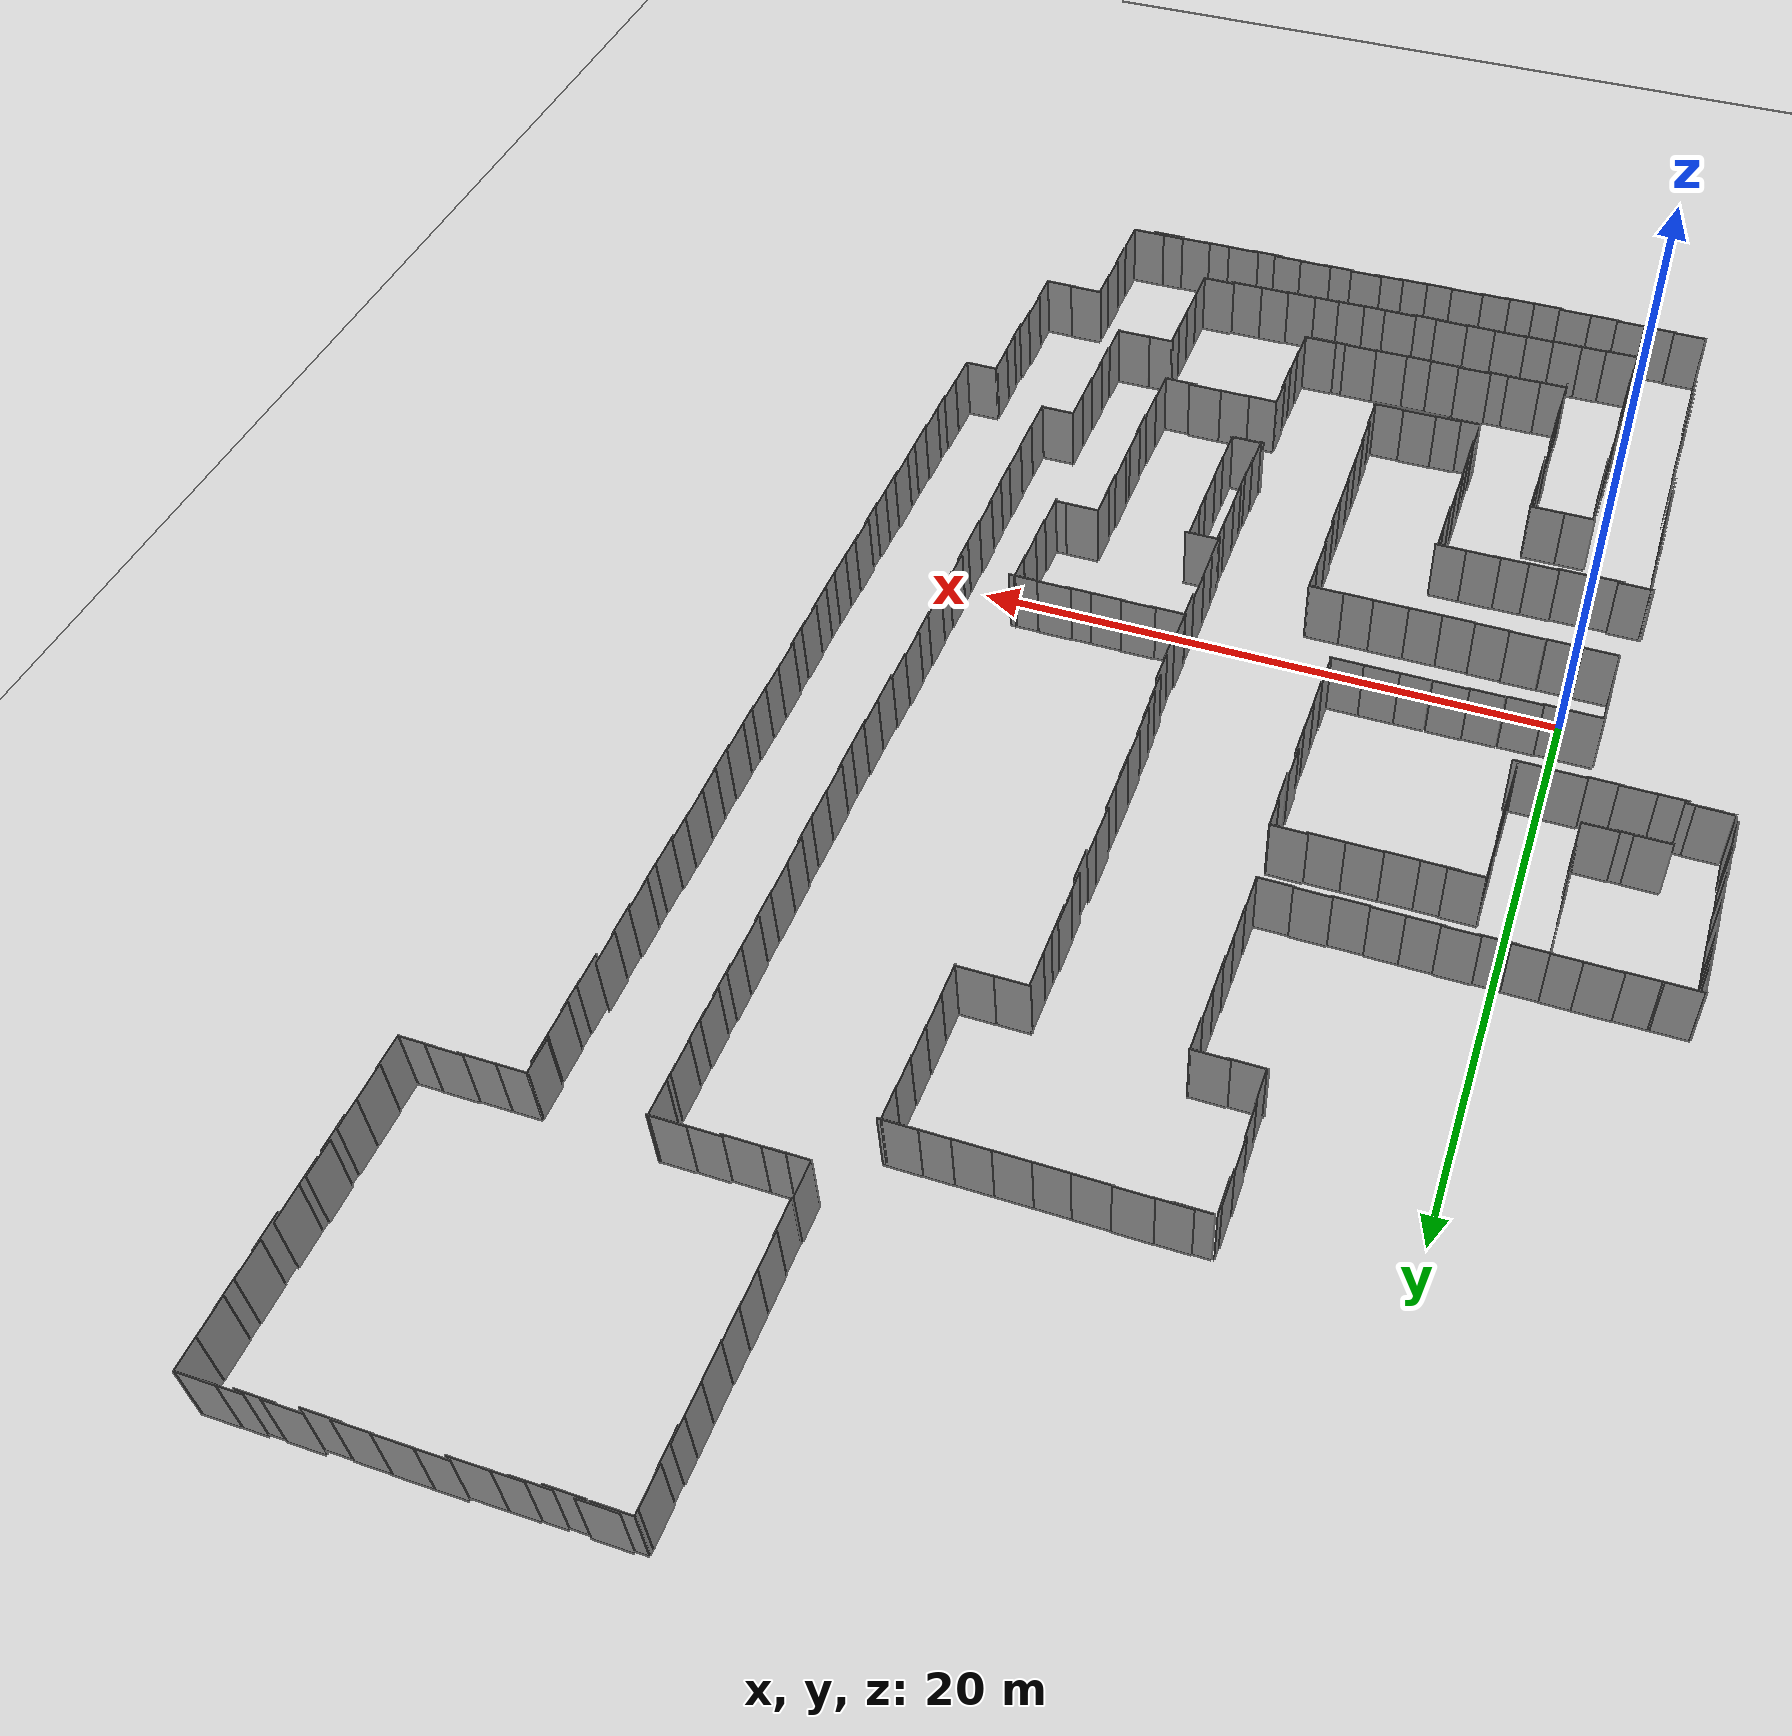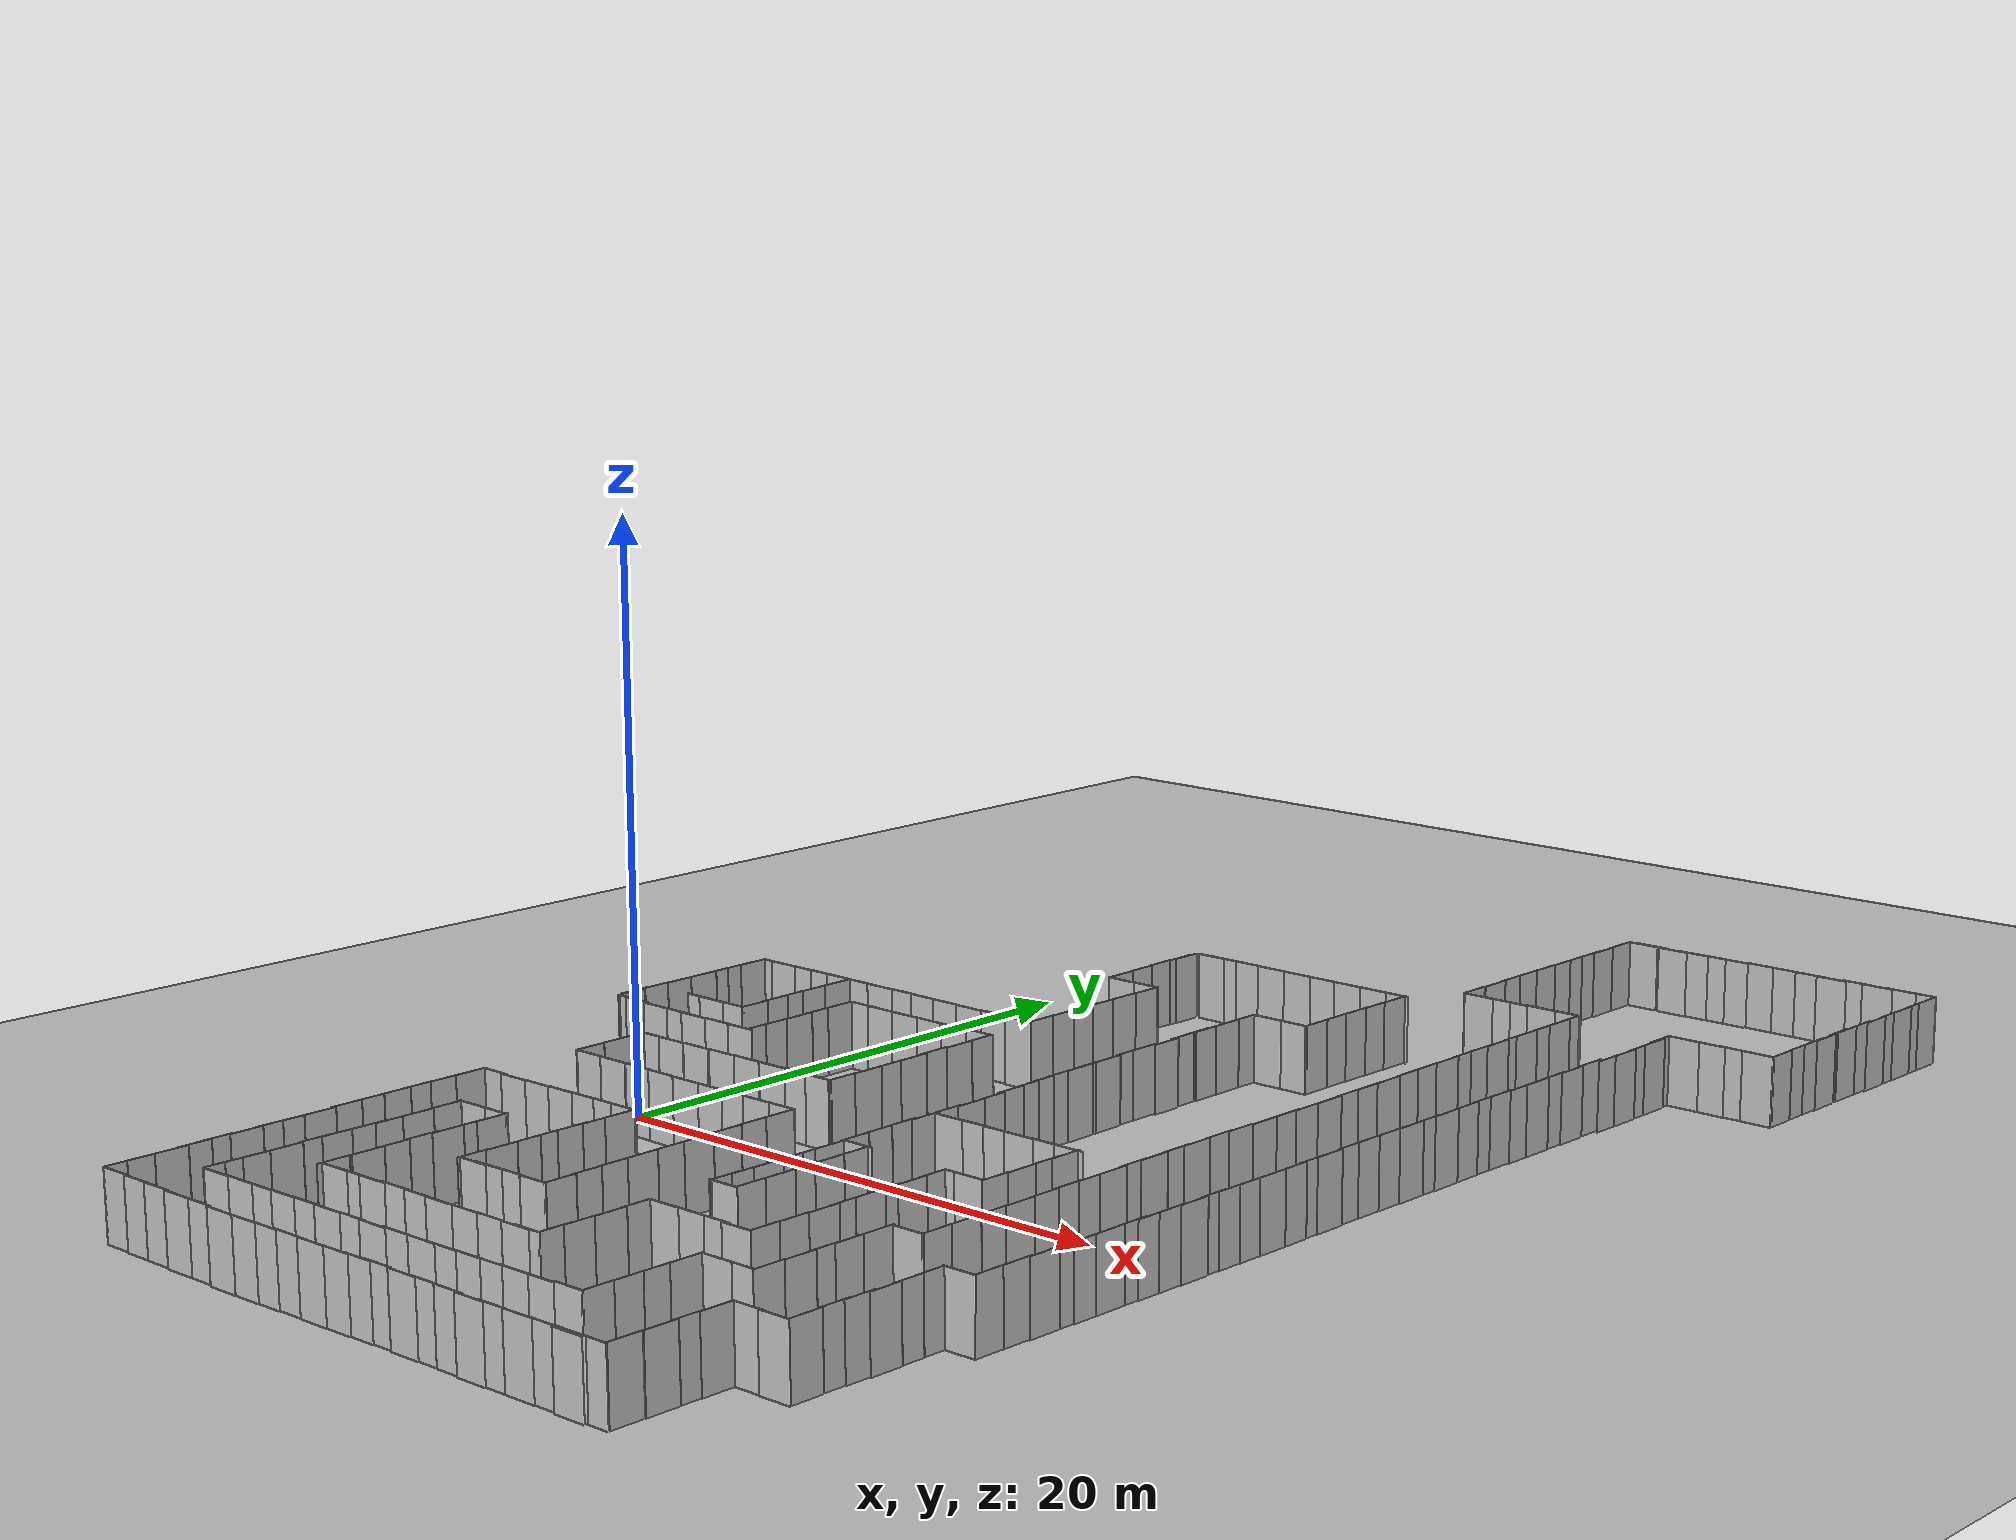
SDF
<sdf version="1.7">
 <world name="default">
  <light name="sun" type="directional">
   <pose>0 0 10 0 -0 0</pose>
   <diffuse>0.8 0.8 0.8 1</diffuse>
   <specular>0.2 0.2 0.2 1</specular>
   <attenuation>
    <range>1000</range>
    <constant>0.9</constant>
    <linear>0.01</linear>
    <quadratic>0.001</quadratic>
   </attenuation>
   <direction>-0.5 0.1 -0.9</direction>
   <spot><inner_angle>0</inner_angle><outer_angle>0</outer_angle><falloff>0</falloff></spot>
  </light>
  <model name="ground_plane">
   <static>1</static>
   <link name="link">
    <collision name="collision">
     <geometry><plane><normal>0 0 1</normal><size>100 100</size></plane></geometry>
     <surface><friction><ode><mu>100</mu><mu2>50</mu2></ode></friction></surface>
    </collision>
    <visual name="visual">
     <cast_shadows>0</cast_shadows>
     <geometry><plane><normal>0 0 1</normal><size>100 100</size></plane></geometry>
     <material>
      <script><uri>file://media/materials/scripts/gazebo.material</uri><name>Gazebo/Grey</name></script>
     </material>
    </visual>
   </link>
  </model>
  <gravity>0 0 -9.8</gravity>
  <magnetic_field>6e-06 2.3e-05 -4.2e-05</magnetic_field>
  <atmosphere type="adiabatic"/>
  <physics type="ode">
   <max_step_size>0.001</max_step_size>
   <real_time_factor>1</real_time_factor>
   <real_time_update_rate>1000</real_time_update_rate>
  </physics>
  <scene><ambient>0.4 0.4 0.4 1</ambient><background>0.7 0.7 0.7 1</background><shadows>1</shadows></scene>
  <audio><device>default</device></audio>
  <spherical_coordinates>
   <surface_model>EARTH_WGS84</surface_model>
   <latitude_deg>0</latitude_deg>
   <longitude_deg>0</longitude_deg>
   <elevation>0</elevation>
   <heading_deg>0</heading_deg>
  </spherical_coordinates>
  <model name="nist_maze_wall_240_clone">
   <static>1</static>
   <link name="nist__maze_wall_240_link">
    <collision name="collision">
     <geometry>
      <mesh><uri>model://nist_maze_wall_240/meshes/nist_maze_wall_240.dae</uri><scale>1 1 1</scale></mesh>
     </geometry>
    </collision>
    <visual name="visual">
     <geometry>
      <mesh><uri>model://nist_maze_wall_240/meshes/nist_maze_wall_240.dae</uri><scale>1 1 1</scale></mesh>
     </geometry>
    </visual>
   </link>
   <pose>0.459411 -2.10367 0 0 -0 0</pose>
  </model>
  <model name="nist_maze_wall_240_clone_0">
   <static>1</static>
   <link name="nist__maze_wall_240_link">
    <collision name="collision">
     <geometry>
      <mesh><uri>model://nist_maze_wall_240/meshes/nist_maze_wall_240.dae</uri><scale>1 1 1</scale></mesh>
     </geometry>
    </collision>
    <visual name="visual">
     <geometry>
      <mesh><uri>model://nist_maze_wall_240/meshes/nist_maze_wall_240.dae</uri><scale>1 1 1</scale></mesh>
     </geometry>
    </visual>
   </link>
   <pose>1.68355 -2.08961 0 0 -0 0</pose>
  </model>
  <model name="nist_maze_wall_240_clone_1">
   <static>1</static>
   <link name="nist__maze_wall_240_link">
    <collision name="collision">
     <geometry>
      <mesh><uri>model://nist_maze_wall_240/meshes/nist_maze_wall_240.dae</uri><scale>1 1 1</scale></mesh>
     </geometry>
    </collision>
    <visual name="visual">
     <geometry>
      <mesh><uri>model://nist_maze_wall_240/meshes/nist_maze_wall_240.dae</uri><scale>1 1 1</scale></mesh>
     </geometry>
    </visual>
   </link>
   <pose>2.82384 -2.11242 0 0 -0 0</pose>
  </model>
  <model name="nist_maze_wall_240_clone_2">
   <static>1</static>
   <link name="nist__maze_wall_240_link">
    <collision name="collision">
     <geometry>
      <mesh><uri>model://nist_maze_wall_240/meshes/nist_maze_wall_240.dae</uri><scale>1 1 1</scale></mesh>
     </geometry>
    </collision>
    <visual name="visual">
     <geometry>
      <mesh><uri>model://nist_maze_wall_240/meshes/nist_maze_wall_240.dae</uri><scale>1 1 1</scale></mesh>
     </geometry>
    </visual>
   </link>
   <pose>4.019 -2.13656 0 0 -0 0</pose>
  </model>
  <model name="nist_maze_wall_240_clone_3">
   <static>1</static>
   <link name="nist__maze_wall_240_link">
    <collision name="collision">
     <geometry>
      <mesh><uri>model://nist_maze_wall_240/meshes/nist_maze_wall_240.dae</uri><scale>1 1 1</scale></mesh>
     </geometry>
    </collision>
    <visual name="visual">
     <geometry>
      <mesh><uri>model://nist_maze_wall_240/meshes/nist_maze_wall_240.dae</uri><scale>1 1 1</scale></mesh>
     </geometry>
    </visual>
   </link>
   <pose>5.11919 -2.13257 0 0 -0 0</pose>
  </model>
  <model name="nist_maze_wall_240_clone_3_clone">
   <static>1</static>
   <link name="nist__maze_wall_240_link">
    <collision name="collision">
     <geometry>
      <mesh><uri>model://nist_maze_wall_240/meshes/nist_maze_wall_240.dae</uri><scale>1 1 1</scale></mesh>
     </geometry>
    </collision>
    <visual name="visual">
     <geometry>
      <mesh><uri>model://nist_maze_wall_240/meshes/nist_maze_wall_240.dae</uri><scale>1 1 1</scale></mesh>
     </geometry>
    </visual>
   </link>
   <pose>4.81247 0.895341 0 0 -0 0</pose>
  </model>
  <model name="nist_maze_wall_240_clone_3_clone_0">
   <static>1</static>
   <link name="nist__maze_wall_240_link">
    <collision name="collision">
     <geometry>
      <mesh><uri>model://nist_maze_wall_240/meshes/nist_maze_wall_240.dae</uri><scale>1 1 1</scale></mesh>
     </geometry>
    </collision>
    <visual name="visual">
     <geometry>
      <mesh><uri>model://nist_maze_wall_240/meshes/nist_maze_wall_240.dae</uri><scale>1 1 1</scale></mesh>
     </geometry>
    </visual>
   </link>
   <pose>3.58214 0.89717 0 0 -0 0</pose>
  </model>
  <model name="nist_maze_wall_240_clone_3_clone_1">
   <static>1</static>
   <link name="nist__maze_wall_240_link">
    <collision name="collision">
     <geometry>
      <mesh><uri>model://nist_maze_wall_240/meshes/nist_maze_wall_240.dae</uri><scale>1 1 1</scale></mesh>
     </geometry>
    </collision>
    <visual name="visual">
     <geometry>
      <mesh><uri>model://nist_maze_wall_240/meshes/nist_maze_wall_240.dae</uri><scale>1 1 1</scale></mesh>
     </geometry>
    </visual>
   </link>
   <pose>2.42888 0.869143 0 0 -0 0</pose>
  </model>
  <model name="nist_maze_wall_240_clone_3_clone_2">
   <static>1</static>
   <link name="nist__maze_wall_240_link">
    <collision name="collision">
     <geometry>
      <mesh><uri>model://nist_maze_wall_240/meshes/nist_maze_wall_240.dae</uri><scale>1 1 1</scale></mesh>
     </geometry>
    </collision>
    <visual name="visual">
     <geometry>
      <mesh><uri>model://nist_maze_wall_240/meshes/nist_maze_wall_240.dae</uri><scale>1 1 1</scale></mesh>
     </geometry>
    </visual>
   </link>
   <pose>1.20189 0.842766 0 0 -0 0</pose>
  </model>
  <model name="nist_maze_wall_240_clone_3_clone_3">
   <static>1</static>
   <link name="nist__maze_wall_240_link">
    <collision name="collision">
     <geometry>
      <mesh><uri>model://nist_maze_wall_240/meshes/nist_maze_wall_240.dae</uri><scale>1 1 1</scale></mesh>
     </geometry>
    </collision>
    <visual name="visual">
     <geometry>
      <mesh><uri>model://nist_maze_wall_240/meshes/nist_maze_wall_240.dae</uri><scale>1 1 1</scale></mesh>
     </geometry>
    </visual>
   </link>
   <pose>0.01872 0.809757 0 0 -0 0</pose>
  </model>
  <model name="nist_maze_wall_240_clone_3_clone_4">
   <static>1</static>
   <link name="nist__maze_wall_240_link">
    <collision name="collision">
     <geometry>
      <mesh><uri>model://nist_maze_wall_240/meshes/nist_maze_wall_240.dae</uri><scale>1 1 1</scale></mesh>
     </geometry>
    </collision>
    <visual name="visual">
     <geometry>
      <mesh><uri>model://nist_maze_wall_240/meshes/nist_maze_wall_240.dae</uri><scale>1 1 1</scale></mesh>
     </geometry>
    </visual>
   </link>
   <pose>-0.726352 -2.09682 0 0 -0 0</pose>
  </model>
  <model name="nist_maze_wall_240_clone_3_clone_5_clone_clone">
   <static>1</static>
   <link name="nist__maze_wall_240_link">
    <collision name="collision">
     <geometry>
      <mesh><uri>model://nist_maze_wall_240/meshes/nist_maze_wall_240.dae</uri><scale>1 1 1</scale></mesh>
     </geometry>
    </collision>
    <visual name="visual">
     <geometry>
      <mesh><uri>model://nist_maze_wall_240/meshes/nist_maze_wall_240.dae</uri><scale>1 1 1</scale></mesh>
     </geometry>
    </visual>
   </link>
   <pose>-0.704858 -0.929022 0 0 -0 1.57</pose>
  </model>
  <model name="nist_maze_wall_240_clone_3_clone_5_clone_clone_0">
   <static>1</static>
   <link name="nist__maze_wall_240_link">
    <collision name="collision">
     <geometry>
      <mesh><uri>model://nist_maze_wall_240/meshes/nist_maze_wall_240.dae</uri><scale>1 1 1</scale></mesh>
     </geometry>
    </collision>
    <visual name="visual">
     <geometry>
      <mesh><uri>model://nist_maze_wall_240/meshes/nist_maze_wall_240.dae</uri><scale>1 1 1</scale></mesh>
     </geometry>
    </visual>
   </link>
   <pose>-0.716954 0.246536 0 0 -0 1.57</pose>
  </model>
  <model name="nist_maze_wall_240_clone_3_clone_5_clone_clone_1">
   <static>1</static>
   <link name="nist__maze_wall_240_link">
    <collision name="collision">
     <geometry>
      <mesh><uri>model://nist_maze_wall_240/meshes/nist_maze_wall_240.dae</uri><scale>1 1 1</scale></mesh>
     </geometry>
    </collision>
    <visual name="visual">
     <geometry>
      <mesh><uri>model://nist_maze_wall_240/meshes/nist_maze_wall_240.dae</uri><scale>1 1 1</scale></mesh>
     </geometry>
    </visual>
   </link>
   <pose>-0.723012 0.833525 0 0 -0 1.57</pose>
  </model>
  <model name="nist_maze_wall_240_clone_3_clone_3_clone">
   <static>1</static>
   <link name="nist__maze_wall_240_link">
    <collision name="collision">
     <geometry>
      <mesh><uri>model://nist_maze_wall_240/meshes/nist_maze_wall_240.dae</uri><scale>1 1 1</scale></mesh>
     </geometry>
    </collision>
    <visual name="visual">
     <geometry>
      <mesh><uri>model://nist_maze_wall_240/meshes/nist_maze_wall_240.dae</uri><scale>1 1 1</scale></mesh>
     </geometry>
    </visual>
   </link>
   <pose>-0.72561 0.815595 0 0 -0 0</pose>
  </model>
  <model name="nist_maze_wall_240_clone_3_clone_5">
   <static>1</static>
   <link name="nist__maze_wall_240_link">
    <collision name="collision">
     <geometry>
      <mesh><uri>model://nist_maze_wall_240/meshes/nist_maze_wall_240.dae</uri><scale>1 1 1</scale></mesh>
     </geometry>
    </collision>
    <visual name="visual">
     <geometry>
      <mesh><uri>model://nist_maze_wall_240/meshes/nist_maze_wall_240.dae</uri><scale>1 1 1</scale></mesh>
     </geometry>
    </visual>
   </link>
   <pose>6.24569 -2.12624 0 0 -0 0</pose>
  </model>
  <model name="nist_maze_wall_240_clone_3_clone_6">
   <static>1</static>
   <link name="nist__maze_wall_240_link">
    <collision name="collision">
     <geometry>
      <mesh><uri>model://nist_maze_wall_240/meshes/nist_maze_wall_240.dae</uri><scale>1 1 1</scale></mesh>
     </geometry>
    </collision>
    <visual name="visual">
     <geometry>
      <mesh><uri>model://nist_maze_wall_240/meshes/nist_maze_wall_240.dae</uri><scale>1 1 1</scale></mesh>
     </geometry>
    </visual>
   </link>
   <pose>7.3074 -2.13235 0 0 -0 0</pose>
  </model>
  <model name="nist_maze_wall_240_clone_3_clone_7">
   <static>1</static>
   <link name="nist__maze_wall_240_link">
    <collision name="collision">
     <geometry>
      <mesh><uri>model://nist_maze_wall_240/meshes/nist_maze_wall_240.dae</uri><scale>1 1 1</scale></mesh>
     </geometry>
    </collision>
    <visual name="visual">
     <geometry>
      <mesh><uri>model://nist_maze_wall_240/meshes/nist_maze_wall_240.dae</uri><scale>1 1 1</scale></mesh>
     </geometry>
    </visual>
   </link>
   <pose>5.85153 0.903553 0 0 -0 0</pose>
  </model>
  <model name="nist_maze_wall_240_clone_3_clone_8">
   <static>1</static>
   <link name="nist__maze_wall_240_link">
    <collision name="collision">
     <geometry>
      <mesh><uri>model://nist_maze_wall_240/meshes/nist_maze_wall_240.dae</uri><scale>1 1 1</scale></mesh>
     </geometry>
    </collision>
    <visual name="visual">
     <geometry>
      <mesh><uri>model://nist_maze_wall_240/meshes/nist_maze_wall_240.dae</uri><scale>1 1 1</scale></mesh>
     </geometry>
    </visual>
   </link>
   <pose>8.46384 -2.12509 0 0 -0 0</pose>
  </model>
  <model name="nist_maze_wall_240_clone_3_clone_9">
   <static>1</static>
   <link name="nist__maze_wall_240_link">
    <collision name="collision">
     <geometry>
      <mesh><uri>model://nist_maze_wall_240/meshes/nist_maze_wall_240.dae</uri><scale>1 1 1</scale></mesh>
     </geometry>
    </collision>
    <visual name="visual">
     <geometry>
      <mesh><uri>model://nist_maze_wall_240/meshes/nist_maze_wall_240.dae</uri><scale>1 1 1</scale></mesh>
     </geometry>
    </visual>
   </link>
   <pose>6.95954 0.902745 0 0 -0 0</pose>
  </model>
  <model name="nist_maze_wall_240_clone_3_clone_5_clone_clone_0_clone">
   <static>1</static>
   <link name="nist__maze_wall_240_link">
    <collision name="collision">
     <geometry>
      <mesh><uri>model://nist_maze_wall_240/meshes/nist_maze_wall_240.dae</uri><scale>1 1 1</scale></mesh>
     </geometry>
    </collision>
    <visual name="visual">
     <geometry>
      <mesh><uri>model://nist_maze_wall_240/meshes/nist_maze_wall_240.dae</uri><scale>1 1 1</scale></mesh>
     </geometry>
    </visual>
   </link>
   <pose>13.1159 -0.314237 0 0 -0 1.57</pose>
  </model>
  <model name="nist_maze_wall_240_clone_3_clone_5_clone_clone_0_clone_0">
   <static>1</static>
   <link name="nist__maze_wall_240_link">
    <collision name="collision">
     <geometry>
      <mesh><uri>model://nist_maze_wall_240/meshes/nist_maze_wall_240.dae</uri><scale>1 1 1</scale></mesh>
     </geometry>
    </collision>
    <visual name="visual">
     <geometry>
      <mesh><uri>model://nist_maze_wall_240/meshes/nist_maze_wall_240.dae</uri><scale>1 1 1</scale></mesh>
     </geometry>
    </visual>
   </link>
   <pose>13.1914 0.653304 0 0 -0 1.57</pose>
  </model>
  <model name="nist_maze_wall_240_clone_3_clone_5_clone_clone_0_clone_1">
   <static>1</static>
   <link name="nist__maze_wall_240_link">
    <collision name="collision">
     <geometry>
      <mesh><uri>model://nist_maze_wall_240/meshes/nist_maze_wall_240.dae</uri><scale>1 1 1</scale></mesh>
     </geometry>
    </collision>
    <visual name="visual">
     <geometry>
      <mesh><uri>model://nist_maze_wall_240/meshes/nist_maze_wall_240.dae</uri><scale>1 1 1</scale></mesh>
     </geometry>
    </visual>
   </link>
   <pose>13.1294 -1.32193 0 0 -0 1.57</pose>
  </model>
  <model name="nist_maze_wall_240_clone_3_clone_5_clone_clone_0_clone_2">
   <static>1</static>
   <link name="nist__maze_wall_240_link">
    <collision name="collision">
     <geometry>
      <mesh><uri>model://nist_maze_wall_240/meshes/nist_maze_wall_240.dae</uri><scale>1 1 1</scale></mesh>
     </geometry>
    </collision>
    <visual name="visual">
     <geometry>
      <mesh><uri>model://nist_maze_wall_240/meshes/nist_maze_wall_240.dae</uri><scale>1 1 1</scale></mesh>
     </geometry>
    </visual>
   </link>
   <pose>13.169 1.7119 0 0 -0 1.57</pose>
  </model>
  <model name="nist_maze_wall_240_clone_3_clone_5_clone_clone_0_clone_3">
   <static>1</static>
   <link name="nist__maze_wall_240_link">
    <collision name="collision">
     <geometry>
      <mesh><uri>model://nist_maze_wall_240/meshes/nist_maze_wall_240.dae</uri><scale>1 1 1</scale></mesh>
     </geometry>
    </collision>
    <visual name="visual">
     <geometry>
      <mesh><uri>model://nist_maze_wall_240/meshes/nist_maze_wall_240.dae</uri><scale>1 1 1</scale></mesh>
     </geometry>
    </visual>
   </link>
   <pose>13.2334 2.66225 0 0 -0 1.57</pose>
  </model>
  <model name="nist_maze_wall_240_clone_3_clone_5_clone_clone_0_clone_4">
   <static>1</static>
   <link name="nist__maze_wall_240_link">
    <collision name="collision">
     <geometry>
      <mesh><uri>model://nist_maze_wall_240/meshes/nist_maze_wall_240.dae</uri><scale>1 1 1</scale></mesh>
     </geometry>
    </collision>
    <visual name="visual">
     <geometry>
      <mesh><uri>model://nist_maze_wall_240/meshes/nist_maze_wall_240.dae</uri><scale>1 1 1</scale></mesh>
     </geometry>
    </visual>
   </link>
   <pose>13.2046 3.61599 0 0 -0 1.57</pose>
  </model>
  <model name="nist_maze_wall_240_clone_3_clone_5_clone_clone_0_clone_5">
   <static>1</static>
   <link name="nist__maze_wall_240_link">
    <collision name="collision">
     <geometry>
      <mesh><uri>model://nist_maze_wall_240/meshes/nist_maze_wall_240.dae</uri><scale>1 1 1</scale></mesh>
     </geometry>
    </collision>
    <visual name="visual">
     <geometry>
      <mesh><uri>model://nist_maze_wall_240/meshes/nist_maze_wall_240.dae</uri><scale>1 1 1</scale></mesh>
     </geometry>
    </visual>
   </link>
   <pose>13.1179 4.56936 0 0 -0 1.57</pose>
  </model>
  <model name="nist_maze_wall_240_clone_3_clone_5_clone_clone_0_clone_6">
   <static>1</static>
   <link name="nist__maze_wall_240_link">
    <collision name="collision">
     <geometry>
      <mesh><uri>model://nist_maze_wall_240/meshes/nist_maze_wall_240.dae</uri><scale>1 1 1</scale></mesh>
     </geometry>
    </collision>
    <visual name="visual">
     <geometry>
      <mesh><uri>model://nist_maze_wall_240/meshes/nist_maze_wall_240.dae</uri><scale>1 1 1</scale></mesh>
     </geometry>
    </visual>
   </link>
   <pose>13.0912 5.31717 0 0 -0 1.57</pose>
  </model>
  <model name="nist_maze_wall_240_clone_3_clone_5_clone_clone_0_clone_7">
   <static>1</static>
   <link name="nist__maze_wall_240_link">
    <collision name="collision">
     <geometry>
      <mesh><uri>model://nist_maze_wall_240/meshes/nist_maze_wall_240.dae</uri><scale>1 1 1</scale></mesh>
     </geometry>
    </collision>
    <visual name="visual">
     <geometry>
      <mesh><uri>model://nist_maze_wall_240/meshes/nist_maze_wall_240.dae</uri><scale>1 1 1</scale></mesh>
     </geometry>
    </visual>
   </link>
   <pose>13.0578 6.05257 0 0 -0 1.57</pose>
  </model>
  <model name="nist_maze_wall_240_clone_3_clone_5_clone_clone_0_clone_8">
   <static>1</static>
   <link name="nist__maze_wall_240_link">
    <collision name="collision">
     <geometry>
      <mesh><uri>model://nist_maze_wall_240/meshes/nist_maze_wall_240.dae</uri><scale>1 1 1</scale></mesh>
     </geometry>
    </collision>
    <visual name="visual">
     <geometry>
      <mesh><uri>model://nist_maze_wall_240/meshes/nist_maze_wall_240.dae</uri><scale>1 1 1</scale></mesh>
     </geometry>
    </visual>
   </link>
   <pose>13.0235 7.06227 0 0 -0 1.57</pose>
  </model>
  <model name="nist_maze_wall_240_clone_3_clone_5_clone_clone_0_clone_9">
   <static>1</static>
   <link name="nist__maze_wall_240_link">
    <collision name="collision">
     <geometry>
      <mesh><uri>model://nist_maze_wall_240/meshes/nist_maze_wall_240.dae</uri><scale>1 1 1</scale></mesh>
     </geometry>
    </collision>
    <visual name="visual">
     <geometry>
      <mesh><uri>model://nist_maze_wall_240/meshes/nist_maze_wall_240.dae</uri><scale>1 1 1</scale></mesh>
     </geometry>
    </visual>
   </link>
   <pose>13.0135 8.31158 0 0 -0 1.57</pose>
  </model>
  <model name="nist_maze_wall_240_clone_3_clone_5_clone_clone_0_clone_10">
   <static>1</static>
   <link name="nist__maze_wall_240_link">
    <collision name="collision">
     <geometry>
      <mesh><uri>model://nist_maze_wall_240/meshes/nist_maze_wall_240.dae</uri><scale>1 1 1</scale></mesh>
     </geometry>
    </collision>
    <visual name="visual">
     <geometry>
      <mesh><uri>model://nist_maze_wall_240/meshes/nist_maze_wall_240.dae</uri><scale>1 1 1</scale></mesh>
     </geometry>
    </visual>
   </link>
   <pose>13.0231 9.31966 0 0 -0 1.57</pose>
  </model>
  <model name="nist_maze_wall_240_clone_3_clone_5_clone_clone_0_clone_11">
   <static>1</static>
   <link name="nist__maze_wall_240_link">
    <collision name="collision">
     <geometry>
      <mesh><uri>model://nist_maze_wall_240/meshes/nist_maze_wall_240.dae</uri><scale>1 1 1</scale></mesh>
     </geometry>
    </collision>
    <visual name="visual">
     <geometry>
      <mesh><uri>model://nist_maze_wall_240/meshes/nist_maze_wall_240.dae</uri><scale>1 1 1</scale></mesh>
     </geometry>
    </visual>
   </link>
   <pose>13.043 7.93222 0 0 -0 1.57</pose>
  </model>
  <model name="nist_maze_wall_240_clone_3_clone_5_clone_clone_0_clone_12">
   <static>1</static>
   <link name="nist__maze_wall_240_link">
    <collision name="collision">
     <geometry>
      <mesh><uri>model://nist_maze_wall_240/meshes/nist_maze_wall_240.dae</uri><scale>1 1 1</scale></mesh>
     </geometry>
    </collision>
    <visual name="visual">
     <geometry>
      <mesh><uri>model://nist_maze_wall_240/meshes/nist_maze_wall_240.dae</uri><scale>1 1 1</scale></mesh>
     </geometry>
    </visual>
   </link>
   <pose>9.64027 -2.10411 0 0 -0 1.57</pose>
  </model>
  <model name="nist_maze_wall_240_clone_3_clone_5_clone_clone_0_clone_13">
   <static>1</static>
   <link name="nist__maze_wall_240_link">
    <collision name="collision">
     <geometry>
      <mesh><uri>model://nist_maze_wall_240/meshes/nist_maze_wall_240.dae</uri><scale>1 1 1</scale></mesh>
     </geometry>
    </collision>
    <visual name="visual">
     <geometry>
      <mesh><uri>model://nist_maze_wall_240/meshes/nist_maze_wall_240.dae</uri><scale>1 1 1</scale></mesh>
     </geometry>
    </visual>
   </link>
   <pose>9.63345 -3.20414 0 0 -0 1.57</pose>
  </model>
  <model name="nist_maze_wall_240_clone_3_clone_5_clone_clone_0_clone_14">
   <static>1</static>
   <link name="nist__maze_wall_240_link">
    <collision name="collision">
     <geometry>
      <mesh><uri>model://nist_maze_wall_240/meshes/nist_maze_wall_240.dae</uri><scale>1 1 1</scale></mesh>
     </geometry>
    </collision>
    <visual name="visual">
     <geometry>
      <mesh><uri>model://nist_maze_wall_240/meshes/nist_maze_wall_240.dae</uri><scale>1 1 1</scale></mesh>
     </geometry>
    </visual>
   </link>
   <pose>9.65675 -4.34652 0 0 -0 1.57</pose>
  </model>
  <model name="nist_maze_wall_240_clone_3_clone_5_clone_clone_0_clone_15">
   <static>1</static>
   <link name="nist__maze_wall_240_link">
    <collision name="collision">
     <geometry>
      <mesh><uri>model://nist_maze_wall_240/meshes/nist_maze_wall_240.dae</uri><scale>1 1 1</scale></mesh>
     </geometry>
    </collision>
    <visual name="visual">
     <geometry>
      <mesh><uri>model://nist_maze_wall_240/meshes/nist_maze_wall_240.dae</uri><scale>1 1 1</scale></mesh>
     </geometry>
    </visual>
   </link>
   <pose>8.11899 2.01684 0 0 -0 1.57</pose>
  </model>
  <model name="nist_maze_wall_240_clone_3_clone_5_clone_clone_0_clone_16">
   <static>1</static>
   <link name="nist__maze_wall_240_link">
    <collision name="collision">
     <geometry>
      <mesh><uri>model://nist_maze_wall_240/meshes/nist_maze_wall_240.dae</uri><scale>1 1 1</scale></mesh>
     </geometry>
    </collision>
    <visual name="visual">
     <geometry>
      <mesh><uri>model://nist_maze_wall_240/meshes/nist_maze_wall_240.dae</uri><scale>1 1 1</scale></mesh>
     </geometry>
    </visual>
   </link>
   <pose>8.15345 3.17075 0 0 -0 1.57</pose>
  </model>
  <model name="nist_maze_wall_240_clone_3_clone_5_clone_clone_0_clone_17">
   <static>1</static>
   <link name="nist__maze_wall_240_link">
    <collision name="collision">
     <geometry>
      <mesh><uri>model://nist_maze_wall_240/meshes/nist_maze_wall_240.dae</uri><scale>1 1 1</scale></mesh>
     </geometry>
    </collision>
    <visual name="visual">
     <geometry>
      <mesh><uri>model://nist_maze_wall_240/meshes/nist_maze_wall_240.dae</uri><scale>1 1 1</scale></mesh>
     </geometry>
    </visual>
   </link>
   <pose>8.14947 4.19664 0 0 -0 1.57</pose>
  </model>
  <model name="nist_maze_wall_240_clone_3_clone_5_clone_clone_0_clone_18">
   <static>1</static>
   <link name="nist__maze_wall_240_link">
    <collision name="collision">
     <geometry>
      <mesh><uri>model://nist_maze_wall_240/meshes/nist_maze_wall_240.dae</uri><scale>1 1 1</scale></mesh>
     </geometry>
    </collision>
    <visual name="visual">
     <geometry>
      <mesh><uri>model://nist_maze_wall_240/meshes/nist_maze_wall_240.dae</uri><scale>1 1 1</scale></mesh>
     </geometry>
    </visual>
   </link>
   <pose>8.16392 5.24779 0 0 -0 1.57</pose>
  </model>
  <model name="nist_maze_wall_240_clone_3_clone_5_clone_clone_0_clone_19">
   <static>1</static>
   <link name="nist__maze_wall_240_link">
    <collision name="collision">
     <geometry>
      <mesh><uri>model://nist_maze_wall_240/meshes/nist_maze_wall_240.dae</uri><scale>1 1 1</scale></mesh>
     </geometry>
    </collision>
    <visual name="visual">
     <geometry>
      <mesh><uri>model://nist_maze_wall_240/meshes/nist_maze_wall_240.dae</uri><scale>1 1 1</scale></mesh>
     </geometry>
    </visual>
   </link>
   <pose>8.10571 6.25056 0 0 -0 1.57</pose>
  </model>
  <model name="nist_maze_wall_240_clone_3_clone_5_clone_clone_0_clone_20">
   <static>1</static>
   <link name="nist__maze_wall_240_link">
    <collision name="collision">
     <geometry>
      <mesh><uri>model://nist_maze_wall_240/meshes/nist_maze_wall_240.dae</uri><scale>1 1 1</scale></mesh>
     </geometry>
    </collision>
    <visual name="visual">
     <geometry>
      <mesh><uri>model://nist_maze_wall_240/meshes/nist_maze_wall_240.dae</uri><scale>1 1 1</scale></mesh>
     </geometry>
    </visual>
   </link>
   <pose>8.17578 7.37784 0 0 -0 1.57</pose>
  </model>
  <model name="nist_maze_wall_240_clone_3_clone_5_clone_clone_0_clone_21">
   <static>1</static>
   <link name="nist__maze_wall_240_link">
    <collision name="collision">
     <geometry>
      <mesh><uri>model://nist_maze_wall_240/meshes/nist_maze_wall_240.dae</uri><scale>1 1 1</scale></mesh>
     </geometry>
    </collision>
    <visual name="visual">
     <geometry>
      <mesh><uri>model://nist_maze_wall_240/meshes/nist_maze_wall_240.dae</uri><scale>1 1 1</scale></mesh>
     </geometry>
    </visual>
   </link>
   <pose>8.15854 8.40829 0 0 -0 1.57</pose>
  </model>
  <model name="nist_maze_wall_240_clone_3_clone_5_clone_clone_0_clone_22">
   <static>1</static>
   <link name="nist__maze_wall_240_link">
    <collision name="collision">
     <geometry>
      <mesh><uri>model://nist_maze_wall_240/meshes/nist_maze_wall_240.dae</uri><scale>1 1 1</scale></mesh>
     </geometry>
    </collision>
    <visual name="visual">
     <geometry>
      <mesh><uri>model://nist_maze_wall_240/meshes/nist_maze_wall_240.dae</uri><scale>1 1 1</scale></mesh>
     </geometry>
    </visual>
   </link>
   <pose>7.9823 11.5903 0 0 -0 1.57</pose>
  </model>
  <model name="nist_maze_wall_240_clone_3_clone_5_clone_clone_0_clone_23">
   <static>1</static>
   <link name="nist__maze_wall_240_link">
    <collision name="collision">
     <geometry>
      <mesh><uri>model://nist_maze_wall_240/meshes/nist_maze_wall_240.dae</uri><scale>1 1 1</scale></mesh>
     </geometry>
    </collision>
    <visual name="visual">
     <geometry>
      <mesh><uri>model://nist_maze_wall_240/meshes/nist_maze_wall_240.dae</uri><scale>1 1 1</scale></mesh>
     </geometry>
    </visual>
   </link>
   <pose>8.00611 12.7339 0 0 -0 1.57</pose>
  </model>
  <model name="nist_maze_wall_240_clone_3_clone_5_clone_clone_0_clone_24">
   <static>1</static>
   <link name="nist__maze_wall_240_link">
    <collision name="collision">
     <geometry>
      <mesh><uri>model://nist_maze_wall_240/meshes/nist_maze_wall_240.dae</uri><scale>1 1 1</scale></mesh>
     </geometry>
    </collision>
    <visual name="visual">
     <geometry>
      <mesh><uri>model://nist_maze_wall_240/meshes/nist_maze_wall_240.dae</uri><scale>1 1 1</scale></mesh>
     </geometry>
    </visual>
   </link>
   <pose>8.01532 13.802 0 0 -0 1.57</pose>
  </model>
  <model name="nist_maze_wall_240_clone_3_clone_5_clone_clone_0_clone_25">
   <static>1</static>
   <link name="nist__maze_wall_240_link">
    <collision name="collision">
     <geometry>
      <mesh><uri>model://nist_maze_wall_240/meshes/nist_maze_wall_240.dae</uri><scale>1 1 1</scale></mesh>
     </geometry>
    </collision>
    <visual name="visual">
     <geometry>
      <mesh><uri>model://nist_maze_wall_240/meshes/nist_maze_wall_240.dae</uri><scale>1 1 1</scale></mesh>
     </geometry>
    </visual>
   </link>
   <pose>8.05576 14.6906 0 0 -0 1.57</pose>
  </model>
  <model name="nist_maze_wall_240_clone_3_clone_5_clone_clone_0_clone_10_clone">
   <static>1</static>
   <link name="nist__maze_wall_240_link">
    <collision name="collision">
     <geometry>
      <mesh><uri>model://nist_maze_wall_240/meshes/nist_maze_wall_240.dae</uri><scale>1 1 1</scale></mesh>
     </geometry>
    </collision>
    <visual name="visual">
     <geometry>
      <mesh><uri>model://nist_maze_wall_240/meshes/nist_maze_wall_240.dae</uri><scale>1 1 1</scale></mesh>
     </geometry>
    </visual>
   </link>
   <pose>12.9655 10.4197 0 0 -0 1.57</pose>
  </model>
  <model name="nist_maze_wall_240_clone_3_clone_5_clone_clone_0_clone_10_clone_0">
   <static>1</static>
   <link name="nist__maze_wall_240_link">
    <collision name="collision">
     <geometry>
      <mesh><uri>model://nist_maze_wall_240/meshes/nist_maze_wall_240.dae</uri><scale>1 1 1</scale></mesh>
     </geometry>
    </collision>
    <visual name="visual">
     <geometry>
      <mesh><uri>model://nist_maze_wall_240/meshes/nist_maze_wall_240.dae</uri><scale>1 1 1</scale></mesh>
     </geometry>
    </visual>
   </link>
   <pose>12.9747 11.2138 0 0 -0 1.57</pose>
  </model>
  <model name="nist_maze_wall_240_clone_3_clone_5_clone_clone_0_clone_10_clone_1">
   <static>1</static>
   <link name="nist__maze_wall_240_link">
    <collision name="collision">
     <geometry>
      <mesh><uri>model://nist_maze_wall_240/meshes/nist_maze_wall_240.dae</uri><scale>1 1 1</scale></mesh>
     </geometry>
    </collision>
    <visual name="visual">
     <geometry>
      <mesh><uri>model://nist_maze_wall_240/meshes/nist_maze_wall_240.dae</uri><scale>1 1 1</scale></mesh>
     </geometry>
    </visual>
   </link>
   <pose>13.0681 12.1827 0 0 -0 1.57</pose>
  </model>
  <model name="nist_maze_wall_240_clone_3_clone_5_clone_clone_0_clone_10_clone_1_clone">
   <static>1</static>
   <link name="nist__maze_wall_240_link">
    <collision name="collision">
     <geometry>
      <mesh><uri>model://nist_maze_wall_240/meshes/nist_maze_wall_240.dae</uri><scale>1 1 1</scale></mesh>
     </geometry>
    </collision>
    <visual name="visual">
     <geometry>
      <mesh><uri>model://nist_maze_wall_240/meshes/nist_maze_wall_240.dae</uri><scale>1 1 1</scale></mesh>
     </geometry>
    </visual>
   </link>
   <pose>12.9909 13.0737 0 0 -0 1.57</pose>
  </model>
  <model name="nist_maze_wall_240_clone_3_clone_5_clone_clone_0_clone_10_clone_1_clone_0">
   <static>1</static>
   <link name="nist__maze_wall_240_link">
    <collision name="collision">
     <geometry>
      <mesh><uri>model://nist_maze_wall_240/meshes/nist_maze_wall_240.dae</uri><scale>1 1 1</scale></mesh>
     </geometry>
    </collision>
    <visual name="visual">
     <geometry>
      <mesh><uri>model://nist_maze_wall_240/meshes/nist_maze_wall_240.dae</uri><scale>1 1 1</scale></mesh>
     </geometry>
    </visual>
   </link>
   <pose>13.0183 14.3449 0 0 -0 1.57</pose>
  </model>
  <model name="nist_maze_wall_240_clone_3_clone_5_clone_clone_0_clone_10_clone_1_clone_1">
   <static>1</static>
   <link name="nist__maze_wall_240_link">
    <collision name="collision">
     <geometry>
      <mesh><uri>model://nist_maze_wall_240/meshes/nist_maze_wall_240.dae</uri><scale>1 1 1</scale></mesh>
     </geometry>
    </collision>
    <visual name="visual">
     <geometry>
      <mesh><uri>model://nist_maze_wall_240/meshes/nist_maze_wall_240.dae</uri><scale>1 1 1</scale></mesh>
     </geometry>
    </visual>
   </link>
   <pose>12.9757 13.863 0 0 -0 1.57</pose>
  </model>
  <model name="nist_maze_wall_240_clone_3_clone_5_clone_clone_0_clone_10_clone_1_clone_2">
   <static>1</static>
   <link name="nist__maze_wall_240_link">
    <collision name="collision">
     <geometry>
      <mesh><uri>model://nist_maze_wall_240/meshes/nist_maze_wall_240.dae</uri><scale>1 1 1</scale></mesh>
     </geometry>
    </collision>
    <visual name="visual">
     <geometry>
      <mesh><uri>model://nist_maze_wall_240/meshes/nist_maze_wall_240.dae</uri><scale>1 1 1</scale></mesh>
     </geometry>
    </visual>
   </link>
   <pose>13.0242 15.381 0 0 -0 1.57</pose>
  </model>
  <model name="nist_maze_wall_240_clone_3_clone_5_clone_clone_0_clone_10_clone_1_clone_3">
   <static>1</static>
   <link name="nist__maze_wall_240_link">
    <collision name="collision">
     <geometry>
      <mesh><uri>model://nist_maze_wall_240/meshes/nist_maze_wall_240.dae</uri><scale>1 1 1</scale></mesh>
     </geometry>
    </collision>
    <visual name="visual">
     <geometry>
      <mesh><uri>model://nist_maze_wall_240/meshes/nist_maze_wall_240.dae</uri><scale>1 1 1</scale></mesh>
     </geometry>
    </visual>
   </link>
   <pose>13.0221 16.2181 0 0 -0 1.57</pose>
  </model>
  <model name="nist_maze_wall_240_clone_3_clone_9_clone">
   <static>1</static>
   <link name="nist__maze_wall_240_link">
    <collision name="collision">
     <geometry>
      <mesh><uri>model://nist_maze_wall_240/meshes/nist_maze_wall_240.dae</uri><scale>1 1 1</scale></mesh>
     </geometry>
    </collision>
    <visual name="visual">
     <geometry>
      <mesh><uri>model://nist_maze_wall_240/meshes/nist_maze_wall_240.dae</uri><scale>1 1 1</scale></mesh>
     </geometry>
    </visual>
   </link>
   <pose>12.9859 16.2127 0 0 -0 0</pose>
  </model>
  <model name="nist_maze_wall_240_clone_3_clone_9_clone_0">
   <static>1</static>
   <link name="nist__maze_wall_240_link">
    <collision name="collision">
     <geometry>
      <mesh><uri>model://nist_maze_wall_240/meshes/nist_maze_wall_240.dae</uri><scale>1 1 1</scale></mesh>
     </geometry>
    </collision>
    <visual name="visual">
     <geometry>
      <mesh><uri>model://nist_maze_wall_240/meshes/nist_maze_wall_240.dae</uri><scale>1 1 1</scale></mesh>
     </geometry>
    </visual>
   </link>
   <pose>14.104 16.2179 0 0 -0 0</pose>
  </model>
  <model name="nist_maze_wall_240_clone_3_clone_5_clone_clone_0_clone_10_clone_1_clone_2_clone">
   <static>1</static>
   <link name="nist__maze_wall_240_link">
    <collision name="collision">
     <geometry>
      <mesh><uri>model://nist_maze_wall_240/meshes/nist_maze_wall_240.dae</uri><scale>1 1 1</scale></mesh>
     </geometry>
    </collision>
    <visual name="visual">
     <geometry>
      <mesh><uri>model://nist_maze_wall_240/meshes/nist_maze_wall_240.dae</uri><scale>1 1 1</scale></mesh>
     </geometry>
    </visual>
   </link>
   <pose>15.277 17.3614 0 0 -0 1.57</pose>
  </model>
  <model name="nist_maze_wall_240_clone_3_clone_5_clone_clone_0_clone_10_clone_1_clone_2_clone_0">
   <static>1</static>
   <link name="nist__maze_wall_240_link">
    <collision name="collision">
     <geometry>
      <mesh><uri>model://nist_maze_wall_240/meshes/nist_maze_wall_240.dae</uri><scale>1 1 1</scale></mesh>
     </geometry>
    </collision>
    <visual name="visual">
     <geometry>
      <mesh><uri>model://nist_maze_wall_240/meshes/nist_maze_wall_240.dae</uri><scale>1 1 1</scale></mesh>
     </geometry>
    </visual>
   </link>
   <pose>15.2725 18.4689 0 0 -0 1.57</pose>
  </model>
  <model name="nist_maze_wall_240_clone_3_clone_5_clone_clone_0_clone_10_clone_1_clone_2_clone_1">
   <static>1</static>
   <link name="nist__maze_wall_240_link">
    <collision name="collision">
     <geometry>
      <mesh><uri>model://nist_maze_wall_240/meshes/nist_maze_wall_240.dae</uri><scale>1 1 1</scale></mesh>
     </geometry>
    </collision>
    <visual name="visual">
     <geometry>
      <mesh><uri>model://nist_maze_wall_240/meshes/nist_maze_wall_240.dae</uri><scale>1 1 1</scale></mesh>
     </geometry>
    </visual>
   </link>
   <pose>15.2926 19.5737 0 0 -0 1.57</pose>
  </model>
  <model name="nist_maze_wall_240_clone_3_clone_5_clone_clone_0_clone_10_clone_1_clone_2_clone_2">
   <static>1</static>
   <link name="nist__maze_wall_240_link">
    <collision name="collision">
     <geometry>
      <mesh><uri>model://nist_maze_wall_240/meshes/nist_maze_wall_240.dae</uri><scale>1 1 1</scale></mesh>
     </geometry>
    </collision>
    <visual name="visual">
     <geometry>
      <mesh><uri>model://nist_maze_wall_240/meshes/nist_maze_wall_240.dae</uri><scale>1 1 1</scale></mesh>
     </geometry>
    </visual>
   </link>
   <pose>15.3177 20.6411 0 0 -0 1.57</pose>
  </model>
  <model name="nist_maze_wall_240_clone_3_clone_5_clone_clone_0_clone_10_clone_1_clone_2_clone_3">
   <static>1</static>
   <link name="nist__maze_wall_240_link">
    <collision name="collision">
     <geometry>
      <mesh><uri>model://nist_maze_wall_240/meshes/nist_maze_wall_240.dae</uri><scale>1 1 1</scale></mesh>
     </geometry>
    </collision>
    <visual name="visual">
     <geometry>
      <mesh><uri>model://nist_maze_wall_240/meshes/nist_maze_wall_240.dae</uri><scale>1 1 1</scale></mesh>
     </geometry>
    </visual>
   </link>
   <pose>15.3419 21.6525 0 0 -0 1.57</pose>
  </model>
  <model name="nist_maze_wall_240_clone_3_clone_5_clone_clone_0_clone_10_clone_1_clone_2_clone_4">
   <static>1</static>
   <link name="nist__maze_wall_240_link">
    <collision name="collision">
     <geometry>
      <mesh><uri>model://nist_maze_wall_240/meshes/nist_maze_wall_240.dae</uri><scale>1 1 1</scale></mesh>
     </geometry>
    </collision>
    <visual name="visual">
     <geometry>
      <mesh><uri>model://nist_maze_wall_240/meshes/nist_maze_wall_240.dae</uri><scale>1 1 1</scale></mesh>
     </geometry>
    </visual>
   </link>
   <pose>8.06248 15.749 0 0 -0 1.57</pose>
  </model>
  <model name="nist_maze_wall_240_clone_3_clone_5_clone_clone_0_clone_10_clone_1_clone_2_clone_5">
   <static>1</static>
   <link name="nist__maze_wall_240_link">
    <collision name="collision">
     <geometry>
      <mesh><uri>model://nist_maze_wall_240/meshes/nist_maze_wall_240.dae</uri><scale>1 1 1</scale></mesh>
     </geometry>
    </collision>
    <visual name="visual">
     <geometry>
      <mesh><uri>model://nist_maze_wall_240/meshes/nist_maze_wall_240.dae</uri><scale>1 1 1</scale></mesh>
     </geometry>
    </visual>
   </link>
   <pose>8.1008 16.8872 0 0 -0 1.57</pose>
  </model>
  <model name="nist_maze_wall_240_clone_3_clone_9_clone_clone">
   <static>1</static>
   <link name="nist__maze_wall_240_link">
    <collision name="collision">
     <geometry>
      <mesh><uri>model://nist_maze_wall_240/meshes/nist_maze_wall_240.dae</uri><scale>1 1 1</scale></mesh>
     </geometry>
    </collision>
    <visual name="visual">
     <geometry>
      <mesh><uri>model://nist_maze_wall_240/meshes/nist_maze_wall_240.dae</uri><scale>1 1 1</scale></mesh>
     </geometry>
    </visual>
   </link>
   <pose>6.93079 16.8427 0 0 -0 0</pose>
  </model>
  <model name="nist_maze_wall_240_clone_3_clone_9_clone_clone_0">
   <static>1</static>
   <link name="nist__maze_wall_240_link">
    <collision name="collision">
     <geometry>
      <mesh><uri>model://nist_maze_wall_240/meshes/nist_maze_wall_240.dae</uri><scale>1 1 1</scale></mesh>
     </geometry>
    </collision>
    <visual name="visual">
     <geometry>
      <mesh><uri>model://nist_maze_wall_240/meshes/nist_maze_wall_240.dae</uri><scale>1 1 1</scale></mesh>
     </geometry>
    </visual>
   </link>
   <pose>5.85112 16.8134 0 0 -0 0</pose>
  </model>
  <model name="nist_maze_wall_240_clone_3_clone_5_clone_clone_0_clone_10_clone_1_clone_2_clone_1_clone">
   <static>1</static>
   <link name="nist__maze_wall_240_link">
    <collision name="collision">
     <geometry>
      <mesh><uri>model://nist_maze_wall_240/meshes/nist_maze_wall_240.dae</uri><scale>1 1 1</scale></mesh>
     </geometry>
    </collision>
    <visual name="visual">
     <geometry>
      <mesh><uri>model://nist_maze_wall_240/meshes/nist_maze_wall_240.dae</uri><scale>1 1 1</scale></mesh>
     </geometry>
    </visual>
   </link>
   <pose>5.91994 18.016 0 0 -0 1.57</pose>
  </model>
  <model name="nist_maze_wall_240_clone_3_clone_5_clone_clone_0_clone_10_clone_1_clone_2_clone_1_clone_0">
   <static>1</static>
   <link name="nist__maze_wall_240_link">
    <collision name="collision">
     <geometry>
      <mesh><uri>model://nist_maze_wall_240/meshes/nist_maze_wall_240.dae</uri><scale>1 1 1</scale></mesh>
     </geometry>
    </collision>
    <visual name="visual">
     <geometry>
      <mesh><uri>model://nist_maze_wall_240/meshes/nist_maze_wall_240.dae</uri><scale>1 1 1</scale></mesh>
     </geometry>
    </visual>
   </link>
   <pose>5.90332 19.1026 0 0 -0 1.57</pose>
  </model>
  <model name="nist_maze_wall_240_clone_3_clone_5_clone_clone_0_clone_10_clone_1_clone_2_clone_1_clone_1">
   <static>1</static>
   <link name="nist__maze_wall_240_link">
    <collision name="collision">
     <geometry>
      <mesh><uri>model://nist_maze_wall_240/meshes/nist_maze_wall_240.dae</uri><scale>1 1 1</scale></mesh>
     </geometry>
    </collision>
    <visual name="visual">
     <geometry>
      <mesh><uri>model://nist_maze_wall_240/meshes/nist_maze_wall_240.dae</uri><scale>1 1 1</scale></mesh>
     </geometry>
    </visual>
   </link>
   <pose>5.86707 20.2028 0 0 -0 1.57</pose>
  </model>
  <model name="nist_maze_wall_240_clone_3_clone_5_clone_clone_0_clone_10_clone_1_clone_2_clone_1_clone_2">
   <static>1</static>
   <link name="nist__maze_wall_240_link">
    <collision name="collision">
     <geometry>
      <mesh><uri>model://nist_maze_wall_240/meshes/nist_maze_wall_240.dae</uri><scale>1 1 1</scale></mesh>
     </geometry>
    </collision>
    <visual name="visual">
     <geometry>
      <mesh><uri>model://nist_maze_wall_240/meshes/nist_maze_wall_240.dae</uri><scale>1 1 1</scale></mesh>
     </geometry>
    </visual>
   </link>
   <pose>5.90291 21.2799 0 0 -0 1.57</pose>
  </model>
  <model name="nist_maze_wall_240_clone_3_clone_9_clone_clone_1">
   <static>1</static>
   <link name="nist__maze_wall_240_link">
    <collision name="collision">
     <geometry>
      <mesh><uri>model://nist_maze_wall_240/meshes/nist_maze_wall_240.dae</uri><scale>1 1 1</scale></mesh>
     </geometry>
    </collision>
    <visual name="visual">
     <geometry>
      <mesh><uri>model://nist_maze_wall_240/meshes/nist_maze_wall_240.dae</uri><scale>1 1 1</scale></mesh>
     </geometry>
    </visual>
   </link>
   <pose>14.2758 21.6142 0 0 -0 0</pose>
  </model>
  <model name="nist_maze_wall_240_clone_3_clone_9_clone_clone_2">
   <static>1</static>
   <link name="nist__maze_wall_240_link">
    <collision name="collision">
     <geometry>
      <mesh><uri>model://nist_maze_wall_240/meshes/nist_maze_wall_240.dae</uri><scale>1 1 1</scale></mesh>
     </geometry>
    </collision>
    <visual name="visual">
     <geometry>
      <mesh><uri>model://nist_maze_wall_240/meshes/nist_maze_wall_240.dae</uri><scale>1 1 1</scale></mesh>
     </geometry>
    </visual>
   </link>
   <pose>13.3441 21.6056 0 0 -0 0</pose>
  </model>
  <model name="nist_maze_wall_240_clone_3_clone_9_clone_clone_3">
   <static>1</static>
   <link name="nist__maze_wall_240_link">
    <collision name="collision">
     <geometry>
      <mesh><uri>model://nist_maze_wall_240/meshes/nist_maze_wall_240.dae</uri><scale>1 1 1</scale></mesh>
     </geometry>
    </collision>
    <visual name="visual">
     <geometry>
      <mesh><uri>model://nist_maze_wall_240/meshes/nist_maze_wall_240.dae</uri><scale>1 1 1</scale></mesh>
     </geometry>
    </visual>
   </link>
   <pose>12.1914 21.597 0 0 -0 0</pose>
  </model>
  <model name="nist_maze_wall_240_clone_3_clone_9_clone_clone_4">
   <static>1</static>
   <link name="nist__maze_wall_240_link">
    <collision name="collision">
     <geometry>
      <mesh><uri>model://nist_maze_wall_240/meshes/nist_maze_wall_240.dae</uri><scale>1 1 1</scale></mesh>
     </geometry>
    </collision>
    <visual name="visual">
     <geometry>
      <mesh><uri>model://nist_maze_wall_240/meshes/nist_maze_wall_240.dae</uri><scale>1 1 1</scale></mesh>
     </geometry>
    </visual>
   </link>
   <pose>11.0497 21.5927 0 0 -0 0</pose>
  </model>
  <model name="nist_maze_wall_240_clone_3_clone_9_clone_clone_5">
   <static>1</static>
   <link name="nist__maze_wall_240_link">
    <collision name="collision">
     <geometry>
      <mesh><uri>model://nist_maze_wall_240/meshes/nist_maze_wall_240.dae</uri><scale>1 1 1</scale></mesh>
     </geometry>
    </collision>
    <visual name="visual">
     <geometry>
      <mesh><uri>model://nist_maze_wall_240/meshes/nist_maze_wall_240.dae</uri><scale>1 1 1</scale></mesh>
     </geometry>
    </visual>
   </link>
   <pose>9.96574 21.5898 0 0 -0 0</pose>
  </model>
  <model name="nist_maze_wall_240_clone_3_clone_9_clone_clone_6">
   <static>1</static>
   <link name="nist__maze_wall_240_link">
    <collision name="collision">
     <geometry>
      <mesh><uri>model://nist_maze_wall_240/meshes/nist_maze_wall_240.dae</uri><scale>1 1 1</scale></mesh>
     </geometry>
    </collision>
    <visual name="visual">
     <geometry>
      <mesh><uri>model://nist_maze_wall_240/meshes/nist_maze_wall_240.dae</uri><scale>1 1 1</scale></mesh>
     </geometry>
    </visual>
   </link>
   <pose>8.76553 21.594 0 0 -0 0</pose>
  </model>
  <model name="nist_maze_wall_240_clone_3_clone_9_clone_clone_7">
   <static>1</static>
   <link name="nist__maze_wall_240_link">
    <collision name="collision">
     <geometry>
      <mesh><uri>model://nist_maze_wall_240/meshes/nist_maze_wall_240.dae</uri><scale>1 1 1</scale></mesh>
     </geometry>
    </collision>
    <visual name="visual">
     <geometry>
      <mesh><uri>model://nist_maze_wall_240/meshes/nist_maze_wall_240.dae</uri><scale>1 1 1</scale></mesh>
     </geometry>
    </visual>
   </link>
   <pose>7.62753 21.6142 0 0 -0 0</pose>
  </model>
  <model name="nist_maze_wall_240_clone_3_clone_9_clone_clone_8">
   <static>1</static>
   <link name="nist__maze_wall_240_link">
    <collision name="collision">
     <geometry>
      <mesh><uri>model://nist_maze_wall_240/meshes/nist_maze_wall_240.dae</uri><scale>1 1 1</scale></mesh>
     </geometry>
    </collision>
    <visual name="visual">
     <geometry>
      <mesh><uri>model://nist_maze_wall_240/meshes/nist_maze_wall_240.dae</uri><scale>1 1 1</scale></mesh>
     </geometry>
    </visual>
   </link>
   <pose>6.55753 21.6023 0 0 -0 0</pose>
  </model>
  <model name="nist_maze_wall_240_clone_3_clone_9_clone_clone_9">
   <static>1</static>
   <link name="nist__maze_wall_240_link">
    <collision name="collision">
     <geometry>
      <mesh><uri>model://nist_maze_wall_240/meshes/nist_maze_wall_240.dae</uri><scale>1 1 1</scale></mesh>
     </geometry>
    </collision>
    <visual name="visual">
     <geometry>
      <mesh><uri>model://nist_maze_wall_240/meshes/nist_maze_wall_240.dae</uri><scale>1 1 1</scale></mesh>
     </geometry>
    </visual>
   </link>
   <pose>6.00679 21.5748 0 0 -0 0</pose>
  </model>
  <model name="nist_maze_wall_240_clone_3_clone_5_clone_clone_0_clone_10_clone_1_clone_2_clone_1_clone_2_clone">
   <static>1</static>
   <link name="nist__maze_wall_240_link">
    <collision name="collision">
     <geometry>
      <mesh><uri>model://nist_maze_wall_240/meshes/nist_maze_wall_240.dae</uri><scale>1 1 1</scale></mesh>
     </geometry>
    </collision>
    <visual name="visual">
     <geometry>
      <mesh><uri>model://nist_maze_wall_240/meshes/nist_maze_wall_240.dae</uri><scale>1 1 1</scale></mesh>
     </geometry>
    </visual>
   </link>
   <pose>5.94204 21.5703 0 0 -0 1.57</pose>
  </model>
  <model name="nist_maze_wall_240_clone_3_clone_9_clone_clone_clone">
   <static>1</static>
   <link name="nist__maze_wall_240_link">
    <collision name="collision">
     <geometry>
      <mesh><uri>model://nist_maze_wall_240/meshes/nist_maze_wall_240.dae</uri><scale>1 1 1</scale></mesh>
     </geometry>
    </collision>
    <visual name="visual">
     <geometry>
      <mesh><uri>model://nist_maze_wall_240/meshes/nist_maze_wall_240.dae</uri><scale>1 1 1</scale></mesh>
     </geometry>
    </visual>
   </link>
   <pose>6.95498 8.33223 0 0 -0 0</pose>
  </model>
  <model name="nist_maze_wall_240_clone_3_clone_9_clone_clone_clone_0">
   <static>1</static>
   <link name="nist__maze_wall_240_link">
    <collision name="collision">
     <geometry>
      <mesh><uri>model://nist_maze_wall_240/meshes/nist_maze_wall_240.dae</uri><scale>1 1 1</scale></mesh>
     </geometry>
    </collision>
    <visual name="visual">
     <geometry>
      <mesh><uri>model://nist_maze_wall_240/meshes/nist_maze_wall_240.dae</uri><scale>1 1 1</scale></mesh>
     </geometry>
    </visual>
   </link>
   <pose>6.79776 10.4139 0 0 -0 0</pose>
  </model>
  <model name="nist_maze_wall_240_clone_3_clone_9_clone_clone_clone_1">
   <static>1</static>
   <link name="nist__maze_wall_240_link">
    <collision name="collision">
     <geometry>
      <mesh><uri>model://nist_maze_wall_240/meshes/nist_maze_wall_240.dae</uri><scale>1 1 1</scale></mesh>
     </geometry>
    </collision>
    <visual name="visual">
     <geometry>
      <mesh><uri>model://nist_maze_wall_240/meshes/nist_maze_wall_240.dae</uri><scale>1 1 1</scale></mesh>
     </geometry>
    </visual>
   </link>
   <pose>5.81001 8.29007 0 0 -0 0</pose>
  </model>
  <model name="nist_maze_wall_240_clone_3_clone_9_clone_clone_clone_2">
   <static>1</static>
   <link name="nist__maze_wall_240_link">
    <collision name="collision">
     <geometry>
      <mesh><uri>model://nist_maze_wall_240/meshes/nist_maze_wall_240.dae</uri><scale>1 1 1</scale></mesh>
     </geometry>
    </collision>
    <visual name="visual">
     <geometry>
      <mesh><uri>model://nist_maze_wall_240/meshes/nist_maze_wall_240.dae</uri><scale>1 1 1</scale></mesh>
     </geometry>
    </visual>
   </link>
   <pose>5.66573 10.4459 0 0 -0 0</pose>
  </model>
  <model name="nist_maze_wall_240_clone_3_clone_9_clone_clone_clone_3">
   <static>1</static>
   <link name="nist__maze_wall_240_link">
    <collision name="collision">
     <geometry>
      <mesh><uri>model://nist_maze_wall_240/meshes/nist_maze_wall_240.dae</uri><scale>1 1 1</scale></mesh>
     </geometry>
    </collision>
    <visual name="visual">
     <geometry>
      <mesh><uri>model://nist_maze_wall_240/meshes/nist_maze_wall_240.dae</uri><scale>1 1 1</scale></mesh>
     </geometry>
    </visual>
   </link>
   <pose>4.63096 8.28752 0 0 -0 0</pose>
  </model>
  <model name="nist_maze_wall_240_clone_3_clone_9_clone_clone_clone_4">
   <static>1</static>
   <link name="nist__maze_wall_240_link">
    <collision name="collision">
     <geometry>
      <mesh><uri>model://nist_maze_wall_240/meshes/nist_maze_wall_240.dae</uri><scale>1 1 1</scale></mesh>
     </geometry>
    </collision>
    <visual name="visual">
     <geometry>
      <mesh><uri>model://nist_maze_wall_240/meshes/nist_maze_wall_240.dae</uri><scale>1 1 1</scale></mesh>
     </geometry>
    </visual>
   </link>
   <pose>4.50118 10.4087 0 0 -0 0</pose>
  </model>
  <model name="nist_maze_wall_240_clone_3_clone_9_clone_clone_clone_5">
   <static>1</static>
   <link name="nist__maze_wall_240_link">
    <collision name="collision">
     <geometry>
      <mesh><uri>model://nist_maze_wall_240/meshes/nist_maze_wall_240.dae</uri><scale>1 1 1</scale></mesh>
     </geometry>
    </collision>
    <visual name="visual">
     <geometry>
      <mesh><uri>model://nist_maze_wall_240/meshes/nist_maze_wall_240.dae</uri><scale>1 1 1</scale></mesh>
     </geometry>
    </visual>
   </link>
   <pose>3.5077 8.27573 0 0 -0 0</pose>
  </model>
  <model name="nist_maze_wall_240_clone_3_clone_9_clone_clone_clone_6">
   <static>1</static>
   <link name="nist__maze_wall_240_link">
    <collision name="collision">
     <geometry>
      <mesh><uri>model://nist_maze_wall_240/meshes/nist_maze_wall_240.dae</uri><scale>1 1 1</scale></mesh>
     </geometry>
    </collision>
    <visual name="visual">
     <geometry>
      <mesh><uri>model://nist_maze_wall_240/meshes/nist_maze_wall_240.dae</uri><scale>1 1 1</scale></mesh>
     </geometry>
    </visual>
   </link>
   <pose>3.34964 10.4376 0 0 -0 0</pose>
  </model>
  <model name="nist_maze_wall_240_clone_3_clone_9_clone_clone_clone_7">
   <static>1</static>
   <link name="nist__maze_wall_240_link">
    <collision name="collision">
     <geometry>
      <mesh><uri>model://nist_maze_wall_240/meshes/nist_maze_wall_240.dae</uri><scale>1 1 1</scale></mesh>
     </geometry>
    </collision>
    <visual name="visual">
     <geometry>
      <mesh><uri>model://nist_maze_wall_240/meshes/nist_maze_wall_240.dae</uri><scale>1 1 1</scale></mesh>
     </geometry>
    </visual>
   </link>
   <pose>2.33539 8.28027 0 0 -0 0</pose>
  </model>
  <model name="nist_maze_wall_240_clone_3_clone_9_clone_clone_clone_8">
   <static>1</static>
   <link name="nist__maze_wall_240_link">
    <collision name="collision">
     <geometry>
      <mesh><uri>model://nist_maze_wall_240/meshes/nist_maze_wall_240.dae</uri><scale>1 1 1</scale></mesh>
     </geometry>
    </collision>
    <visual name="visual">
     <geometry>
      <mesh><uri>model://nist_maze_wall_240/meshes/nist_maze_wall_240.dae</uri><scale>1 1 1</scale></mesh>
     </geometry>
    </visual>
   </link>
   <pose>2.28413 10.4433 0 0 -0 0</pose>
  </model>
  <model name="nist_maze_wall_240_clone_3_clone_9_clone_clone_clone_9">
   <static>1</static>
   <link name="nist__maze_wall_240_link">
    <collision name="collision">
     <geometry>
      <mesh><uri>model://nist_maze_wall_240/meshes/nist_maze_wall_240.dae</uri><scale>1 1 1</scale></mesh>
     </geometry>
    </collision>
    <visual name="visual">
     <geometry>
      <mesh><uri>model://nist_maze_wall_240/meshes/nist_maze_wall_240.dae</uri><scale>1 1 1</scale></mesh>
     </geometry>
    </visual>
   </link>
   <pose>1.24391 10.4708 0 0 -0 0</pose>
  </model>
  <model name="nist_maze_wall_240_clone_3_clone_9_clone_clone_clone_10">
   <static>1</static>
   <link name="nist__maze_wall_240_link">
    <collision name="collision">
     <geometry>
      <mesh><uri>model://nist_maze_wall_240/meshes/nist_maze_wall_240.dae</uri><scale>1 1 1</scale></mesh>
     </geometry>
    </collision>
    <visual name="visual">
     <geometry>
      <mesh><uri>model://nist_maze_wall_240/meshes/nist_maze_wall_240.dae</uri><scale>1 1 1</scale></mesh>
     </geometry>
    </visual>
   </link>
   <pose>0.140024 10.4433 0 0 -0 0</pose>
  </model>
  <model name="nist_maze_wall_240_clone_3_clone_9_clone_clone_clone_11">
   <static>1</static>
   <link name="nist__maze_wall_240_link">
    <collision name="collision">
     <geometry>
      <mesh><uri>model://nist_maze_wall_240/meshes/nist_maze_wall_240.dae</uri><scale>1 1 1</scale></mesh>
     </geometry>
    </collision>
    <visual name="visual">
     <geometry>
      <mesh><uri>model://nist_maze_wall_240/meshes/nist_maze_wall_240.dae</uri><scale>1 1 1</scale></mesh>
     </geometry>
    </visual>
   </link>
   <pose>-0.808674 10.4629 0 0 -0 0</pose>
  </model>
  <model name="nist_maze_wall_240_clone_3_clone_5_clone_clone_0_clone_20_clone">
   <static>1</static>
   <link name="nist__maze_wall_240_link">
    <collision name="collision">
     <geometry>
      <mesh><uri>model://nist_maze_wall_240/meshes/nist_maze_wall_240.dae</uri><scale>1 1 1</scale></mesh>
     </geometry>
    </collision>
    <visual name="visual">
     <geometry>
      <mesh><uri>model://nist_maze_wall_240/meshes/nist_maze_wall_240.dae</uri><scale>1 1 1</scale></mesh>
     </geometry>
    </visual>
   </link>
   <pose>-0.753557 10.4418 0 0 -0 1.57</pose>
  </model>
  <model name="nist_maze_wall_240_clone_3_clone_5_clone_clone_0_clone_20_clone_0">
   <static>1</static>
   <link name="nist__maze_wall_240_link">
    <collision name="collision">
     <geometry>
      <mesh><uri>model://nist_maze_wall_240/meshes/nist_maze_wall_240.dae</uri><scale>1 1 1</scale></mesh>
     </geometry>
    </collision>
    <visual name="visual">
     <geometry>
      <mesh><uri>model://nist_maze_wall_240/meshes/nist_maze_wall_240.dae</uri><scale>1 1 1</scale></mesh>
     </geometry>
    </visual>
   </link>
   <pose>-0.762022 9.36206 0 0 -0 1.57</pose>
  </model>
  <model name="nist_maze_wall_240_clone_3_clone_5_clone_clone_0_clone_20_clone_1">
   <static>1</static>
   <link name="nist__maze_wall_240_link">
    <collision name="collision">
     <geometry>
      <mesh><uri>model://nist_maze_wall_240/meshes/nist_maze_wall_240.dae</uri><scale>1 1 1</scale></mesh>
     </geometry>
    </collision>
    <visual name="visual">
     <geometry>
      <mesh><uri>model://nist_maze_wall_240/meshes/nist_maze_wall_240.dae</uri><scale>1 1 1</scale></mesh>
     </geometry>
    </visual>
   </link>
   <pose>-0.775326 8.24913 0 0 -0 1.57</pose>
  </model>
  <model name="nist_maze_wall_240_clone_3_clone_5_clone_clone_0_clone_20_clone_2">
   <static>1</static>
   <link name="nist__maze_wall_240_link">
    <collision name="collision">
     <geometry>
      <mesh><uri>model://nist_maze_wall_240/meshes/nist_maze_wall_240.dae</uri><scale>1 1 1</scale></mesh>
     </geometry>
    </collision>
    <visual name="visual">
     <geometry>
      <mesh><uri>model://nist_maze_wall_240/meshes/nist_maze_wall_240.dae</uri><scale>1 1 1</scale></mesh>
     </geometry>
    </visual>
   </link>
   <pose>1.54043 8.35613 0 0 -0 1.57</pose>
  </model>
  <model name="nist_maze_wall_240_clone_3_clone_5_clone_clone_0_clone_20_clone_3">
   <static>1</static>
   <link name="nist__maze_wall_240_link">
    <collision name="collision">
     <geometry>
      <mesh><uri>model://nist_maze_wall_240/meshes/nist_maze_wall_240.dae</uri><scale>1 1 1</scale></mesh>
     </geometry>
    </collision>
    <visual name="visual">
     <geometry>
      <mesh><uri>model://nist_maze_wall_240/meshes/nist_maze_wall_240.dae</uri><scale>1 1 1</scale></mesh>
     </geometry>
    </visual>
   </link>
   <pose>1.53946 7.3583 0 0 -0 1.57</pose>
  </model>
  <model name="nist_maze_wall_240_clone_3_clone_5_clone_clone_0_clone_20_clone_4">
   <static>1</static>
   <link name="nist__maze_wall_240_link">
    <collision name="collision">
     <geometry>
      <mesh><uri>model://nist_maze_wall_240/meshes/nist_maze_wall_240.dae</uri><scale>1 1 1</scale></mesh>
     </geometry>
    </collision>
    <visual name="visual">
     <geometry>
      <mesh><uri>model://nist_maze_wall_240/meshes/nist_maze_wall_240.dae</uri><scale>1 1 1</scale></mesh>
     </geometry>
    </visual>
   </link>
   <pose>-0.76059 7.44913 0 0 -0 1.57</pose>
  </model>
  <model name="nist_maze_wall_240_clone_3_clone_5_clone_clone_0_clone_20_clone_5">
   <static>1</static>
   <link name="nist__maze_wall_240_link">
    <collision name="collision">
     <geometry>
      <mesh><uri>model://nist_maze_wall_240/meshes/nist_maze_wall_240.dae</uri><scale>1 1 1</scale></mesh>
     </geometry>
    </collision>
    <visual name="visual">
     <geometry>
      <mesh><uri>model://nist_maze_wall_240/meshes/nist_maze_wall_240.dae</uri><scale>1 1 1</scale></mesh>
     </geometry>
    </visual>
   </link>
   <pose>1.56327 6.39415 0 0 -0 1.57</pose>
  </model>
  <model name="nist_maze_wall_240_clone_3_clone_5_clone_clone_0_clone_20_clone_6">
   <static>1</static>
   <link name="nist__maze_wall_240_link">
    <collision name="collision">
     <geometry>
      <mesh><uri>model://nist_maze_wall_240/meshes/nist_maze_wall_240.dae</uri><scale>1 1 1</scale></mesh>
     </geometry>
    </collision>
    <visual name="visual">
     <geometry>
      <mesh><uri>model://nist_maze_wall_240/meshes/nist_maze_wall_240.dae</uri><scale>1 1 1</scale></mesh>
     </geometry>
    </visual>
   </link>
   <pose>-0.72293 6.45582 0 0 -0 1.57</pose>
  </model>
  <model name="nist_maze_wall_240_clone_3_clone_9_clone_clone_clone_3_clone">
   <static>1</static>
   <link name="nist__maze_wall_240_link">
    <collision name="collision">
     <geometry>
      <mesh><uri>model://nist_maze_wall_240/meshes/nist_maze_wall_240.dae</uri><scale>1 1 1</scale></mesh>
     </geometry>
    </collision>
    <visual name="visual">
     <geometry>
      <mesh><uri>model://nist_maze_wall_240/meshes/nist_maze_wall_240.dae</uri><scale>1 1 1</scale></mesh>
     </geometry>
    </visual>
   </link>
   <pose>1.51921 8.3011 0 0 -0 0</pose>
  </model>
  <model name="nist_maze_wall_240_clone_3_clone_9_clone_clone_clone_3_clone_0">
   <static>1</static>
   <link name="nist__maze_wall_240_link">
    <collision name="collision">
     <geometry>
      <mesh><uri>model://nist_maze_wall_240/meshes/nist_maze_wall_240.dae</uri><scale>1 1 1</scale></mesh>
     </geometry>
    </collision>
    <visual name="visual">
     <geometry>
      <mesh><uri>model://nist_maze_wall_240/meshes/nist_maze_wall_240.dae</uri><scale>1 1 1</scale></mesh>
     </geometry>
    </visual>
   </link>
   <pose>0.517386 3.44824 0 0 -0 0</pose>
  </model>
  <model name="nist_maze_wall_240_clone_3_clone_9_clone_clone_clone_3_clone_1">
   <static>1</static>
   <link name="nist__maze_wall_240_link">
    <collision name="collision">
     <geometry>
      <mesh><uri>model://nist_maze_wall_240/meshes/nist_maze_wall_240.dae</uri><scale>1 1 1</scale></mesh>
     </geometry>
    </collision>
    <visual name="visual">
     <geometry>
      <mesh><uri>model://nist_maze_wall_240/meshes/nist_maze_wall_240.dae</uri><scale>1 1 1</scale></mesh>
     </geometry>
    </visual>
   </link>
   <pose>-0.642248 3.47087 0 0 -0 0</pose>
  </model>
  <model name="nist_maze_wall_240_clone_3_clone_9_clone_clone_clone_3_clone_2">
   <static>1</static>
   <link name="nist__maze_wall_240_link">
    <collision name="collision">
     <geometry>
      <mesh><uri>model://nist_maze_wall_240/meshes/nist_maze_wall_240.dae</uri><scale>1 1 1</scale></mesh>
     </geometry>
    </collision>
    <visual name="visual">
     <geometry>
      <mesh><uri>model://nist_maze_wall_240/meshes/nist_maze_wall_240.dae</uri><scale>1 1 1</scale></mesh>
     </geometry>
    </visual>
   </link>
   <pose>-1.79274 3.43343 0 0 -0 0</pose>
  </model>
  <model name="nist_maze_wall_240_clone_3_clone_9_clone_clone_clone_3_clone_3">
   <static>1</static>
   <link name="nist__maze_wall_240_link">
    <collision name="collision">
     <geometry>
      <mesh><uri>model://nist_maze_wall_240/meshes/nist_maze_wall_240.dae</uri><scale>1 1 1</scale></mesh>
     </geometry>
    </collision>
    <visual name="visual">
     <geometry>
      <mesh><uri>model://nist_maze_wall_240/meshes/nist_maze_wall_240.dae</uri><scale>1 1 1</scale></mesh>
     </geometry>
    </visual>
   </link>
   <pose>-2.7788 3.45615 0 0 -0 0</pose>
  </model>
  <model name="nist_maze_wall_240_clone_3_clone_9_clone_clone_clone_3_clone_4">
   <static>1</static>
   <link name="nist__maze_wall_240_link">
    <collision name="collision">
     <geometry>
      <mesh><uri>model://nist_maze_wall_240/meshes/nist_maze_wall_240.dae</uri><scale>1 1 1</scale></mesh>
     </geometry>
    </collision>
    <visual name="visual">
     <geometry>
      <mesh><uri>model://nist_maze_wall_240/meshes/nist_maze_wall_240.dae</uri><scale>1 1 1</scale></mesh>
     </geometry>
    </visual>
   </link>
   <pose>-3.7505 3.45039 0 0 -0 0</pose>
  </model>
  <model name="nist_maze_wall_240_clone_3_clone_5_clone_clone_0_clone_20_clone_5_clone">
   <static>1</static>
   <link name="nist__maze_wall_240_link">
    <collision name="collision">
     <geometry>
      <mesh><uri>model://nist_maze_wall_240/meshes/nist_maze_wall_240.dae</uri><scale>1 1 1</scale></mesh>
     </geometry>
    </collision>
    <visual name="visual">
     <geometry>
      <mesh><uri>model://nist_maze_wall_240/meshes/nist_maze_wall_240.dae</uri><scale>1 1 1</scale></mesh>
     </geometry>
    </visual>
   </link>
   <pose>1.54676 5.44993 0 0 -0 1.57</pose>
  </model>
  <model name="nist_maze_wall_240_clone_3_clone_5_clone_clone_0_clone_20_clone_5_clone_0">
   <static>1</static>
   <link name="nist__maze_wall_240_link">
    <collision name="collision">
     <geometry>
      <mesh><uri>model://nist_maze_wall_240/meshes/nist_maze_wall_240.dae</uri><scale>1 1 1</scale></mesh>
     </geometry>
    </collision>
    <visual name="visual">
     <geometry>
      <mesh><uri>model://nist_maze_wall_240/meshes/nist_maze_wall_240.dae</uri><scale>1 1 1</scale></mesh>
     </geometry>
    </visual>
   </link>
   <pose>1.5417 4.71685 0 0 -0 1.57</pose>
  </model>
  <model name="nist_maze_wall_240_clone_3_clone_9_clone_clone_clone_3_clone_2_clone">
   <static>1</static>
   <link name="nist__maze_wall_240_link">
    <collision name="collision">
     <geometry>
      <mesh><uri>model://nist_maze_wall_240/meshes/nist_maze_wall_240.dae</uri><scale>1 1 1</scale></mesh>
     </geometry>
    </collision>
    <visual name="visual">
     <geometry>
      <mesh><uri>model://nist_maze_wall_240/meshes/nist_maze_wall_240.dae</uri><scale>1 1 1</scale></mesh>
     </geometry>
    </visual>
   </link>
   <pose>-1.91642 5.31571 0 0 -0 0</pose>
  </model>
  <model name="nist_maze_wall_240_clone_3_clone_9_clone_clone_clone_3_clone_2_clone_0">
   <static>1</static>
   <link name="nist__maze_wall_240_link">
    <collision name="collision">
     <geometry>
      <mesh><uri>model://nist_maze_wall_240/meshes/nist_maze_wall_240.dae</uri><scale>1 1 1</scale></mesh>
     </geometry>
    </collision>
    <visual name="visual">
     <geometry>
      <mesh><uri>model://nist_maze_wall_240/meshes/nist_maze_wall_240.dae</uri><scale>1 1 1</scale></mesh>
     </geometry>
    </visual>
   </link>
   <pose>-2.93322 5.29214 0 0 -0 0</pose>
  </model>
  <model name="nist_maze_wall_240_clone_3_clone_9_clone_clone_clone_3_clone_2_clone_1">
   <static>1</static>
   <link name="nist__maze_wall_240_link">
    <collision name="collision">
     <geometry>
      <mesh><uri>model://nist_maze_wall_240/meshes/nist_maze_wall_240.dae</uri><scale>1 1 1</scale></mesh>
     </geometry>
    </collision>
    <visual name="visual">
     <geometry>
      <mesh><uri>model://nist_maze_wall_240/meshes/nist_maze_wall_240.dae</uri><scale>1 1 1</scale></mesh>
     </geometry>
    </visual>
   </link>
   <pose>-3.52319 5.30211 0 0 -0 0</pose>
  </model>
  <model name="nist_maze_wall_240_clone_3_clone_5_clone_clone_0_clone_20_clone_5_clone_0_clone">
   <static>1</static>
   <link name="nist__maze_wall_240_link">
    <collision name="collision">
     <geometry>
      <mesh><uri>model://nist_maze_wall_240/meshes/nist_maze_wall_240.dae</uri><scale>1 1 1</scale></mesh>
     </geometry>
    </collision>
    <visual name="visual">
     <geometry>
      <mesh><uri>model://nist_maze_wall_240/meshes/nist_maze_wall_240.dae</uri><scale>1 1 1</scale></mesh>
     </geometry>
    </visual>
   </link>
   <pose>-5.23443 4.95033 0 0 -0 1.57</pose>
  </model>
  <model name="nist_maze_wall_240_clone_3_clone_5_clone_clone_0_clone_20_clone_5_clone_0_clone_0">
   <static>1</static>
   <link name="nist__maze_wall_240_link">
    <collision name="collision">
     <geometry>
      <mesh><uri>model://nist_maze_wall_240/meshes/nist_maze_wall_240.dae</uri><scale>1 1 1</scale></mesh>
     </geometry>
    </collision>
    <visual name="visual">
     <geometry>
      <mesh><uri>model://nist_maze_wall_240/meshes/nist_maze_wall_240.dae</uri><scale>1 1 1</scale></mesh>
     </geometry>
    </visual>
   </link>
   <pose>-5.19919 5.99978 0 0 -0 1.57</pose>
  </model>
  <model name="nist_maze_wall_240_clone_3_clone_5_clone_clone_0_clone_20_clone_5_clone_0_clone_1">
   <static>1</static>
   <link name="nist__maze_wall_240_link">
    <collision name="collision">
     <geometry>
      <mesh><uri>model://nist_maze_wall_240/meshes/nist_maze_wall_240.dae</uri><scale>1 1 1</scale></mesh>
     </geometry>
    </collision>
    <visual name="visual">
     <geometry>
      <mesh><uri>model://nist_maze_wall_240/meshes/nist_maze_wall_240.dae</uri><scale>1 1 1</scale></mesh>
     </geometry>
    </visual>
   </link>
   <pose>-5.17219 7.03619 0 0 -0 1.57</pose>
  </model>
  <model name="nist_maze_wall_240_clone_3_clone_5_clone_clone_0_clone_20_clone_5_clone_0_clone_2">
   <static>1</static>
   <link name="nist__maze_wall_240_link">
    <collision name="collision">
     <geometry>
      <mesh><uri>model://nist_maze_wall_240/meshes/nist_maze_wall_240.dae</uri><scale>1 1 1</scale></mesh>
     </geometry>
    </collision>
    <visual name="visual">
     <geometry>
      <mesh><uri>model://nist_maze_wall_240/meshes/nist_maze_wall_240.dae</uri><scale>1 1 1</scale></mesh>
     </geometry>
    </visual>
   </link>
   <pose>-5.16395 8.11926 0 0 -0 1.57</pose>
  </model>
  <model name="nist_maze_wall_240_clone_3_clone_5_clone_clone_0_clone_20_clone_5_clone_0_clone_3">
   <static>1</static>
   <link name="nist__maze_wall_240_link">
    <collision name="collision">
     <geometry>
      <mesh><uri>model://nist_maze_wall_240/meshes/nist_maze_wall_240.dae</uri><scale>1 1 1</scale></mesh>
     </geometry>
    </collision>
    <visual name="visual">
     <geometry>
      <mesh><uri>model://nist_maze_wall_240/meshes/nist_maze_wall_240.dae</uri><scale>1 1 1</scale></mesh>
     </geometry>
    </visual>
   </link>
   <pose>-5.16725 8.91113 0 0 -0 1.57</pose>
  </model>
  <model name="nist_maze_wall_240_clone_3_clone_5_clone_clone_0_clone_20_clone_5_clone_0_clone_4">
   <static>1</static>
   <link name="nist__maze_wall_240_link">
    <collision name="collision">
     <geometry>
      <mesh><uri>model://nist_maze_wall_240/meshes/nist_maze_wall_240.dae</uri><scale>1 1 1</scale></mesh>
     </geometry>
    </collision>
    <visual name="visual">
     <geometry>
      <mesh><uri>model://nist_maze_wall_240/meshes/nist_maze_wall_240.dae</uri><scale>1 1 1</scale></mesh>
     </geometry>
    </visual>
   </link>
   <pose>-5.16067 9.88092 0 0 -0 1.57</pose>
  </model>
  <model name="nist_maze_wall_240_clone_3_clone_9_clone_clone_clone_11_clone">
   <static>1</static>
   <link name="nist__maze_wall_240_link">
    <collision name="collision">
     <geometry>
      <mesh><uri>model://nist_maze_wall_240/meshes/nist_maze_wall_240.dae</uri><scale>1 1 1</scale></mesh>
     </geometry>
    </collision>
    <visual name="visual">
     <geometry>
      <mesh><uri>model://nist_maze_wall_240/meshes/nist_maze_wall_240.dae</uri><scale>1 1 1</scale></mesh>
     </geometry>
    </visual>
   </link>
   <pose>-1.94159 10.4747 0 0 -0 0</pose>
  </model>
  <model name="nist_maze_wall_240_clone_3_clone_9_clone_clone_clone_11_clone_0">
   <static>1</static>
   <link name="nist__maze_wall_240_link">
    <collision name="collision">
     <geometry>
      <mesh><uri>model://nist_maze_wall_240/meshes/nist_maze_wall_240.dae</uri><scale>1 1 1</scale></mesh>
     </geometry>
    </collision>
    <visual name="visual">
     <geometry>
      <mesh><uri>model://nist_maze_wall_240/meshes/nist_maze_wall_240.dae</uri><scale>1 1 1</scale></mesh>
     </geometry>
    </visual>
   </link>
   <pose>-2.89845 10.482 0 0 -0 0</pose>
  </model>
  <model name="nist_maze_wall_240_clone_3_clone_9_clone_clone_clone_11_clone_1">
   <static>1</static>
   <link name="nist__maze_wall_240_link">
    <collision name="collision">
     <geometry>
      <mesh><uri>model://nist_maze_wall_240/meshes/nist_maze_wall_240.dae</uri><scale>1 1 1</scale></mesh>
     </geometry>
    </collision>
    <visual name="visual">
     <geometry>
      <mesh><uri>model://nist_maze_wall_240/meshes/nist_maze_wall_240.dae</uri><scale>1 1 1</scale></mesh>
     </geometry>
    </visual>
   </link>
   <pose>-3.94412 10.4639 0 0 -0 0</pose>
  </model>
  <model name="nist_maze_wall_240_clone_3_clone_9_clone_clone_clone_11_clone_2">
   <static>1</static>
   <link name="nist__maze_wall_240_link">
    <collision name="collision">
     <geometry>
      <mesh><uri>model://nist_maze_wall_240/meshes/nist_maze_wall_240.dae</uri><scale>1 1 1</scale></mesh>
     </geometry>
    </collision>
    <visual name="visual">
     <geometry>
      <mesh><uri>model://nist_maze_wall_240/meshes/nist_maze_wall_240.dae</uri><scale>1 1 1</scale></mesh>
     </geometry>
    </visual>
   </link>
   <pose>-4.78746 10.461 0 0 -0 0</pose>
  </model>
  <model name="nist_maze_wall_240_clone_3_clone_9_clone_clone_clone_11_clone_3">
   <static>1</static>
   <link name="nist__maze_wall_240_link">
    <collision name="collision">
     <geometry>
      <mesh><uri>model://nist_maze_wall_240/meshes/nist_maze_wall_240.dae</uri><scale>1 1 1</scale></mesh>
     </geometry>
    </collision>
    <visual name="visual">
     <geometry>
      <mesh><uri>model://nist_maze_wall_240/meshes/nist_maze_wall_240.dae</uri><scale>1 1 1</scale></mesh>
     </geometry>
    </visual>
   </link>
   <pose>-5.18938 10.4626 0 0 -0 0</pose>
  </model>
  <model name="nist_maze_wall_240_clone_3_clone_5_clone_clone_0_clone_20_clone_5_clone_0_clone_4_clone">
   <static>1</static>
   <link name="nist__maze_wall_240_link">
    <collision name="collision">
     <geometry>
      <mesh><uri>model://nist_maze_wall_240/meshes/nist_maze_wall_240.dae</uri><scale>1 1 1</scale></mesh>
     </geometry>
    </collision>
    <visual name="visual">
     <geometry>
      <mesh><uri>model://nist_maze_wall_240/meshes/nist_maze_wall_240.dae</uri><scale>1 1 1</scale></mesh>
     </geometry>
    </visual>
   </link>
   <pose>-5.14954 10.4983 0 0 -0 1.57</pose>
  </model>
  <model name="nist_maze_wall_240_clone_3_clone_9_clone_clone_clone_3_clone_4_clone">
   <static>1</static>
   <link name="nist__maze_wall_240_link">
    <collision name="collision">
     <geometry>
      <mesh><uri>model://nist_maze_wall_240/meshes/nist_maze_wall_240.dae</uri><scale>1 1 1</scale></mesh>
     </geometry>
    </collision>
    <visual name="visual">
     <geometry>
      <mesh><uri>model://nist_maze_wall_240/meshes/nist_maze_wall_240.dae</uri><scale>1 1 1</scale></mesh>
     </geometry>
    </visual>
   </link>
   <pose>-4.79669 3.54675 0 0 -0 0</pose>
  </model>
  <model name="nist_maze_wall_240_clone_3_clone_9_clone_clone_clone_3_clone_4_clone_0">
   <static>1</static>
   <link name="nist__maze_wall_240_link">
    <collision name="collision">
     <geometry>
      <mesh><uri>model://nist_maze_wall_240/meshes/nist_maze_wall_240.dae</uri><scale>1 1 1</scale></mesh>
     </geometry>
    </collision>
    <visual name="visual">
     <geometry>
      <mesh><uri>model://nist_maze_wall_240/meshes/nist_maze_wall_240.dae</uri><scale>1 1 1</scale></mesh>
     </geometry>
    </visual>
   </link>
   <pose>-5.12059 3.56408 0 0 -0 0</pose>
  </model>
  <model name="nist_maze_wall_240_clone_3_clone_5_clone_clone_0_clone_20_clone_5_clone_0_clone_clone">
   <static>1</static>
   <link name="nist__maze_wall_240_link">
    <collision name="collision">
     <geometry>
      <mesh><uri>model://nist_maze_wall_240/meshes/nist_maze_wall_240.dae</uri><scale>1 1 1</scale></mesh>
     </geometry>
    </collision>
    <visual name="visual">
     <geometry>
      <mesh><uri>model://nist_maze_wall_240/meshes/nist_maze_wall_240.dae</uri><scale>1 1 1</scale></mesh>
     </geometry>
    </visual>
   </link>
   <pose>-5.15717 4.72548 0 0 -0 1.57</pose>
  </model>
  <model name="nist_maze_wall_240_clone_3_clone_5_clone_clone_0_clone_13_clone">
   <static>1</static>
   <link name="nist__maze_wall_240_link">
    <collision name="collision">
     <geometry>
      <mesh><uri>model://nist_maze_wall_240/meshes/nist_maze_wall_240.dae</uri><scale>1 1 1</scale></mesh>
     </geometry>
    </collision>
    <visual name="visual">
     <geometry>
      <mesh><uri>model://nist_maze_wall_240/meshes/nist_maze_wall_240.dae</uri><scale>1 1 1</scale></mesh>
     </geometry>
    </visual>
   </link>
   <pose>13.1461 -2.32121 0 0 -0 1.57</pose>
  </model>
  <model name="nist_maze_wall_240_clone_3_clone_5_clone_clone_0_clone_13_clone_0">
   <static>1</static>
   <link name="nist__maze_wall_240_link">
    <collision name="collision">
     <geometry>
      <mesh><uri>model://nist_maze_wall_240/meshes/nist_maze_wall_240.dae</uri><scale>1 1 1</scale></mesh>
     </geometry>
    </collision>
    <visual name="visual">
     <geometry>
      <mesh><uri>model://nist_maze_wall_240/meshes/nist_maze_wall_240.dae</uri><scale>1 1 1</scale></mesh>
     </geometry>
    </visual>
   </link>
   <pose>13.1919 -3.42972 0 0 -0 1.57</pose>
  </model>
  <model name="nist_maze_wall_240_clone_3_clone_5_clone_clone_0_clone_13_clone_1">
   <static>1</static>
   <link name="nist__maze_wall_240_link">
    <collision name="collision">
     <geometry>
      <mesh><uri>model://nist_maze_wall_240/meshes/nist_maze_wall_240.dae</uri><scale>1 1 1</scale></mesh>
     </geometry>
    </collision>
    <visual name="visual">
     <geometry>
      <mesh><uri>model://nist_maze_wall_240/meshes/nist_maze_wall_240.dae</uri><scale>1 1 1</scale></mesh>
     </geometry>
    </visual>
   </link>
   <pose>13.1789 -4.20467 0 0 -0 1.57</pose>
  </model>
  <model name="nist_maze_wall_240_clone_3_clone_5_clone_clone_0_clone_13_clone_2">
   <static>1</static>
   <link name="nist__maze_wall_240_link">
    <collision name="collision">
     <geometry>
      <mesh><uri>model://nist_maze_wall_240/meshes/nist_maze_wall_240.dae</uri><scale>1 1 1</scale></mesh>
     </geometry>
    </collision>
    <visual name="visual">
     <geometry>
      <mesh><uri>model://nist_maze_wall_240/meshes/nist_maze_wall_240.dae</uri><scale>1 1 1</scale></mesh>
     </geometry>
    </visual>
   </link>
   <pose>13.1817 -5.11785 0 0 -0 1.57</pose>
  </model>
  <model name="nist_maze_wall_240_clone_3_clone_5_clone_clone_0_clone_13_clone_3">
   <static>1</static>
   <link name="nist__maze_wall_240_link">
    <collision name="collision">
     <geometry>
      <mesh><uri>model://nist_maze_wall_240/meshes/nist_maze_wall_240.dae</uri><scale>1 1 1</scale></mesh>
     </geometry>
    </collision>
    <visual name="visual">
     <geometry>
      <mesh><uri>model://nist_maze_wall_240/meshes/nist_maze_wall_240.dae</uri><scale>1 1 1</scale></mesh>
     </geometry>
    </visual>
   </link>
   <pose>13.1876 -5.90809 0 0 -0 1.57</pose>
  </model>
  <model name="nist_maze_wall_240_clone_3_clone_5_clone_clone_0_clone_13_clone_4">
   <static>1</static>
   <link name="nist__maze_wall_240_link">
    <collision name="collision">
     <geometry>
      <mesh><uri>model://nist_maze_wall_240/meshes/nist_maze_wall_240.dae</uri><scale>1 1 1</scale></mesh>
     </geometry>
    </collision>
    <visual name="visual">
     <geometry>
      <mesh><uri>model://nist_maze_wall_240/meshes/nist_maze_wall_240.dae</uri><scale>1 1 1</scale></mesh>
     </geometry>
    </visual>
   </link>
   <pose>13.1636 -6.76236 0 0 -0 1.57</pose>
  </model>
  <model name="nist_maze_wall_240_clone_3_clone_5_clone_clone_0_clone_13_clone_5">
   <static>1</static>
   <link name="nist__maze_wall_240_link">
    <collision name="collision">
     <geometry>
      <mesh><uri>model://nist_maze_wall_240/meshes/nist_maze_wall_240.dae</uri><scale>1 1 1</scale></mesh>
     </geometry>
    </collision>
    <visual name="visual">
     <geometry>
      <mesh><uri>model://nist_maze_wall_240/meshes/nist_maze_wall_240.dae</uri><scale>1 1 1</scale></mesh>
     </geometry>
    </visual>
   </link>
   <pose>13.1272 -7.59511 0 0 -0 1.57</pose>
  </model>
  <model name="nist_maze_wall_240_clone_3_clone_5_clone_clone_0_clone_13_clone_6">
   <static>1</static>
   <link name="nist__maze_wall_240_link">
    <collision name="collision">
     <geometry>
      <mesh><uri>model://nist_maze_wall_240/meshes/nist_maze_wall_240.dae</uri><scale>1 1 1</scale></mesh>
     </geometry>
    </collision>
    <visual name="visual">
     <geometry>
      <mesh><uri>model://nist_maze_wall_240/meshes/nist_maze_wall_240.dae</uri><scale>1 1 1</scale></mesh>
     </geometry>
    </visual>
   </link>
   <pose>13.1909 -11.0798 0 0 -0 1.57</pose>
  </model>
  <model name="nist_maze_wall_240_clone_3_clone_5_clone_clone_0_clone_13_clone_7">
   <static>1</static>
   <link name="nist__maze_wall_240_link">
    <collision name="collision">
     <geometry>
      <mesh><uri>model://nist_maze_wall_240/meshes/nist_maze_wall_240.dae</uri><scale>1 1 1</scale></mesh>
     </geometry>
    </collision>
    <visual name="visual">
     <geometry>
      <mesh><uri>model://nist_maze_wall_240/meshes/nist_maze_wall_240.dae</uri><scale>1 1 1</scale></mesh>
     </geometry>
    </visual>
   </link>
   <pose>9.69701 -5.52262 0 0 -0 1.57</pose>
  </model>
  <model name="nist_maze_wall_240_clone_3_clone_5_clone_clone_0_clone_13_clone_8">
   <static>1</static>
   <link name="nist__maze_wall_240_link">
    <collision name="collision">
     <geometry>
      <mesh><uri>model://nist_maze_wall_240/meshes/nist_maze_wall_240.dae</uri><scale>1 1 1</scale></mesh>
     </geometry>
    </collision>
    <visual name="visual">
     <geometry>
      <mesh><uri>model://nist_maze_wall_240/meshes/nist_maze_wall_240.dae</uri><scale>1 1 1</scale></mesh>
     </geometry>
    </visual>
   </link>
   <pose>9.69218 -6.6435 0 0 -0 1.57</pose>
  </model>
  <model name="nist_maze_wall_240_clone_3_clone_5_clone_clone_0_clone_13_clone_9">
   <static>1</static>
   <link name="nist__maze_wall_240_link">
    <collision name="collision">
     <geometry>
      <mesh><uri>model://nist_maze_wall_240/meshes/nist_maze_wall_240.dae</uri><scale>1 1 1</scale></mesh>
     </geometry>
    </collision>
    <visual name="visual">
     <geometry>
      <mesh><uri>model://nist_maze_wall_240/meshes/nist_maze_wall_240.dae</uri><scale>1 1 1</scale></mesh>
     </geometry>
    </visual>
   </link>
   <pose>9.70378 -7.76361 0 0 -0 1.57</pose>
  </model>
  <model name="nist_maze_wall_240_clone_3_clone_5_clone_clone_0_clone_13_clone_10">
   <static>1</static>
   <link name="nist__maze_wall_240_link">
    <collision name="collision">
     <geometry>
      <mesh><uri>model://nist_maze_wall_240/meshes/nist_maze_wall_240.dae</uri><scale>1 1 1</scale></mesh>
     </geometry>
    </collision>
    <visual name="visual">
     <geometry>
      <mesh><uri>model://nist_maze_wall_240/meshes/nist_maze_wall_240.dae</uri><scale>1 1 1</scale></mesh>
     </geometry>
    </visual>
   </link>
   <pose>9.70284 -8.86276 0 0 -0 1.57</pose>
  </model>
  <model name="nist_maze_wall_240_clone_3_clone_5_clone_clone_0_clone_13_clone_11">
   <static>1</static>
   <link name="nist__maze_wall_240_link">
    <collision name="collision">
     <geometry>
      <mesh><uri>model://nist_maze_wall_240/meshes/nist_maze_wall_240.dae</uri><scale>1 1 1</scale></mesh>
     </geometry>
    </collision>
    <visual name="visual">
     <geometry>
      <mesh><uri>model://nist_maze_wall_240/meshes/nist_maze_wall_240.dae</uri><scale>1 1 1</scale></mesh>
     </geometry>
    </visual>
   </link>
   <pose>9.72766 -9.96759 0 0 -0 1.57</pose>
  </model>
  <model name="nist_maze_wall_240_clone_3_clone_5_clone_clone_0_clone_13_clone_12">
   <static>1</static>
   <link name="nist__maze_wall_240_link">
    <collision name="collision">
     <geometry>
      <mesh><uri>model://nist_maze_wall_240/meshes/nist_maze_wall_240.dae</uri><scale>1 1 1</scale></mesh>
     </geometry>
    </collision>
    <visual name="visual">
     <geometry>
      <mesh><uri>model://nist_maze_wall_240/meshes/nist_maze_wall_240.dae</uri><scale>1 1 1</scale></mesh>
     </geometry>
    </visual>
   </link>
   <pose>9.75983 -10.9685 0 0 -0 1.57</pose>
  </model>
  <model name="nist_maze_wall_240_clone_3_clone_6_clone">
   <static>1</static>
   <link name="nist__maze_wall_240_link">
    <collision name="collision">
     <geometry>
      <mesh><uri>model://nist_maze_wall_240/meshes/nist_maze_wall_240.dae</uri><scale>1 1 1</scale></mesh>
     </geometry>
    </collision>
    <visual name="visual">
     <geometry>
      <mesh><uri>model://nist_maze_wall_240/meshes/nist_maze_wall_240.dae</uri><scale>1 1 1</scale></mesh>
     </geometry>
    </visual>
   </link>
   <pose>13.1823 -11.1354 0 0 -0 0</pose>
  </model>
  <model name="nist_maze_wall_240_clone_3_clone_6_clone_0">
   <static>1</static>
   <link name="nist__maze_wall_240_link">
    <collision name="collision">
     <geometry>
      <mesh><uri>model://nist_maze_wall_240/meshes/nist_maze_wall_240.dae</uri><scale>1 1 1</scale></mesh>
     </geometry>
    </collision>
    <visual name="visual">
     <geometry>
      <mesh><uri>model://nist_maze_wall_240/meshes/nist_maze_wall_240.dae</uri><scale>1 1 1</scale></mesh>
     </geometry>
    </visual>
   </link>
   <pose>14.2297 -11.1251 0 0 -0 0</pose>
  </model>
  <model name="nist_maze_wall_240_clone_3_clone_6_clone_1">
   <static>1</static>
   <link name="nist__maze_wall_240_link">
    <collision name="collision">
     <geometry>
      <mesh><uri>model://nist_maze_wall_240/meshes/nist_maze_wall_240.dae</uri><scale>1 1 1</scale></mesh>
     </geometry>
    </collision>
    <visual name="visual">
     <geometry>
      <mesh><uri>model://nist_maze_wall_240/meshes/nist_maze_wall_240.dae</uri><scale>1 1 1</scale></mesh>
     </geometry>
    </visual>
   </link>
   <pose>15.3013 -11.1188 0 0 -0 0</pose>
  </model>
  <model name="nist_maze_wall_240_clone_3_clone_6_clone_2">
   <static>1</static>
   <link name="nist__maze_wall_240_link">
    <collision name="collision">
     <geometry>
      <mesh><uri>model://nist_maze_wall_240/meshes/nist_maze_wall_240.dae</uri><scale>1 1 1</scale></mesh>
     </geometry>
    </collision>
    <visual name="visual">
     <geometry>
      <mesh><uri>model://nist_maze_wall_240/meshes/nist_maze_wall_240.dae</uri><scale>1 1 1</scale></mesh>
     </geometry>
    </visual>
   </link>
   <pose>13.0295 -8.73408 0 0 -0 0</pose>
  </model>
  <model name="nist_maze_wall_240_clone_3_clone_6_clone_3">
   <static>1</static>
   <link name="nist__maze_wall_240_link">
    <collision name="collision">
     <geometry>
      <mesh><uri>model://nist_maze_wall_240/meshes/nist_maze_wall_240.dae</uri><scale>1 1 1</scale></mesh>
     </geometry>
    </collision>
    <visual name="visual">
     <geometry>
      <mesh><uri>model://nist_maze_wall_240/meshes/nist_maze_wall_240.dae</uri><scale>1 1 1</scale></mesh>
     </geometry>
    </visual>
   </link>
   <pose>16.2365 -11.186 0 0 -0 0</pose>
  </model>
  <model name="nist_maze_wall_240_clone_3_clone_5_clone_clone_0_clone_13_clone_6_clone">
   <static>1</static>
   <link name="nist__maze_wall_240_link">
    <collision name="collision">
     <geometry>
      <mesh><uri>model://nist_maze_wall_240/meshes/nist_maze_wall_240.dae</uri><scale>1 1 1</scale></mesh>
     </geometry>
    </collision>
    <visual name="visual">
     <geometry>
      <mesh><uri>model://nist_maze_wall_240/meshes/nist_maze_wall_240.dae</uri><scale>1 1 1</scale></mesh>
     </geometry>
    </visual>
   </link>
   <pose>14.1805 -7.53822 0 0 -0 1.57</pose>
  </model>
  <model name="nist_maze_wall_240_clone_3_clone_5_clone_clone_0_clone_13_clone_6_clone_0">
   <static>1</static>
   <link name="nist__maze_wall_240_link">
    <collision name="collision">
     <geometry>
      <mesh><uri>model://nist_maze_wall_240/meshes/nist_maze_wall_240.dae</uri><scale>1 1 1</scale></mesh>
     </geometry>
    </collision>
    <visual name="visual">
     <geometry>
      <mesh><uri>model://nist_maze_wall_240/meshes/nist_maze_wall_240.dae</uri><scale>1 1 1</scale></mesh>
     </geometry>
    </visual>
   </link>
   <pose>14.194 -6.39291 0 0 -0 1.57</pose>
  </model>
  <model name="nist_maze_wall_240_clone_3_clone_5_clone_clone_0_clone_13_clone_6_clone_1">
   <static>1</static>
   <link name="nist__maze_wall_240_link">
    <collision name="collision">
     <geometry>
      <mesh><uri>model://nist_maze_wall_240/meshes/nist_maze_wall_240.dae</uri><scale>1 1 1</scale></mesh>
     </geometry>
    </collision>
    <visual name="visual">
     <geometry>
      <mesh><uri>model://nist_maze_wall_240/meshes/nist_maze_wall_240.dae</uri><scale>1 1 1</scale></mesh>
     </geometry>
    </visual>
   </link>
   <pose>14.1856 -5.35042 0 0 -0 1.57</pose>
  </model>
  <model name="nist_maze_wall_240_clone_3_clone_5_clone_clone_0_clone_13_clone_6_clone_2">
   <static>1</static>
   <link name="nist__maze_wall_240_link">
    <collision name="collision">
     <geometry>
      <mesh><uri>model://nist_maze_wall_240/meshes/nist_maze_wall_240.dae</uri><scale>1 1 1</scale></mesh>
     </geometry>
    </collision>
    <visual name="visual">
     <geometry>
      <mesh><uri>model://nist_maze_wall_240/meshes/nist_maze_wall_240.dae</uri><scale>1 1 1</scale></mesh>
     </geometry>
    </visual>
   </link>
   <pose>14.1936 -4.39815 0 0 -0 1.57</pose>
  </model>
  <model name="nist_maze_wall_240_clone_3_clone_5_clone_clone_0_clone_13_clone_6_clone_3">
   <static>1</static>
   <link name="nist__maze_wall_240_link">
    <collision name="collision">
     <geometry>
      <mesh><uri>model://nist_maze_wall_240/meshes/nist_maze_wall_240.dae</uri><scale>1 1 1</scale></mesh>
     </geometry>
    </collision>
    <visual name="visual">
     <geometry>
      <mesh><uri>model://nist_maze_wall_240/meshes/nist_maze_wall_240.dae</uri><scale>1 1 1</scale></mesh>
     </geometry>
    </visual>
   </link>
   <pose>14.1869 -3.41322 0 0 -0 1.57</pose>
  </model>
  <model name="nist_maze_wall_240_clone_3_clone_6_clone_2_clone">
   <static>1</static>
   <link name="nist__maze_wall_240_link">
    <collision name="collision">
     <geometry>
      <mesh><uri>model://nist_maze_wall_240/meshes/nist_maze_wall_240.dae</uri><scale>1 1 1</scale></mesh>
     </geometry>
    </collision>
    <visual name="visual">
     <geometry>
      <mesh><uri>model://nist_maze_wall_240/meshes/nist_maze_wall_240.dae</uri><scale>1 1 1</scale></mesh>
     </geometry>
    </visual>
   </link>
   <pose>13.1328 -3.39721 0 0 -0 0</pose>
  </model>
  <model name="nist_maze_wall_240_clone_3_clone_6_clone_2_clone_clone">
   <static>1</static>
   <link name="nist__maze_wall_240_link">
    <collision name="collision">
     <geometry>
      <mesh><uri>model://nist_maze_wall_240/meshes/nist_maze_wall_240.dae</uri><scale>1 1 1</scale></mesh>
     </geometry>
    </collision>
    <visual name="visual">
     <geometry>
      <mesh><uri>model://nist_maze_wall_240/meshes/nist_maze_wall_240.dae</uri><scale>1 1 1</scale></mesh>
     </geometry>
    </visual>
   </link>
   <pose>13.1626 0.473608 0 0 -0 0</pose>
  </model>
  <model name="nist_maze_wall_240_clone_3_clone_6_clone_2_clone_clone_0">
   <static>1</static>
   <link name="nist__maze_wall_240_link">
    <collision name="collision">
     <geometry>
      <mesh><uri>model://nist_maze_wall_240/meshes/nist_maze_wall_240.dae</uri><scale>1 1 1</scale></mesh>
     </geometry>
    </collision>
    <visual name="visual">
     <geometry>
      <mesh><uri>model://nist_maze_wall_240/meshes/nist_maze_wall_240.dae</uri><scale>1 1 1</scale></mesh>
     </geometry>
    </visual>
   </link>
   <pose>14.1867 0.500571 0 0 -0 0</pose>
  </model>
  <model name="nist_maze_wall_240_clone_3_clone_6_clone_2_clone_clone_1">
   <static>1</static>
   <link name="nist__maze_wall_240_link">
    <collision name="collision">
     <geometry>
      <mesh><uri>model://nist_maze_wall_240/meshes/nist_maze_wall_240.dae</uri><scale>1 1 1</scale></mesh>
     </geometry>
    </collision>
    <visual name="visual">
     <geometry>
      <mesh><uri>model://nist_maze_wall_240/meshes/nist_maze_wall_240.dae</uri><scale>1 1 1</scale></mesh>
     </geometry>
    </visual>
   </link>
   <pose>15.2461 0.480269 0 0 -0 0</pose>
  </model>
  <model name="nist_maze_wall_240_clone_3_clone_6_clone_2_clone_clone_2">
   <static>1</static>
   <link name="nist__maze_wall_240_link">
    <collision name="collision">
     <geometry>
      <mesh><uri>model://nist_maze_wall_240/meshes/nist_maze_wall_240.dae</uri><scale>1 1 1</scale></mesh>
     </geometry>
    </collision>
    <visual name="visual">
     <geometry>
      <mesh><uri>model://nist_maze_wall_240/meshes/nist_maze_wall_240.dae</uri><scale>1 1 1</scale></mesh>
     </geometry>
    </visual>
   </link>
   <pose>16.1215 0.477222 0 0 -0 0</pose>
  </model>
  <model name="nist_maze_wall_240_clone_3_clone_6_clone_2_clone_clone_3">
   <static>1</static>
   <link name="nist__maze_wall_240_link">
    <collision name="collision">
     <geometry>
      <mesh><uri>model://nist_maze_wall_240/meshes/nist_maze_wall_240.dae</uri><scale>1 1 1</scale></mesh>
     </geometry>
    </collision>
    <visual name="visual">
     <geometry>
      <mesh><uri>model://nist_maze_wall_240/meshes/nist_maze_wall_240.dae</uri><scale>1 1 1</scale></mesh>
     </geometry>
    </visual>
   </link>
   <pose>17.1295 0.505548 0 0 -0 0</pose>
  </model>
  <model name="nist_maze_wall_240_clone_3_clone_6_clone_2_clone_clone_4">
   <static>1</static>
   <link name="nist__maze_wall_240_link">
    <collision name="collision">
     <geometry>
      <mesh><uri>model://nist_maze_wall_240/meshes/nist_maze_wall_240.dae</uri><scale>1 1 1</scale></mesh>
     </geometry>
    </collision>
    <visual name="visual">
     <geometry>
      <mesh><uri>model://nist_maze_wall_240/meshes/nist_maze_wall_240.dae</uri><scale>1 1 1</scale></mesh>
     </geometry>
    </visual>
   </link>
   <pose>18.1447 0.486306 0 0 -0 0</pose>
  </model>
  <model name="nist_maze_wall_240_clone_3_clone_5_clone_clone_0_clone_13_clone_6_clone_3_clone">
   <static>1</static>
   <link name="nist__maze_wall_240_link">
    <collision name="collision">
     <geometry>
      <mesh><uri>model://nist_maze_wall_240/meshes/nist_maze_wall_240.dae</uri><scale>1 1 1</scale></mesh>
     </geometry>
    </collision>
    <visual name="visual">
     <geometry>
      <mesh><uri>model://nist_maze_wall_240/meshes/nist_maze_wall_240.dae</uri><scale>1 1 1</scale></mesh>
     </geometry>
    </visual>
   </link>
   <pose>17.4251 -9.9747 0 0 -0 1.57</pose>
  </model>
  <model name="nist_maze_wall_240_clone_3_clone_5_clone_clone_0_clone_13_clone_6_clone_3_clone_0">
   <static>1</static>
   <link name="nist__maze_wall_240_link">
    <collision name="collision">
     <geometry>
      <mesh><uri>model://nist_maze_wall_240/meshes/nist_maze_wall_240.dae</uri><scale>1 1 1</scale></mesh>
     </geometry>
    </collision>
    <visual name="visual">
     <geometry>
      <mesh><uri>model://nist_maze_wall_240/meshes/nist_maze_wall_240.dae</uri><scale>1 1 1</scale></mesh>
     </geometry>
    </visual>
   </link>
   <pose>17.452 -8.8975 0 0 -0 1.57</pose>
  </model>
  <model name="nist_maze_wall_240_clone_3_clone_5_clone_clone_0_clone_13_clone_6_clone_3_clone_1">
   <static>1</static>
   <link name="nist__maze_wall_240_link">
    <collision name="collision">
     <geometry>
      <mesh><uri>model://nist_maze_wall_240/meshes/nist_maze_wall_240.dae</uri><scale>1 1 1</scale></mesh>
     </geometry>
    </collision>
    <visual name="visual">
     <geometry>
      <mesh><uri>model://nist_maze_wall_240/meshes/nist_maze_wall_240.dae</uri><scale>1 1 1</scale></mesh>
     </geometry>
    </visual>
   </link>
   <pose>17.4924 -7.80353 0 0 -0 1.57</pose>
  </model>
  <model name="nist_maze_wall_240_clone_3_clone_5_clone_clone_0_clone_13_clone_6_clone_3_clone_2">
   <static>1</static>
   <link name="nist__maze_wall_240_link">
    <collision name="collision">
     <geometry>
      <mesh><uri>model://nist_maze_wall_240/meshes/nist_maze_wall_240.dae</uri><scale>1 1 1</scale></mesh>
     </geometry>
    </collision>
    <visual name="visual">
     <geometry>
      <mesh><uri>model://nist_maze_wall_240/meshes/nist_maze_wall_240.dae</uri><scale>1 1 1</scale></mesh>
     </geometry>
    </visual>
   </link>
   <pose>17.469 -6.96065 0 0 -0 1.57</pose>
  </model>
  <model name="nist_maze_wall_240_clone_3_clone_5_clone_clone_0_clone_13_clone_6_clone_3_clone_3">
   <static>1</static>
   <link name="nist__maze_wall_240_link">
    <collision name="collision">
     <geometry>
      <mesh><uri>model://nist_maze_wall_240/meshes/nist_maze_wall_240.dae</uri><scale>1 1 1</scale></mesh>
     </geometry>
    </collision>
    <visual name="visual">
     <geometry>
      <mesh><uri>model://nist_maze_wall_240/meshes/nist_maze_wall_240.dae</uri><scale>1 1 1</scale></mesh>
     </geometry>
    </visual>
   </link>
   <pose>17.4727 -5.94194 0 0 -0 1.57</pose>
  </model>
  <model name="nist_maze_wall_240_clone_3_clone_5_clone_clone_0_clone_13_clone_6_clone_3_clone_4">
   <static>1</static>
   <link name="nist__maze_wall_240_link">
    <collision name="collision">
     <geometry>
      <mesh><uri>model://nist_maze_wall_240/meshes/nist_maze_wall_240.dae</uri><scale>1 1 1</scale></mesh>
     </geometry>
    </collision>
    <visual name="visual">
     <geometry>
      <mesh><uri>model://nist_maze_wall_240/meshes/nist_maze_wall_240.dae</uri><scale>1 1 1</scale></mesh>
     </geometry>
    </visual>
   </link>
   <pose>17.4597 -5.30433 0 0 -0 1.57</pose>
  </model>
  <model name="nist_maze_wall_240_clone_3_clone_5_clone_clone_0_clone_13_clone_6_clone_3_clone_5">
   <static>1</static>
   <link name="nist__maze_wall_240_link">
    <collision name="collision">
     <geometry>
      <mesh><uri>model://nist_maze_wall_240/meshes/nist_maze_wall_240.dae</uri><scale>1 1 1</scale></mesh>
     </geometry>
    </collision>
    <visual name="visual">
     <geometry>
      <mesh><uri>model://nist_maze_wall_240/meshes/nist_maze_wall_240.dae</uri><scale>1 1 1</scale></mesh>
     </geometry>
    </visual>
   </link>
   <pose>17.5084 -4.26689 0 0 -0 1.57</pose>
  </model>
  <model name="nist_maze_wall_240_clone_3_clone_5_clone_clone_0_clone_13_clone_6_clone_3_clone_6">
   <static>1</static>
   <link name="nist__maze_wall_240_link">
    <collision name="collision">
     <geometry>
      <mesh><uri>model://nist_maze_wall_240/meshes/nist_maze_wall_240.dae</uri><scale>1 1 1</scale></mesh>
     </geometry>
    </collision>
    <visual name="visual">
     <geometry>
      <mesh><uri>model://nist_maze_wall_240/meshes/nist_maze_wall_240.dae</uri><scale>1 1 1</scale></mesh>
     </geometry>
    </visual>
   </link>
   <pose>17.487 -3.44225 0 0 -0 1.57</pose>
  </model>
  <model name="nist_maze_wall_240_clone_3_clone_6_clone_2_clone_clone_5">
   <static>1</static>
   <link name="nist__maze_wall_240_link">
    <collision name="collision">
     <geometry>
      <mesh><uri>model://nist_maze_wall_240/meshes/nist_maze_wall_240.dae</uri><scale>1 1 1</scale></mesh>
     </geometry>
    </collision>
    <visual name="visual">
     <geometry>
      <mesh><uri>model://nist_maze_wall_240/meshes/nist_maze_wall_240.dae</uri><scale>1 1 1</scale></mesh>
     </geometry>
    </visual>
   </link>
   <pose>17.4807 -3.48985 0 0 -0 0</pose>
  </model>
  <model name="nist_maze_wall_240_clone_3_clone_6_clone_2_clone_clone_5_clone">
   <static>1</static>
   <link name="nist__maze_wall_240_link">
    <collision name="collision">
     <geometry>
      <mesh><uri>model://nist_maze_wall_240/meshes/nist_maze_wall_240.dae</uri><scale>1 1 1</scale></mesh>
     </geometry>
    </collision>
    <visual name="visual">
     <geometry>
      <mesh><uri>model://nist_maze_wall_240/meshes/nist_maze_wall_240.dae</uri><scale>1 1 1</scale></mesh>
     </geometry>
    </visual>
   </link>
   <pose>17.8541 -3.4968 0 0 -0 0</pose>
  </model>
  <model name="nist_maze_wall_240_clone_3_clone_5_clone_clone_0_clone_13_clone_6_clone_3_clone_6_clone">
   <static>1</static>
   <link name="nist__maze_wall_240_link">
    <collision name="collision">
     <geometry>
      <mesh><uri>model://nist_maze_wall_240/meshes/nist_maze_wall_240.dae</uri><scale>1 1 1</scale></mesh>
     </geometry>
    </collision>
    <visual name="visual">
     <geometry>
      <mesh><uri>model://nist_maze_wall_240/meshes/nist_maze_wall_240.dae</uri><scale>1 1 1</scale></mesh>
     </geometry>
    </visual>
   </link>
   <pose>19.053 -2.39471 0 0 -0 1.57</pose>
  </model>
  <model name="nist_maze_wall_240_clone_3_clone_5_clone_clone_0_clone_13_clone_6_clone_3_clone_6_clone_0">
   <static>1</static>
   <link name="nist__maze_wall_240_link">
    <collision name="collision">
     <geometry>
      <mesh><uri>model://nist_maze_wall_240/meshes/nist_maze_wall_240.dae</uri><scale>1 1 1</scale></mesh>
     </geometry>
    </collision>
    <visual name="visual">
     <geometry>
      <mesh><uri>model://nist_maze_wall_240/meshes/nist_maze_wall_240.dae</uri><scale>1 1 1</scale></mesh>
     </geometry>
    </visual>
   </link>
   <pose>19.0926 -1.30642 0 0 -0 1.57</pose>
  </model>
  <model name="nist_maze_wall_240_clone_3_clone_5_clone_clone_0_clone_13_clone_6_clone_3_clone_6_clone_1">
   <static>1</static>
   <link name="nist__maze_wall_240_link">
    <collision name="collision">
     <geometry>
      <mesh><uri>model://nist_maze_wall_240/meshes/nist_maze_wall_240.dae</uri><scale>1 1 1</scale></mesh>
     </geometry>
    </collision>
    <visual name="visual">
     <geometry>
      <mesh><uri>model://nist_maze_wall_240/meshes/nist_maze_wall_240.dae</uri><scale>1 1 1</scale></mesh>
     </geometry>
    </visual>
   </link>
   <pose>19.0833 -0.310917 0 0 -0 1.57</pose>
  </model>
  <model name="nist_maze_wall_240_clone_3_clone_5_clone_clone_0_clone_13_clone_6_clone_3_clone_6_clone_2">
   <static>1</static>
   <link name="nist__maze_wall_240_link">
    <collision name="collision">
     <geometry>
      <mesh><uri>model://nist_maze_wall_240/meshes/nist_maze_wall_240.dae</uri><scale>1 1 1</scale></mesh>
     </geometry>
    </collision>
    <visual name="visual">
     <geometry>
      <mesh><uri>model://nist_maze_wall_240/meshes/nist_maze_wall_240.dae</uri><scale>1 1 1</scale></mesh>
     </geometry>
    </visual>
   </link>
   <pose>19.118 0.568454 0 0 -0 1.57</pose>
  </model>
  <model name="nist_maze_wall_240_clone_3_clone_6_clone_clone">
   <static>1</static>
   <link name="nist__maze_wall_240_link">
    <collision name="collision">
     <geometry>
      <mesh><uri>model://nist_maze_wall_240/meshes/nist_maze_wall_240.dae</uri><scale>1 1 1</scale></mesh>
     </geometry>
    </collision>
    <visual name="visual">
     <geometry>
      <mesh><uri>model://nist_maze_wall_240/meshes/nist_maze_wall_240.dae</uri><scale>1 1 1</scale></mesh>
     </geometry>
    </visual>
   </link>
   <pose>11.578 -15.235 0 0 -0 0</pose>
  </model>
  <model name="nist_maze_wall_240_clone_3_clone_5_clone_clone_0_clone_13_clone_6_clone_4">
   <static>1</static>
   <link name="nist__maze_wall_240_link">
    <collision name="collision">
     <geometry>
      <mesh><uri>model://nist_maze_wall_240/meshes/nist_maze_wall_240.dae</uri><scale>1 1 1</scale></mesh>
     </geometry>
    </collision>
    <visual name="visual">
     <geometry>
      <mesh><uri>model://nist_maze_wall_240/meshes/nist_maze_wall_240.dae</uri><scale>1 1 1</scale></mesh>
     </geometry>
    </visual>
   </link>
   <pose>13.2209 -12.0284 0 0 -0 1.57</pose>
  </model>
  <model name="nist_maze_wall_240_clone_3_clone_5_clone_clone_0_clone_13_clone_6_clone_5">
   <static>1</static>
   <link name="nist__maze_wall_240_link">
    <collision name="collision">
     <geometry>
      <mesh><uri>model://nist_maze_wall_240/meshes/nist_maze_wall_240.dae</uri><scale>1 1 1</scale></mesh>
     </geometry>
    </collision>
    <visual name="visual">
     <geometry>
      <mesh><uri>model://nist_maze_wall_240/meshes/nist_maze_wall_240.dae</uri><scale>1 1 1</scale></mesh>
     </geometry>
    </visual>
   </link>
   <pose>13.1939 -13.1272 0 0 -0 1.57</pose>
  </model>
  <model name="nist_maze_wall_240_clone_3_clone_5_clone_clone_0_clone_13_clone_6_clone_6">
   <static>1</static>
   <link name="nist__maze_wall_240_link">
    <collision name="collision">
     <geometry>
      <mesh><uri>model://nist_maze_wall_240/meshes/nist_maze_wall_240.dae</uri><scale>1 1 1</scale></mesh>
     </geometry>
    </collision>
    <visual name="visual">
     <geometry>
      <mesh><uri>model://nist_maze_wall_240/meshes/nist_maze_wall_240.dae</uri><scale>1 1 1</scale></mesh>
     </geometry>
    </visual>
   </link>
   <pose>13.1664 -14.0031 0 0 -0 1.57</pose>
  </model>
  <model name="nist_maze_wall_240_clone_3_clone_6_clone_clone_clone">
   <static>1</static>
   <link name="nist__maze_wall_240_link">
    <collision name="collision">
     <geometry>
      <mesh><uri>model://nist_maze_wall_240/meshes/nist_maze_wall_240.dae</uri><scale>1 1 1</scale></mesh>
     </geometry>
    </collision>
    <visual name="visual">
     <geometry>
      <mesh><uri>model://nist_maze_wall_240/meshes/nist_maze_wall_240.dae</uri><scale>1 1 1</scale></mesh>
     </geometry>
    </visual>
   </link>
   <pose>11.9981 -15.1927 0 0 -0 0</pose>
  </model>
  <model name="nist_maze_wall_240_clone_3_clone_6_clone_clone_clone_0">
   <static>1</static>
   <link name="nist__maze_wall_240_link">
    <collision name="collision">
     <geometry>
      <mesh><uri>model://nist_maze_wall_240/meshes/nist_maze_wall_240.dae</uri><scale>1 1 1</scale></mesh>
     </geometry>
    </collision>
    <visual name="visual">
     <geometry>
      <mesh><uri>model://nist_maze_wall_240/meshes/nist_maze_wall_240.dae</uri><scale>1 1 1</scale></mesh>
     </geometry>
    </visual>
   </link>
   <pose>10.4496 -15.2072 0 0 -0 0</pose>
  </model>
  <model name="nist_maze_wall_240_clone_3_clone_6_clone_clone_clone_1">
   <static>1</static>
   <link name="nist__maze_wall_240_link">
    <collision name="collision">
     <geometry>
      <mesh><uri>model://nist_maze_wall_240/meshes/nist_maze_wall_240.dae</uri><scale>1 1 1</scale></mesh>
     </geometry>
    </collision>
    <visual name="visual">
     <geometry>
      <mesh><uri>model://nist_maze_wall_240/meshes/nist_maze_wall_240.dae</uri><scale>1 1 1</scale></mesh>
     </geometry>
    </visual>
   </link>
   <pose>9.2995 -15.2308 0 0 -0 0</pose>
  </model>
  <model name="nist_maze_wall_240_clone_3_clone_6_clone_clone_clone_2">
   <static>1</static>
   <link name="nist__maze_wall_240_link">
    <collision name="collision">
     <geometry>
      <mesh><uri>model://nist_maze_wall_240/meshes/nist_maze_wall_240.dae</uri><scale>1 1 1</scale></mesh>
     </geometry>
    </collision>
    <visual name="visual">
     <geometry>
      <mesh><uri>model://nist_maze_wall_240/meshes/nist_maze_wall_240.dae</uri><scale>1 1 1</scale></mesh>
     </geometry>
    </visual>
   </link>
   <pose>8.18976 -15.2507 0 0 -0 0</pose>
  </model>
  <model name="nist_maze_wall_240_clone_3_clone_6_clone_clone_clone_3">
   <static>1</static>
   <link name="nist__maze_wall_240_link">
    <collision name="collision">
     <geometry>
      <mesh><uri>model://nist_maze_wall_240/meshes/nist_maze_wall_240.dae</uri><scale>1 1 1</scale></mesh>
     </geometry>
    </collision>
    <visual name="visual">
     <geometry>
      <mesh><uri>model://nist_maze_wall_240/meshes/nist_maze_wall_240.dae</uri><scale>1 1 1</scale></mesh>
     </geometry>
    </visual>
   </link>
   <pose>7.19084 -15.2295 0 0 -0 0</pose>
  </model>
  <model name="nist_maze_wall_240_clone_3_clone_6_clone_clone_clone_4">
   <static>1</static>
   <link name="nist__maze_wall_240_link">
    <collision name="collision">
     <geometry>
      <mesh><uri>model://nist_maze_wall_240/meshes/nist_maze_wall_240.dae</uri><scale>1 1 1</scale></mesh>
     </geometry>
    </collision>
    <visual name="visual">
     <geometry>
      <mesh><uri>model://nist_maze_wall_240/meshes/nist_maze_wall_240.dae</uri><scale>1 1 1</scale></mesh>
     </geometry>
    </visual>
   </link>
   <pose>6.13492 -15.2001 0 0 -0 0</pose>
  </model>
  <model name="nist_maze_wall_240_clone_3_clone_6_clone_clone_clone_5">
   <static>1</static>
   <link name="nist__maze_wall_240_link">
    <collision name="collision">
     <geometry>
      <mesh><uri>model://nist_maze_wall_240/meshes/nist_maze_wall_240.dae</uri><scale>1 1 1</scale></mesh>
     </geometry>
    </collision>
    <visual name="visual">
     <geometry>
      <mesh><uri>model://nist_maze_wall_240/meshes/nist_maze_wall_240.dae</uri><scale>1 1 1</scale></mesh>
     </geometry>
    </visual>
   </link>
   <pose>5.11802 -15.2594 0 0 -0 0</pose>
  </model>
  <model name="nist_maze_wall_240_clone_3_clone_6_clone_clone_clone_6">
   <static>1</static>
   <link name="nist__maze_wall_240_link">
    <collision name="collision">
     <geometry>
      <mesh><uri>model://nist_maze_wall_240/meshes/nist_maze_wall_240.dae</uri><scale>1 1 1</scale></mesh>
     </geometry>
    </collision>
    <visual name="visual">
     <geometry>
      <mesh><uri>model://nist_maze_wall_240/meshes/nist_maze_wall_240.dae</uri><scale>1 1 1</scale></mesh>
     </geometry>
    </visual>
   </link>
   <pose>8.60674 -12.1495 0 0 -0 0</pose>
  </model>
  <model name="nist_maze_wall_240_clone_3_clone_6_clone_clone_clone_7">
   <static>1</static>
   <link name="nist__maze_wall_240_link">
    <collision name="collision">
     <geometry>
      <mesh><uri>model://nist_maze_wall_240/meshes/nist_maze_wall_240.dae</uri><scale>1 1 1</scale></mesh>
     </geometry>
    </collision>
    <visual name="visual">
     <geometry>
      <mesh><uri>model://nist_maze_wall_240/meshes/nist_maze_wall_240.dae</uri><scale>1 1 1</scale></mesh>
     </geometry>
    </visual>
   </link>
   <pose>7.51916 -12.1269 0 0 -0 0</pose>
  </model>
  <model name="nist_maze_wall_240_clone_3_clone_6_clone_clone_clone_8">
   <static>1</static>
   <link name="nist__maze_wall_240_link">
    <collision name="collision">
     <geometry>
      <mesh><uri>model://nist_maze_wall_240/meshes/nist_maze_wall_240.dae</uri><scale>1 1 1</scale></mesh>
     </geometry>
    </collision>
    <visual name="visual">
     <geometry>
      <mesh><uri>model://nist_maze_wall_240/meshes/nist_maze_wall_240.dae</uri><scale>1 1 1</scale></mesh>
     </geometry>
    </visual>
   </link>
   <pose>6.60524 -12.1479 0 0 -0 0</pose>
  </model>
  <model name="nist_maze_wall_240_clone_3_clone_6_clone_clone_clone_9">
   <static>1</static>
   <link name="nist__maze_wall_240_link">
    <collision name="collision">
     <geometry>
      <mesh><uri>model://nist_maze_wall_240/meshes/nist_maze_wall_240.dae</uri><scale>1 1 1</scale></mesh>
     </geometry>
    </collision>
    <visual name="visual">
     <geometry>
      <mesh><uri>model://nist_maze_wall_240/meshes/nist_maze_wall_240.dae</uri><scale>1 1 1</scale></mesh>
     </geometry>
    </visual>
   </link>
   <pose>5.90849 -12.1957 0 0 -0 0</pose>
  </model>
  <model name="nist_maze_wall_240_clone_3_clone_6_clone_clone_clone_10">
   <static>1</static>
   <link name="nist__maze_wall_240_link">
    <collision name="collision">
     <geometry>
      <mesh><uri>model://nist_maze_wall_240/meshes/nist_maze_wall_240.dae</uri><scale>1 1 1</scale></mesh>
     </geometry>
    </collision>
    <visual name="visual">
     <geometry>
      <mesh><uri>model://nist_maze_wall_240/meshes/nist_maze_wall_240.dae</uri><scale>1 1 1</scale></mesh>
     </geometry>
    </visual>
   </link>
   <pose>4.29995 -15.2529 0 0 -0 0</pose>
  </model>
  <model name="nist_maze_wall_240_clone_3_clone_6_clone_clone_clone_11">
   <static>1</static>
   <link name="nist__maze_wall_240_link">
    <collision name="collision">
     <geometry>
      <mesh><uri>model://nist_maze_wall_240/meshes/nist_maze_wall_240.dae</uri><scale>1 1 1</scale></mesh>
     </geometry>
    </collision>
    <visual name="visual">
     <geometry>
      <mesh><uri>model://nist_maze_wall_240/meshes/nist_maze_wall_240.dae</uri><scale>1 1 1</scale></mesh>
     </geometry>
    </visual>
   </link>
   <pose>3.3523 -15.2711 0 0 -0 0</pose>
  </model>
  <model name="nist_maze_wall_240_clone_3_clone_5_clone_clone_0_clone_13_clone_11_clone">
   <static>1</static>
   <link name="nist__maze_wall_240_link">
    <collision name="collision">
     <geometry>
      <mesh><uri>model://nist_maze_wall_240/meshes/nist_maze_wall_240.dae</uri><scale>1 1 1</scale></mesh>
     </geometry>
    </collision>
    <visual name="visual">
     <geometry>
      <mesh><uri>model://nist_maze_wall_240/meshes/nist_maze_wall_240.dae</uri><scale>1 1 1</scale></mesh>
     </geometry>
    </visual>
   </link>
   <pose>5.92157 -11.0982 0 0 -0 1.57</pose>
  </model>
  <model name="nist_maze_wall_240_clone_3_clone_5_clone_clone_0_clone_13_clone_11_clone_0">
   <static>1</static>
   <link name="nist__maze_wall_240_link">
    <collision name="collision">
     <geometry>
      <mesh><uri>model://nist_maze_wall_240/meshes/nist_maze_wall_240.dae</uri><scale>1 1 1</scale></mesh>
     </geometry>
    </collision>
    <visual name="visual">
     <geometry>
      <mesh><uri>model://nist_maze_wall_240/meshes/nist_maze_wall_240.dae</uri><scale>1 1 1</scale></mesh>
     </geometry>
    </visual>
   </link>
   <pose>5.96209 -10.0532 0 0 -0 1.57</pose>
  </model>
  <model name="nist_maze_wall_240_clone_3_clone_5_clone_clone_0_clone_13_clone_11_clone_1">
   <static>1</static>
   <link name="nist__maze_wall_240_link">
    <collision name="collision">
     <geometry>
      <mesh><uri>model://nist_maze_wall_240/meshes/nist_maze_wall_240.dae</uri><scale>1 1 1</scale></mesh>
     </geometry>
    </collision>
    <visual name="visual">
     <geometry>
      <mesh><uri>model://nist_maze_wall_240/meshes/nist_maze_wall_240.dae</uri><scale>1 1 1</scale></mesh>
     </geometry>
    </visual>
   </link>
   <pose>5.9524 -9.14789 0 0 -0 1.57</pose>
  </model>
  <model name="nist_maze_wall_240_clone_3_clone_5_clone_clone_0_clone_13_clone_11_clone_2">
   <static>1</static>
   <link name="nist__maze_wall_240_link">
    <collision name="collision">
     <geometry>
      <mesh><uri>model://nist_maze_wall_240/meshes/nist_maze_wall_240.dae</uri><scale>1 1 1</scale></mesh>
     </geometry>
    </collision>
    <visual name="visual">
     <geometry>
      <mesh><uri>model://nist_maze_wall_240/meshes/nist_maze_wall_240.dae</uri><scale>1 1 1</scale></mesh>
     </geometry>
    </visual>
   </link>
   <pose>5.94721 -8.21528 0 0 -0 1.57</pose>
  </model>
  <model name="nist_maze_wall_240_clone_3_clone_5_clone_clone_0_clone_13_clone_11_clone_3">
   <static>1</static>
   <link name="nist__maze_wall_240_link">
    <collision name="collision">
     <geometry>
      <mesh><uri>model://nist_maze_wall_240/meshes/nist_maze_wall_240.dae</uri><scale>1 1 1</scale></mesh>
     </geometry>
    </collision>
    <visual name="visual">
     <geometry>
      <mesh><uri>model://nist_maze_wall_240/meshes/nist_maze_wall_240.dae</uri><scale>1 1 1</scale></mesh>
     </geometry>
    </visual>
   </link>
   <pose>3.34951 -14.2627 0 0 -0 1.57</pose>
  </model>
  <model name="nist_maze_wall_240_clone_3_clone_5_clone_clone_0_clone_13_clone_11_clone_4">
   <static>1</static>
   <link name="nist__maze_wall_240_link">
    <collision name="collision">
     <geometry>
      <mesh><uri>model://nist_maze_wall_240/meshes/nist_maze_wall_240.dae</uri><scale>1 1 1</scale></mesh>
     </geometry>
    </collision>
    <visual name="visual">
     <geometry>
      <mesh><uri>model://nist_maze_wall_240/meshes/nist_maze_wall_240.dae</uri><scale>1 1 1</scale></mesh>
     </geometry>
    </visual>
   </link>
   <pose>3.36298 -13.0004 0 0 -0 1.57</pose>
  </model>
  <model name="nist_maze_wall_240_clone_3_clone_5_clone_clone_0_clone_13_clone_11_clone_5">
   <static>1</static>
   <link name="nist__maze_wall_240_link">
    <collision name="collision">
     <geometry>
      <mesh><uri>model://nist_maze_wall_240/meshes/nist_maze_wall_240.dae</uri><scale>1 1 1</scale></mesh>
     </geometry>
    </collision>
    <visual name="visual">
     <geometry>
      <mesh><uri>model://nist_maze_wall_240/meshes/nist_maze_wall_240.dae</uri><scale>1 1 1</scale></mesh>
     </geometry>
    </visual>
   </link>
   <pose>3.34708 -12.0527 0 0 -0 1.57</pose>
  </model>
  <model name="nist_maze_wall_240_clone_3_clone_5_clone_clone_0_clone_13_clone_11_clone_6">
   <static>1</static>
   <link name="nist__maze_wall_240_link">
    <collision name="collision">
     <geometry>
      <mesh><uri>model://nist_maze_wall_240/meshes/nist_maze_wall_240.dae</uri><scale>1 1 1</scale></mesh>
     </geometry>
    </collision>
    <visual name="visual">
     <geometry>
      <mesh><uri>model://nist_maze_wall_240/meshes/nist_maze_wall_240.dae</uri><scale>1 1 1</scale></mesh>
     </geometry>
    </visual>
   </link>
   <pose>3.29989 -10.9254 0 0 -0 1.57</pose>
  </model>
  <model name="nist_maze_wall_240_clone_3_clone_5_clone_clone_0_clone_13_clone_11_clone_7">
   <static>1</static>
   <link name="nist__maze_wall_240_link">
    <collision name="collision">
     <geometry>
      <mesh><uri>model://nist_maze_wall_240/meshes/nist_maze_wall_240.dae</uri><scale>1 1 1</scale></mesh>
     </geometry>
    </collision>
    <visual name="visual">
     <geometry>
      <mesh><uri>model://nist_maze_wall_240/meshes/nist_maze_wall_240.dae</uri><scale>1 1 1</scale></mesh>
     </geometry>
    </visual>
   </link>
   <pose>3.36544 -10.0219 0 0 -0 1.57</pose>
  </model>
  <model name="nist_maze_wall_240_clone_3_clone_5_clone_clone_0_clone_13_clone_11_clone_8">
   <static>1</static>
   <link name="nist__maze_wall_240_link">
    <collision name="collision">
     <geometry>
      <mesh><uri>model://nist_maze_wall_240/meshes/nist_maze_wall_240.dae</uri><scale>1 1 1</scale></mesh>
     </geometry>
    </collision>
    <visual name="visual">
     <geometry>
      <mesh><uri>model://nist_maze_wall_240/meshes/nist_maze_wall_240.dae</uri><scale>1 1 1</scale></mesh>
     </geometry>
    </visual>
   </link>
   <pose>3.35893 -9.13193 0 0 -0 1.57</pose>
  </model>
  <model name="nist_maze_wall_240_clone_3_clone_5_clone_clone_0_clone_13_clone_11_clone_9">
   <static>1</static>
   <link name="nist__maze_wall_240_link">
    <collision name="collision">
     <geometry>
      <mesh><uri>model://nist_maze_wall_240/meshes/nist_maze_wall_240.dae</uri><scale>1 1 1</scale></mesh>
     </geometry>
    </collision>
    <visual name="visual">
     <geometry>
      <mesh><uri>model://nist_maze_wall_240/meshes/nist_maze_wall_240.dae</uri><scale>1 1 1</scale></mesh>
     </geometry>
    </visual>
   </link>
   <pose>3.37559 -8.32263 0 0 -0 1.57</pose>
  </model>
  <model name="nist_maze_wall_240_clone_3_clone_5_clone_clone_0_clone_13_clone_11_clone_10">
   <static>1</static>
   <link name="nist__maze_wall_240_link">
    <collision name="collision">
     <geometry>
      <mesh><uri>model://nist_maze_wall_240/meshes/nist_maze_wall_240.dae</uri><scale>1 1 1</scale></mesh>
     </geometry>
    </collision>
    <visual name="visual">
     <geometry>
      <mesh><uri>model://nist_maze_wall_240/meshes/nist_maze_wall_240.dae</uri><scale>1 1 1</scale></mesh>
     </geometry>
    </visual>
   </link>
   <pose>5.95328 -7.29941 0 0 -0 1.57</pose>
  </model>
  <model name="nist_maze_wall_240_clone_3_clone_5_clone_clone_0_clone_13_clone_11_clone_11">
   <static>1</static>
   <link name="nist__maze_wall_240_link">
    <collision name="collision">
     <geometry>
      <mesh><uri>model://nist_maze_wall_240/meshes/nist_maze_wall_240.dae</uri><scale>1 1 1</scale></mesh>
     </geometry>
    </collision>
    <visual name="visual">
     <geometry>
      <mesh><uri>model://nist_maze_wall_240/meshes/nist_maze_wall_240.dae</uri><scale>1 1 1</scale></mesh>
     </geometry>
    </visual>
   </link>
   <pose>5.99699 -6.34027 0 0 -0 1.57</pose>
  </model>
  <model name="nist_maze_wall_240_clone_3_clone_5_clone_clone_0_clone_13_clone_11_clone_12">
   <static>1</static>
   <link name="nist__maze_wall_240_link">
    <collision name="collision">
     <geometry>
      <mesh><uri>model://nist_maze_wall_240/meshes/nist_maze_wall_240.dae</uri><scale>1 1 1</scale></mesh>
     </geometry>
    </collision>
    <visual name="visual">
     <geometry>
      <mesh><uri>model://nist_maze_wall_240/meshes/nist_maze_wall_240.dae</uri><scale>1 1 1</scale></mesh>
     </geometry>
    </visual>
   </link>
   <pose>5.99949 -5.46334 0 0 -0 1.57</pose>
  </model>
  <model name="nist_maze_wall_240_clone_3_clone_6_clone_clone_clone_7_clone">
   <static>1</static>
   <link name="nist__maze_wall_240_link">
    <collision name="collision">
     <geometry>
      <mesh><uri>model://nist_maze_wall_240/meshes/nist_maze_wall_240.dae</uri><scale>1 1 1</scale></mesh>
     </geometry>
    </collision>
    <visual name="visual">
     <geometry>
      <mesh><uri>model://nist_maze_wall_240/meshes/nist_maze_wall_240.dae</uri><scale>1 1 1</scale></mesh>
     </geometry>
    </visual>
   </link>
   <pose>4.89106 -5.46696 0 0 -0 0</pose>
  </model>
  <model name="nist_maze_wall_240_clone_3_clone_6_clone_clone_clone_7_clone_0">
   <static>1</static>
   <link name="nist__maze_wall_240_link">
    <collision name="collision">
     <geometry>
      <mesh><uri>model://nist_maze_wall_240/meshes/nist_maze_wall_240.dae</uri><scale>1 1 1</scale></mesh>
     </geometry>
    </collision>
    <visual name="visual">
     <geometry>
      <mesh><uri>model://nist_maze_wall_240/meshes/nist_maze_wall_240.dae</uri><scale>1 1 1</scale></mesh>
     </geometry>
    </visual>
   </link>
   <pose>3.83615 -5.46611 0 0 -0 0</pose>
  </model>
  <model name="nist_maze_wall_240_clone_3_clone_6_clone_clone_clone_7_clone_1">
   <static>1</static>
   <link name="nist__maze_wall_240_link">
    <collision name="collision">
     <geometry>
      <mesh><uri>model://nist_maze_wall_240/meshes/nist_maze_wall_240.dae</uri><scale>1 1 1</scale></mesh>
     </geometry>
    </collision>
    <visual name="visual">
     <geometry>
      <mesh><uri>model://nist_maze_wall_240/meshes/nist_maze_wall_240.dae</uri><scale>1 1 1</scale></mesh>
     </geometry>
    </visual>
   </link>
   <pose>2.87649 -5.48539 0 0 -0 0</pose>
  </model>
  <model name="nist_maze_wall_240_clone_3_clone_6_clone_clone_clone_7_clone_2">
   <static>1</static>
   <link name="nist__maze_wall_240_link">
    <collision name="collision">
     <geometry>
      <mesh><uri>model://nist_maze_wall_240/meshes/nist_maze_wall_240.dae</uri><scale>1 1 1</scale></mesh>
     </geometry>
    </collision>
    <visual name="visual">
     <geometry>
      <mesh><uri>model://nist_maze_wall_240/meshes/nist_maze_wall_240.dae</uri><scale>1 1 1</scale></mesh>
     </geometry>
    </visual>
   </link>
   <pose>1.85386 -5.50373 0 0 -0 0</pose>
  </model>
  <model name="nist_maze_wall_240_clone_3_clone_6_clone_clone_clone_7_clone_3">
   <static>1</static>
   <link name="nist__maze_wall_240_link">
    <collision name="collision">
     <geometry>
      <mesh><uri>model://nist_maze_wall_240/meshes/nist_maze_wall_240.dae</uri><scale>1 1 1</scale></mesh>
     </geometry>
    </collision>
    <visual name="visual">
     <geometry>
      <mesh><uri>model://nist_maze_wall_240/meshes/nist_maze_wall_240.dae</uri><scale>1 1 1</scale></mesh>
     </geometry>
    </visual>
   </link>
   <pose>0.761613 -5.54472 0 0 -0 0</pose>
  </model>
  <model name="nist_maze_wall_240_clone_3_clone_6_clone_clone_clone_7_clone_4">
   <static>1</static>
   <link name="nist__maze_wall_240_link">
    <collision name="collision">
     <geometry>
      <mesh><uri>model://nist_maze_wall_240/meshes/nist_maze_wall_240.dae</uri><scale>1 1 1</scale></mesh>
     </geometry>
    </collision>
    <visual name="visual">
     <geometry>
      <mesh><uri>model://nist_maze_wall_240/meshes/nist_maze_wall_240.dae</uri><scale>1 1 1</scale></mesh>
     </geometry>
    </visual>
   </link>
   <pose>-0.335871 -5.57873 0 0 -0 0</pose>
  </model>
  <model name="nist_maze_wall_240_clone_3_clone_6_clone_clone_clone_7_clone_3_clone">
   <static>1</static>
   <link name="nist__maze_wall_240_link">
    <collision name="collision">
     <geometry>
      <mesh><uri>model://nist_maze_wall_240/meshes/nist_maze_wall_240.dae</uri><scale>1 1 1</scale></mesh>
     </geometry>
    </collision>
    <visual name="visual">
     <geometry>
      <mesh><uri>model://nist_maze_wall_240/meshes/nist_maze_wall_240.dae</uri><scale>1 1 1</scale></mesh>
     </geometry>
    </visual>
   </link>
   <pose>2.19285 -8.38889 0 0 -0 0</pose>
  </model>
  <model name="nist_maze_wall_240_clone_3_clone_6_clone_clone_clone_7_clone_3_clone_0">
   <static>1</static>
   <link name="nist__maze_wall_240_link">
    <collision name="collision">
     <geometry>
      <mesh><uri>model://nist_maze_wall_240/meshes/nist_maze_wall_240.dae</uri><scale>1 1 1</scale></mesh>
     </geometry>
    </collision>
    <visual name="visual">
     <geometry>
      <mesh><uri>model://nist_maze_wall_240/meshes/nist_maze_wall_240.dae</uri><scale>1 1 1</scale></mesh>
     </geometry>
    </visual>
   </link>
   <pose>1.14339 -8.39575 0 0 -0 0</pose>
  </model>
  <model name="nist_maze_wall_240_clone_3_clone_6_clone_clone_clone_7_clone_3_clone_1">
   <static>1</static>
   <link name="nist__maze_wall_240_link">
    <collision name="collision">
     <geometry>
      <mesh><uri>model://nist_maze_wall_240/meshes/nist_maze_wall_240.dae</uri><scale>1 1 1</scale></mesh>
     </geometry>
    </collision>
    <visual name="visual">
     <geometry>
      <mesh><uri>model://nist_maze_wall_240/meshes/nist_maze_wall_240.dae</uri><scale>1 1 1</scale></mesh>
     </geometry>
    </visual>
   </link>
   <pose>-1.31363 -5.513 0 0 -0 0</pose>
  </model>
  <model name="nist_maze_wall_240_clone_3_clone_5_clone_clone_0_clone_13_clone_11_clone_11_clone">
   <static>1</static>
   <link name="nist__maze_wall_240_link">
    <collision name="collision">
     <geometry>
      <mesh><uri>model://nist_maze_wall_240/meshes/nist_maze_wall_240.dae</uri><scale>1 1 1</scale></mesh>
     </geometry>
    </collision>
    <visual name="visual">
     <geometry>
      <mesh><uri>model://nist_maze_wall_240/meshes/nist_maze_wall_240.dae</uri><scale>1 1 1</scale></mesh>
     </geometry>
    </visual>
   </link>
   <pose>-1.22351 -5.4973 0 0 -0 1.57</pose>
  </model>
  <model name="nist_maze_wall_240_clone_3_clone_5_clone_clone_0_clone_13_clone_11_clone_11_clone_0">
   <static>1</static>
   <link name="nist__maze_wall_240_link">
    <collision name="collision">
     <geometry>
      <mesh><uri>model://nist_maze_wall_240/meshes/nist_maze_wall_240.dae</uri><scale>1 1 1</scale></mesh>
     </geometry>
    </collision>
    <visual name="visual">
     <geometry>
      <mesh><uri>model://nist_maze_wall_240/meshes/nist_maze_wall_240.dae</uri><scale>1 1 1</scale></mesh>
     </geometry>
    </visual>
   </link>
   <pose>-1.22592 -6.49864 0 0 -0 1.57</pose>
  </model>
  <model name="nist_maze_wall_240_clone_3_clone_5_clone_clone_0_clone_13_clone_11_clone_11_clone_1">
   <static>1</static>
   <link name="nist__maze_wall_240_link">
    <collision name="collision">
     <geometry>
      <mesh><uri>model://nist_maze_wall_240/meshes/nist_maze_wall_240.dae</uri><scale>1 1 1</scale></mesh>
     </geometry>
    </collision>
    <visual name="visual">
     <geometry>
      <mesh><uri>model://nist_maze_wall_240/meshes/nist_maze_wall_240.dae</uri><scale>1 1 1</scale></mesh>
     </geometry>
    </visual>
   </link>
   <pose>-1.23912 -7.54582 0 0 -0 1.57</pose>
  </model>
  <model name="nist_maze_wall_240_clone_3_clone_5_clone_clone_0_clone_13_clone_11_clone_11_clone_2">
   <static>1</static>
   <link name="nist__maze_wall_240_link">
    <collision name="collision">
     <geometry>
      <mesh><uri>model://nist_maze_wall_240/meshes/nist_maze_wall_240.dae</uri><scale>1 1 1</scale></mesh>
     </geometry>
    </collision>
    <visual name="visual">
     <geometry>
      <mesh><uri>model://nist_maze_wall_240/meshes/nist_maze_wall_240.dae</uri><scale>1 1 1</scale></mesh>
     </geometry>
    </visual>
   </link>
   <pose>-1.21766 -8.48581 0 0 -0 1.57</pose>
  </model>
  <model name="nist_maze_wall_240_clone_3_clone_5_clone_clone_0_clone_13_clone_11_clone_11_clone_3">
   <static>1</static>
   <link name="nist__maze_wall_240_link">
    <collision name="collision">
     <geometry>
      <mesh><uri>model://nist_maze_wall_240/meshes/nist_maze_wall_240.dae</uri><scale>1 1 1</scale></mesh>
     </geometry>
    </collision>
    <visual name="visual">
     <geometry>
      <mesh><uri>model://nist_maze_wall_240/meshes/nist_maze_wall_240.dae</uri><scale>1 1 1</scale></mesh>
     </geometry>
    </visual>
   </link>
   <pose>-1.21067 -9.52695 0 0 -0 1.57</pose>
  </model>
  <model name="nist_maze_wall_240_clone_3_clone_5_clone_clone_0_clone_13_clone_11_clone_11_clone_4">
   <static>1</static>
   <link name="nist__maze_wall_240_link">
    <collision name="collision">
     <geometry>
      <mesh><uri>model://nist_maze_wall_240/meshes/nist_maze_wall_240.dae</uri><scale>1 1 1</scale></mesh>
     </geometry>
    </collision>
    <visual name="visual">
     <geometry>
      <mesh><uri>model://nist_maze_wall_240/meshes/nist_maze_wall_240.dae</uri><scale>1 1 1</scale></mesh>
     </geometry>
    </visual>
   </link>
   <pose>-1.20202 -10.3925 0 0 -0 1.57</pose>
  </model>
  <model name="nist_maze_wall_240_clone_3_clone_5_clone_clone_0_clone_13_clone_11_clone_11_clone_5">
   <static>1</static>
   <link name="nist__maze_wall_240_link">
    <collision name="collision">
     <geometry>
      <mesh><uri>model://nist_maze_wall_240/meshes/nist_maze_wall_240.dae</uri><scale>1 1 1</scale></mesh>
     </geometry>
    </collision>
    <visual name="visual">
     <geometry>
      <mesh><uri>model://nist_maze_wall_240/meshes/nist_maze_wall_240.dae</uri><scale>1 1 1</scale></mesh>
     </geometry>
    </visual>
   </link>
   <pose>-1.12048 -11.4397 0 0 -0 1.57</pose>
  </model>
  <model name="nist_maze_wall_240_clone_3_clone_5_clone_clone_0_clone_13_clone_11_clone_11_clone_6">
   <static>1</static>
   <link name="nist__maze_wall_240_link">
    <collision name="collision">
     <geometry>
      <mesh><uri>model://nist_maze_wall_240/meshes/nist_maze_wall_240.dae</uri><scale>1 1 1</scale></mesh>
     </geometry>
    </collision>
    <visual name="visual">
     <geometry>
      <mesh><uri>model://nist_maze_wall_240/meshes/nist_maze_wall_240.dae</uri><scale>1 1 1</scale></mesh>
     </geometry>
    </visual>
   </link>
   <pose>-1.12488 -12.2221 0 0 -0 1.57</pose>
  </model>
  <model name="nist_maze_wall_240_clone_3_clone_5_clone_clone_0_clone_13_clone_11_clone_11_clone_7">
   <static>1</static>
   <link name="nist__maze_wall_240_link">
    <collision name="collision">
     <geometry>
      <mesh><uri>model://nist_maze_wall_240/meshes/nist_maze_wall_240.dae</uri><scale>1 1 1</scale></mesh>
     </geometry>
    </collision>
    <visual name="visual">
     <geometry>
      <mesh><uri>model://nist_maze_wall_240/meshes/nist_maze_wall_240.dae</uri><scale>1 1 1</scale></mesh>
     </geometry>
    </visual>
   </link>
   <pose>-1.14261 -13.2174 0 0 -0 1.57</pose>
  </model>
  <model name="nist_maze_wall_240_clone_3_clone_5_clone_clone_0_clone_13_clone_11_clone_11_clone_8">
   <static>1</static>
   <link name="nist__maze_wall_240_link">
    <collision name="collision">
     <geometry>
      <mesh><uri>model://nist_maze_wall_240/meshes/nist_maze_wall_240.dae</uri><scale>1 1 1</scale></mesh>
     </geometry>
    </collision>
    <visual name="visual">
     <geometry>
      <mesh><uri>model://nist_maze_wall_240/meshes/nist_maze_wall_240.dae</uri><scale>1 1 1</scale></mesh>
     </geometry>
    </visual>
   </link>
   <pose>-1.10874 -14.1607 0 0 -0 1.57</pose>
  </model>
  <model name="nist_maze_wall_240_clone_3_clone_5_clone_clone_0_clone_13_clone_11_clone_11_clone_9">
   <static>1</static>
   <link name="nist__maze_wall_240_link">
    <collision name="collision">
     <geometry>
      <mesh><uri>model://nist_maze_wall_240/meshes/nist_maze_wall_240.dae</uri><scale>1 1 1</scale></mesh>
     </geometry>
    </collision>
    <visual name="visual">
     <geometry>
      <mesh><uri>model://nist_maze_wall_240/meshes/nist_maze_wall_240.dae</uri><scale>1 1 1</scale></mesh>
     </geometry>
    </visual>
   </link>
   <pose>-1.15705 -15.1496 0 0 -0 1.57</pose>
  </model>
  <model name="nist_maze_wall_240_clone_3_clone_5_clone_clone_0_clone_13_clone_11_clone_11_clone_10">
   <static>1</static>
   <link name="nist__maze_wall_240_link">
    <collision name="collision">
     <geometry>
      <mesh><uri>model://nist_maze_wall_240/meshes/nist_maze_wall_240.dae</uri><scale>1 1 1</scale></mesh>
     </geometry>
    </collision>
    <visual name="visual">
     <geometry>
      <mesh><uri>model://nist_maze_wall_240/meshes/nist_maze_wall_240.dae</uri><scale>1 1 1</scale></mesh>
     </geometry>
    </visual>
   </link>
   <pose>-1.12695 -16.0038 0 0 -0 1.57</pose>
  </model>
  <model name="nist_maze_wall_240_clone_3_clone_5_clone_clone_0_clone_13_clone_11_clone_11_clone_11">
   <static>1</static>
   <link name="nist__maze_wall_240_link">
    <collision name="collision">
     <geometry>
      <mesh><uri>model://nist_maze_wall_240/meshes/nist_maze_wall_240.dae</uri><scale>1 1 1</scale></mesh>
     </geometry>
    </collision>
    <visual name="visual">
     <geometry>
      <mesh><uri>model://nist_maze_wall_240/meshes/nist_maze_wall_240.dae</uri><scale>1 1 1</scale></mesh>
     </geometry>
    </visual>
   </link>
   <pose>-1.091 -16.8488 0 0 -0 1.57</pose>
  </model>
  <model name="nist_maze_wall_240_clone_3_clone_5_clone_clone_0_clone_13_clone_11_clone_11_clone_2_clone">
   <static>1</static>
   <link name="nist__maze_wall_240_link">
    <collision name="collision">
     <geometry>
      <mesh><uri>model://nist_maze_wall_240/meshes/nist_maze_wall_240.dae</uri><scale>1 1 1</scale></mesh>
     </geometry>
    </collision>
    <visual name="visual">
     <geometry>
      <mesh><uri>model://nist_maze_wall_240/meshes/nist_maze_wall_240.dae</uri><scale>1 1 1</scale></mesh>
     </geometry>
    </visual>
   </link>
   <pose>1.21041 -8.4086 0 0 -0 1.57</pose>
  </model>
  <model name="nist_maze_wall_240_clone_3_clone_5_clone_clone_0_clone_13_clone_11_clone_11_clone_2_clone_0">
   <static>1</static>
   <link name="nist__maze_wall_240_link">
    <collision name="collision">
     <geometry>
      <mesh><uri>model://nist_maze_wall_240/meshes/nist_maze_wall_240.dae</uri><scale>1 1 1</scale></mesh>
     </geometry>
    </collision>
    <visual name="visual">
     <geometry>
      <mesh><uri>model://nist_maze_wall_240/meshes/nist_maze_wall_240.dae</uri><scale>1 1 1</scale></mesh>
     </geometry>
    </visual>
   </link>
   <pose>1.24025 -9.50345 0 0 -0 1.57</pose>
  </model>
  <model name="nist_maze_wall_240_clone_3_clone_5_clone_clone_0_clone_13_clone_11_clone_11_clone_2_clone_1">
   <static>1</static>
   <link name="nist__maze_wall_240_link">
    <collision name="collision">
     <geometry>
      <mesh><uri>model://nist_maze_wall_240/meshes/nist_maze_wall_240.dae</uri><scale>1 1 1</scale></mesh>
     </geometry>
    </collision>
    <visual name="visual">
     <geometry>
      <mesh><uri>model://nist_maze_wall_240/meshes/nist_maze_wall_240.dae</uri><scale>1 1 1</scale></mesh>
     </geometry>
    </visual>
   </link>
   <pose>1.23907 -10.5297 0 0 -0 1.57</pose>
  </model>
  <model name="nist_maze_wall_240_clone_3_clone_5_clone_clone_0_clone_13_clone_11_clone_11_clone_2_clone_2">
   <static>1</static>
   <link name="nist__maze_wall_240_link">
    <collision name="collision">
     <geometry>
      <mesh><uri>model://nist_maze_wall_240/meshes/nist_maze_wall_240.dae</uri><scale>1 1 1</scale></mesh>
     </geometry>
    </collision>
    <visual name="visual">
     <geometry>
      <mesh><uri>model://nist_maze_wall_240/meshes/nist_maze_wall_240.dae</uri><scale>1 1 1</scale></mesh>
     </geometry>
    </visual>
   </link>
   <pose>1.1956 -11.3668 0 0 -0 1.57</pose>
  </model>
  <model name="nist_maze_wall_240_clone_3_clone_5_clone_clone_0_clone_13_clone_11_clone_11_clone_2_clone_3">
   <static>1</static>
   <link name="nist__maze_wall_240_link">
    <collision name="collision">
     <geometry>
      <mesh><uri>model://nist_maze_wall_240/meshes/nist_maze_wall_240.dae</uri><scale>1 1 1</scale></mesh>
     </geometry>
    </collision>
    <visual name="visual">
     <geometry>
      <mesh><uri>model://nist_maze_wall_240/meshes/nist_maze_wall_240.dae</uri><scale>1 1 1</scale></mesh>
     </geometry>
    </visual>
   </link>
   <pose>1.17811 -12.4647 0 0 -0 1.57</pose>
  </model>
  <model name="nist_maze_wall_240_clone_3_clone_5_clone_clone_0_clone_13_clone_11_clone_11_clone_2_clone_4">
   <static>1</static>
   <link name="nist__maze_wall_240_link">
    <collision name="collision">
     <geometry>
      <mesh><uri>model://nist_maze_wall_240/meshes/nist_maze_wall_240.dae</uri><scale>1 1 1</scale></mesh>
     </geometry>
    </collision>
    <visual name="visual">
     <geometry>
      <mesh><uri>model://nist_maze_wall_240/meshes/nist_maze_wall_240.dae</uri><scale>1 1 1</scale></mesh>
     </geometry>
    </visual>
   </link>
   <pose>1.15397 -13.2532 0 0 -0 1.57</pose>
  </model>
  <model name="nist_maze_wall_240_clone_3_clone_5_clone_clone_0_clone_13_clone_11_clone_11_clone_2_clone_5">
   <static>1</static>
   <link name="nist__maze_wall_240_link">
    <collision name="collision">
     <geometry>
      <mesh><uri>model://nist_maze_wall_240/meshes/nist_maze_wall_240.dae</uri><scale>1 1 1</scale></mesh>
     </geometry>
    </collision>
    <visual name="visual">
     <geometry>
      <mesh><uri>model://nist_maze_wall_240/meshes/nist_maze_wall_240.dae</uri><scale>1 1 1</scale></mesh>
     </geometry>
    </visual>
   </link>
   <pose>1.20089 -14.3691 0 0 -0 1.57</pose>
  </model>
  <model name="nist_maze_wall_240_clone_3_clone_5_clone_clone_0_clone_13_clone_11_clone_11_clone_2_clone_6">
   <static>1</static>
   <link name="nist__maze_wall_240_link">
    <collision name="collision">
     <geometry>
      <mesh><uri>model://nist_maze_wall_240/meshes/nist_maze_wall_240.dae</uri><scale>1 1 1</scale></mesh>
     </geometry>
    </collision>
    <visual name="visual">
     <geometry>
      <mesh><uri>model://nist_maze_wall_240/meshes/nist_maze_wall_240.dae</uri><scale>1 1 1</scale></mesh>
     </geometry>
    </visual>
   </link>
   <pose>1.19887 -15.3322 0 0 -0 1.57</pose>
  </model>
  <model name="nist_maze_wall_240_clone_3_clone_5_clone_clone_0_clone_13_clone_11_clone_11_clone_2_clone_7">
   <static>1</static>
   <link name="nist__maze_wall_240_link">
    <collision name="collision">
     <geometry>
      <mesh><uri>model://nist_maze_wall_240/meshes/nist_maze_wall_240.dae</uri><scale>1 1 1</scale></mesh>
     </geometry>
    </collision>
    <visual name="visual">
     <geometry>
      <mesh><uri>model://nist_maze_wall_240/meshes/nist_maze_wall_240.dae</uri><scale>1 1 1</scale></mesh>
     </geometry>
    </visual>
   </link>
   <pose>1.18083 -15.9445 0 0 -0 1.57</pose>
  </model>
  <model name="nist_maze_wall_240_clone_3_clone_5_clone_clone_0_clone_13_clone_11_clone_11_clone_2_clone_8">
   <static>1</static>
   <link name="nist__maze_wall_240_link">
    <collision name="collision">
     <geometry>
      <mesh><uri>model://nist_maze_wall_240/meshes/nist_maze_wall_240.dae</uri><scale>1 1 1</scale></mesh>
     </geometry>
    </collision>
    <visual name="visual">
     <geometry>
      <mesh><uri>model://nist_maze_wall_240/meshes/nist_maze_wall_240.dae</uri><scale>1 1 1</scale></mesh>
     </geometry>
    </visual>
   </link>
   <pose>1.15634 -16.6981 0 0 -0 1.57</pose>
  </model>
  <model name="nist_maze_wall_240_clone_3_clone_5_clone_clone_0_clone_13_clone_11_clone_11_clone_2_clone_9">
   <static>1</static>
   <link name="nist__maze_wall_240_link">
    <collision name="collision">
     <geometry>
      <mesh><uri>model://nist_maze_wall_240/meshes/nist_maze_wall_240.dae</uri><scale>1 1 1</scale></mesh>
     </geometry>
    </collision>
    <visual name="visual">
     <geometry>
      <mesh><uri>model://nist_maze_wall_240/meshes/nist_maze_wall_240.dae</uri><scale>1 1 1</scale></mesh>
     </geometry>
    </visual>
   </link>
   <pose>-1.09297 -17.7961 0 0 -0 1.57</pose>
  </model>
  <model name="nist_maze_wall_240_clone_3_clone_5_clone_clone_0_clone_13_clone_11_clone_11_clone_2_clone_10">
   <static>1</static>
   <link name="nist__maze_wall_240_link">
    <collision name="collision">
     <geometry>
      <mesh><uri>model://nist_maze_wall_240/meshes/nist_maze_wall_240.dae</uri><scale>1 1 1</scale></mesh>
     </geometry>
    </collision>
    <visual name="visual">
     <geometry>
      <mesh><uri>model://nist_maze_wall_240/meshes/nist_maze_wall_240.dae</uri><scale>1 1 1</scale></mesh>
     </geometry>
    </visual>
   </link>
   <pose>-1.09586 -18.5961 0 0 -0 1.57</pose>
  </model>
  <model name="nist_maze_wall_240_clone_3_clone_6_clone_clone_clone_11_clone">
   <static>1</static>
   <link name="nist__maze_wall_240_link">
    <collision name="collision">
     <geometry>
      <mesh><uri>model://nist_maze_wall_240/meshes/nist_maze_wall_240.dae</uri><scale>1 1 1</scale></mesh>
     </geometry>
    </collision>
    <visual name="visual">
     <geometry>
      <mesh><uri>model://nist_maze_wall_240/meshes/nist_maze_wall_240.dae</uri><scale>1 1 1</scale></mesh>
     </geometry>
    </visual>
   </link>
   <pose>-1.12705 -19.7831 0 0 -0 0</pose>
  </model>
  <model name="nist_maze_wall_240_clone_3_clone_6_clone_clone_clone_11_clone_0">
   <static>1</static>
   <link name="nist__maze_wall_240_link">
    <collision name="collision">
     <geometry>
      <mesh><uri>model://nist_maze_wall_240/meshes/nist_maze_wall_240.dae</uri><scale>1 1 1</scale></mesh>
     </geometry>
    </collision>
    <visual name="visual">
     <geometry>
      <mesh><uri>model://nist_maze_wall_240/meshes/nist_maze_wall_240.dae</uri><scale>1 1 1</scale></mesh>
     </geometry>
    </visual>
   </link>
   <pose>-0.014551 -19.8226 0 0 -0 0</pose>
  </model>
  <model name="nist_maze_wall_240_clone_3_clone_6_clone_clone_clone_11_clone_1">
   <static>1</static>
   <link name="nist__maze_wall_240_link">
    <collision name="collision">
     <geometry>
      <mesh><uri>model://nist_maze_wall_240/meshes/nist_maze_wall_240.dae</uri><scale>1 1 1</scale></mesh>
     </geometry>
    </collision>
    <visual name="visual">
     <geometry>
      <mesh><uri>model://nist_maze_wall_240/meshes/nist_maze_wall_240.dae</uri><scale>1 1 1</scale></mesh>
     </geometry>
    </visual>
   </link>
   <pose>1.02287 -19.8378 0 0 -0 0</pose>
  </model>
  <model name="nist_maze_wall_240_clone_3_clone_6_clone_clone_clone_11_clone_2">
   <static>1</static>
   <link name="nist__maze_wall_240_link">
    <collision name="collision">
     <geometry>
      <mesh><uri>model://nist_maze_wall_240/meshes/nist_maze_wall_240.dae</uri><scale>1 1 1</scale></mesh>
     </geometry>
    </collision>
    <visual name="visual">
     <geometry>
      <mesh><uri>model://nist_maze_wall_240/meshes/nist_maze_wall_240.dae</uri><scale>1 1 1</scale></mesh>
     </geometry>
    </visual>
   </link>
   <pose>2.10388 -19.8897 0 0 -0 0</pose>
  </model>
  <model name="nist_maze_wall_240_clone_3_clone_6_clone_clone_clone_11_clone_3">
   <static>1</static>
   <link name="nist__maze_wall_240_link">
    <collision name="collision">
     <geometry>
      <mesh><uri>model://nist_maze_wall_240/meshes/nist_maze_wall_240.dae</uri><scale>1 1 1</scale></mesh>
     </geometry>
    </collision>
    <visual name="visual">
     <geometry>
      <mesh><uri>model://nist_maze_wall_240/meshes/nist_maze_wall_240.dae</uri><scale>1 1 1</scale></mesh>
     </geometry>
    </visual>
   </link>
   <pose>3.22284 -19.8847 0 0 -0 0</pose>
  </model>
  <model name="nist_maze_wall_240_clone_3_clone_6_clone_clone_clone_11_clone_4">
   <static>1</static>
   <link name="nist__maze_wall_240_link">
    <collision name="collision">
     <geometry>
      <mesh><uri>model://nist_maze_wall_240/meshes/nist_maze_wall_240.dae</uri><scale>1 1 1</scale></mesh>
     </geometry>
    </collision>
    <visual name="visual">
     <geometry>
      <mesh><uri>model://nist_maze_wall_240/meshes/nist_maze_wall_240.dae</uri><scale>1 1 1</scale></mesh>
     </geometry>
    </visual>
   </link>
   <pose>4.29782 -19.9554 0 0 -0 0</pose>
  </model>
  <model name="nist_maze_wall_240_clone_3_clone_6_clone_clone_clone_11_clone_5">
   <static>1</static>
   <link name="nist__maze_wall_240_link">
    <collision name="collision">
     <geometry>
      <mesh><uri>model://nist_maze_wall_240/meshes/nist_maze_wall_240.dae</uri><scale>1 1 1</scale></mesh>
     </geometry>
    </collision>
    <visual name="visual">
     <geometry>
      <mesh><uri>model://nist_maze_wall_240/meshes/nist_maze_wall_240.dae</uri><scale>1 1 1</scale></mesh>
     </geometry>
    </visual>
   </link>
   <pose>5.39522 -19.9483 0 0 -0 0</pose>
  </model>
  <model name="nist_maze_wall_240_clone_3_clone_6_clone_clone_clone_11_clone_6">
   <static>1</static>
   <link name="nist__maze_wall_240_link">
    <collision name="collision">
     <geometry>
      <mesh><uri>model://nist_maze_wall_240/meshes/nist_maze_wall_240.dae</uri><scale>1 1 1</scale></mesh>
     </geometry>
    </collision>
    <visual name="visual">
     <geometry>
      <mesh><uri>model://nist_maze_wall_240/meshes/nist_maze_wall_240.dae</uri><scale>1 1 1</scale></mesh>
     </geometry>
    </visual>
   </link>
   <pose>6.33896 -19.9197 0 0 -0 0</pose>
  </model>
  <model name="nist_maze_wall_240_clone_3_clone_6_clone_clone_clone_11_clone_7">
   <static>1</static>
   <link name="nist__maze_wall_240_link">
    <collision name="collision">
     <geometry>
      <mesh><uri>model://nist_maze_wall_240/meshes/nist_maze_wall_240.dae</uri><scale>1 1 1</scale></mesh>
     </geometry>
    </collision>
    <visual name="visual">
     <geometry>
      <mesh><uri>model://nist_maze_wall_240/meshes/nist_maze_wall_240.dae</uri><scale>1 1 1</scale></mesh>
     </geometry>
    </visual>
   </link>
   <pose>7.38339 -19.8797 0 0 -0 0</pose>
  </model>
  <model name="nist_maze_wall_240_clone_3_clone_6_clone_clone_clone_11_clone_8">
   <static>1</static>
   <link name="nist__maze_wall_240_link">
    <collision name="collision">
     <geometry>
      <mesh><uri>model://nist_maze_wall_240/meshes/nist_maze_wall_240.dae</uri><scale>1 1 1</scale></mesh>
     </geometry>
    </collision>
    <visual name="visual">
     <geometry>
      <mesh><uri>model://nist_maze_wall_240/meshes/nist_maze_wall_240.dae</uri><scale>1 1 1</scale></mesh>
     </geometry>
    </visual>
   </link>
   <pose>8.47561 -19.896 0 0 -0 0</pose>
  </model>
  <model name="nist_maze_wall_240_clone_3_clone_6_clone_clone_clone_11_clone_9">
   <static>1</static>
   <link name="nist__maze_wall_240_link">
    <collision name="collision">
     <geometry>
      <mesh><uri>model://nist_maze_wall_240/meshes/nist_maze_wall_240.dae</uri><scale>1 1 1</scale></mesh>
     </geometry>
    </collision>
    <visual name="visual">
     <geometry>
      <mesh><uri>model://nist_maze_wall_240/meshes/nist_maze_wall_240.dae</uri><scale>1 1 1</scale></mesh>
     </geometry>
    </visual>
   </link>
   <pose>9.54811 -19.8773 0 0 -0 0</pose>
  </model>
  <model name="nist_maze_wall_240_clone_3_clone_6_clone_clone_clone_11_clone_10">
   <static>1</static>
   <link name="nist__maze_wall_240_link">
    <collision name="collision">
     <geometry>
      <mesh><uri>model://nist_maze_wall_240/meshes/nist_maze_wall_240.dae</uri><scale>1 1 1</scale></mesh>
     </geometry>
    </collision>
    <visual name="visual">
     <geometry>
      <mesh><uri>model://nist_maze_wall_240/meshes/nist_maze_wall_240.dae</uri><scale>1 1 1</scale></mesh>
     </geometry>
    </visual>
   </link>
   <pose>10.4935 -19.8429 0 0 -0 0</pose>
  </model>
  <model name="nist_maze_wall_240_clone_3_clone_6_clone_clone_clone_11_clone_11">
   <static>1</static>
   <link name="nist__maze_wall_240_link">
    <collision name="collision">
     <geometry>
      <mesh><uri>model://nist_maze_wall_240/meshes/nist_maze_wall_240.dae</uri><scale>1 1 1</scale></mesh>
     </geometry>
    </collision>
    <visual name="visual">
     <geometry>
      <mesh><uri>model://nist_maze_wall_240/meshes/nist_maze_wall_240.dae</uri><scale>1 1 1</scale></mesh>
     </geometry>
    </visual>
   </link>
   <pose>11.3414 -19.7986 0 0 -0 0</pose>
  </model>
  <model name="nist_maze_wall_240_clone_3_clone_6_clone_clone_clone_11_clone_12">
   <static>1</static>
   <link name="nist__maze_wall_240_link">
    <collision name="collision">
     <geometry>
      <mesh><uri>model://nist_maze_wall_240/meshes/nist_maze_wall_240.dae</uri><scale>1 1 1</scale></mesh>
     </geometry>
    </collision>
    <visual name="visual">
     <geometry>
      <mesh><uri>model://nist_maze_wall_240/meshes/nist_maze_wall_240.dae</uri><scale>1 1 1</scale></mesh>
     </geometry>
    </visual>
   </link>
   <pose>12.4655 -19.8507 0 0 -0 0</pose>
  </model>
  <model name="nist_maze_wall_240_clone_3_clone_6_clone_clone_clone_11_clone_13">
   <static>1</static>
   <link name="nist__maze_wall_240_link">
    <collision name="collision">
     <geometry>
      <mesh><uri>model://nist_maze_wall_240/meshes/nist_maze_wall_240.dae</uri><scale>1 1 1</scale></mesh>
     </geometry>
    </collision>
    <visual name="visual">
     <geometry>
      <mesh><uri>model://nist_maze_wall_240/meshes/nist_maze_wall_240.dae</uri><scale>1 1 1</scale></mesh>
     </geometry>
    </visual>
   </link>
   <pose>13.3725 -19.8219 0 0 -0 0</pose>
  </model>
  <model name="nist_maze_wall_240_clone_3_clone_6_clone_clone_clone_11_clone_14">
   <static>1</static>
   <link name="nist__maze_wall_240_link">
    <collision name="collision">
     <geometry>
      <mesh><uri>model://nist_maze_wall_240/meshes/nist_maze_wall_240.dae</uri><scale>1 1 1</scale></mesh>
     </geometry>
    </collision>
    <visual name="visual">
     <geometry>
      <mesh><uri>model://nist_maze_wall_240/meshes/nist_maze_wall_240.dae</uri><scale>1 1 1</scale></mesh>
     </geometry>
    </visual>
   </link>
   <pose>14.4285 -19.838 0 0 -0 0</pose>
  </model>
  <model name="nist_maze_wall_240_clone_3_clone_6_clone_clone_clone_11_clone_15">
   <static>1</static>
   <link name="nist__maze_wall_240_link">
    <collision name="collision">
     <geometry>
      <mesh><uri>model://nist_maze_wall_240/meshes/nist_maze_wall_240.dae</uri><scale>1 1 1</scale></mesh>
     </geometry>
    </collision>
    <visual name="visual">
     <geometry>
      <mesh><uri>model://nist_maze_wall_240/meshes/nist_maze_wall_240.dae</uri><scale>1 1 1</scale></mesh>
     </geometry>
    </visual>
   </link>
   <pose>15.3526 -19.8924 0 0 -0 0</pose>
  </model>
  <model name="nist_maze_wall_240_clone_3_clone_6_clone_clone_clone_11_clone_16">
   <static>1</static>
   <link name="nist__maze_wall_240_link">
    <collision name="collision">
     <geometry>
      <mesh><uri>model://nist_maze_wall_240/meshes/nist_maze_wall_240.dae</uri><scale>1 1 1</scale></mesh>
     </geometry>
    </collision>
    <visual name="visual">
     <geometry>
      <mesh><uri>model://nist_maze_wall_240/meshes/nist_maze_wall_240.dae</uri><scale>1 1 1</scale></mesh>
     </geometry>
    </visual>
   </link>
   <pose>16.2909 -19.8484 0 0 -0 0</pose>
  </model>
  <model name="nist_maze_wall_240_clone_3_clone_6_clone_clone_clone_11_clone_17">
   <static>1</static>
   <link name="nist__maze_wall_240_link">
    <collision name="collision">
     <geometry>
      <mesh><uri>model://nist_maze_wall_240/meshes/nist_maze_wall_240.dae</uri><scale>1 1 1</scale></mesh>
     </geometry>
    </collision>
    <visual name="visual">
     <geometry>
      <mesh><uri>model://nist_maze_wall_240/meshes/nist_maze_wall_240.dae</uri><scale>1 1 1</scale></mesh>
     </geometry>
    </visual>
   </link>
   <pose>17.3071 -19.8567 0 0 -0 0</pose>
  </model>
  <model name="nist_maze_wall_240_clone_3_clone_6_clone_clone_clone_11_clone_18">
   <static>1</static>
   <link name="nist__maze_wall_240_link">
    <collision name="collision">
     <geometry>
      <mesh><uri>model://nist_maze_wall_240/meshes/nist_maze_wall_240.dae</uri><scale>1 1 1</scale></mesh>
     </geometry>
    </collision>
    <visual name="visual">
     <geometry>
      <mesh><uri>model://nist_maze_wall_240/meshes/nist_maze_wall_240.dae</uri><scale>1 1 1</scale></mesh>
     </geometry>
    </visual>
   </link>
   <pose>18.2755 -19.8314 0 0 -0 0</pose>
  </model>
  <model name="nist_maze_wall_240_clone_3_clone_6_clone_clone_clone_11_clone_19">
   <static>1</static>
   <link name="nist__maze_wall_240_link">
    <collision name="collision">
     <geometry>
      <mesh><uri>model://nist_maze_wall_240/meshes/nist_maze_wall_240.dae</uri><scale>1 1 1</scale></mesh>
     </geometry>
    </collision>
    <visual name="visual">
     <geometry>
      <mesh><uri>model://nist_maze_wall_240/meshes/nist_maze_wall_240.dae</uri><scale>1 1 1</scale></mesh>
     </geometry>
    </visual>
   </link>
   <pose>19.3473 -19.8999 0 0 -0 0</pose>
  </model>
  <model name="nist_maze_wall_240_clone_3_clone_6_clone_clone_clone_11_clone_20">
   <static>1</static>
   <link name="nist__maze_wall_240_link">
    <collision name="collision">
     <geometry>
      <mesh><uri>model://nist_maze_wall_240/meshes/nist_maze_wall_240.dae</uri><scale>1 1 1</scale></mesh>
     </geometry>
    </collision>
    <visual name="visual">
     <geometry>
      <mesh><uri>model://nist_maze_wall_240/meshes/nist_maze_wall_240.dae</uri><scale>1 1 1</scale></mesh>
     </geometry>
    </visual>
   </link>
   <pose>20.1651 -19.8028 0 0 -0 0</pose>
  </model>
  <model name="nist_maze_wall_240_clone_3_clone_6_clone_clone_clone_11_clone_21">
   <static>1</static>
   <link name="nist__maze_wall_240_link">
    <collision name="collision">
     <geometry>
      <mesh><uri>model://nist_maze_wall_240/meshes/nist_maze_wall_240.dae</uri><scale>1 1 1</scale></mesh>
     </geometry>
    </collision>
    <visual name="visual">
     <geometry>
      <mesh><uri>model://nist_maze_wall_240/meshes/nist_maze_wall_240.dae</uri><scale>1 1 1</scale></mesh>
     </geometry>
    </visual>
   </link>
   <pose>19.3849 -19.8099 0 0 -0 0</pose>
  </model>
  <model name="nist_maze_wall_240_clone_3_clone_6_clone_clone_clone_10_clone">
   <static>1</static>
   <link name="nist__maze_wall_240_link">
    <collision name="collision">
     <geometry>
      <mesh><uri>model://nist_maze_wall_240/meshes/nist_maze_wall_240.dae</uri><scale>1 1 1</scale></mesh>
     </geometry>
    </collision>
    <visual name="visual">
     <geometry>
      <mesh><uri>model://nist_maze_wall_240/meshes/nist_maze_wall_240.dae</uri><scale>1 1 1</scale></mesh>
     </geometry>
    </visual>
   </link>
   <pose>1.16481 -17.8817 0 0 -0 0</pose>
  </model>
  <model name="nist_maze_wall_240_clone_3_clone_6_clone_clone_clone_10_clone_0">
   <static>1</static>
   <link name="nist__maze_wall_240_link">
    <collision name="collision">
     <geometry>
      <mesh><uri>model://nist_maze_wall_240/meshes/nist_maze_wall_240.dae</uri><scale>1 1 1</scale></mesh>
     </geometry>
    </collision>
    <visual name="visual">
     <geometry>
      <mesh><uri>model://nist_maze_wall_240/meshes/nist_maze_wall_240.dae</uri><scale>1 1 1</scale></mesh>
     </geometry>
    </visual>
   </link>
   <pose>2.30853 -17.8515 0 0 -0 0</pose>
  </model>
  <model name="nist_maze_wall_240_clone_3_clone_6_clone_clone_clone_10_clone_1">
   <static>1</static>
   <link name="nist__maze_wall_240_link">
    <collision name="collision">
     <geometry>
      <mesh><uri>model://nist_maze_wall_240/meshes/nist_maze_wall_240.dae</uri><scale>1 1 1</scale></mesh>
     </geometry>
    </collision>
    <visual name="visual">
     <geometry>
      <mesh><uri>model://nist_maze_wall_240/meshes/nist_maze_wall_240.dae</uri><scale>1 1 1</scale></mesh>
     </geometry>
    </visual>
   </link>
   <pose>3.21241 -17.8456 0 0 -0 0</pose>
  </model>
  <model name="nist_maze_wall_240_clone_3_clone_6_clone_clone_clone_10_clone_2">
   <static>1</static>
   <link name="nist__maze_wall_240_link">
    <collision name="collision">
     <geometry>
      <mesh><uri>model://nist_maze_wall_240/meshes/nist_maze_wall_240.dae</uri><scale>1 1 1</scale></mesh>
     </geometry>
    </collision>
    <visual name="visual">
     <geometry>
      <mesh><uri>model://nist_maze_wall_240/meshes/nist_maze_wall_240.dae</uri><scale>1 1 1</scale></mesh>
     </geometry>
    </visual>
   </link>
   <pose>4.2821 -17.8198 0 0 -0 0</pose>
  </model>
  <model name="nist_maze_wall_240_clone_3_clone_6_clone_clone_clone_10_clone_3">
   <static>1</static>
   <link name="nist__maze_wall_240_link">
    <collision name="collision">
     <geometry>
      <mesh><uri>model://nist_maze_wall_240/meshes/nist_maze_wall_240.dae</uri><scale>1 1 1</scale></mesh>
     </geometry>
    </collision>
    <visual name="visual">
     <geometry>
      <mesh><uri>model://nist_maze_wall_240/meshes/nist_maze_wall_240.dae</uri><scale>1 1 1</scale></mesh>
     </geometry>
    </visual>
   </link>
   <pose>5.28825 -17.7957 0 0 -0 0</pose>
  </model>
  <model name="nist_maze_wall_240_clone_3_clone_6_clone_clone_clone_10_clone_4">
   <static>1</static>
   <link name="nist__maze_wall_240_link">
    <collision name="collision">
     <geometry>
      <mesh><uri>model://nist_maze_wall_240/meshes/nist_maze_wall_240.dae</uri><scale>1 1 1</scale></mesh>
     </geometry>
    </collision>
    <visual name="visual">
     <geometry>
      <mesh><uri>model://nist_maze_wall_240/meshes/nist_maze_wall_240.dae</uri><scale>1 1 1</scale></mesh>
     </geometry>
    </visual>
   </link>
   <pose>6.40646 -17.8057 0 0 -0 0</pose>
  </model>
  <model name="nist_maze_wall_240_clone_3_clone_6_clone_clone_clone_10_clone_5">
   <static>1</static>
   <link name="nist__maze_wall_240_link">
    <collision name="collision">
     <geometry>
      <mesh><uri>model://nist_maze_wall_240/meshes/nist_maze_wall_240.dae</uri><scale>1 1 1</scale></mesh>
     </geometry>
    </collision>
    <visual name="visual">
     <geometry>
      <mesh><uri>model://nist_maze_wall_240/meshes/nist_maze_wall_240.dae</uri><scale>1 1 1</scale></mesh>
     </geometry>
    </visual>
   </link>
   <pose>7.54331 -17.7772 0 0 -0 0</pose>
  </model>
  <model name="nist_maze_wall_240_clone_3_clone_6_clone_clone_clone_10_clone_6">
   <static>1</static>
   <link name="nist__maze_wall_240_link">
    <collision name="collision">
     <geometry>
      <mesh><uri>model://nist_maze_wall_240/meshes/nist_maze_wall_240.dae</uri><scale>1 1 1</scale></mesh>
     </geometry>
    </collision>
    <visual name="visual">
     <geometry>
      <mesh><uri>model://nist_maze_wall_240/meshes/nist_maze_wall_240.dae</uri><scale>1 1 1</scale></mesh>
     </geometry>
    </visual>
   </link>
   <pose>8.49443 -17.8076 0 0 -0 0</pose>
  </model>
  <model name="nist_maze_wall_240_clone_3_clone_6_clone_clone_clone_10_clone_7">
   <static>1</static>
   <link name="nist__maze_wall_240_link">
    <collision name="collision">
     <geometry>
      <mesh><uri>model://nist_maze_wall_240/meshes/nist_maze_wall_240.dae</uri><scale>1 1 1</scale></mesh>
     </geometry>
    </collision>
    <visual name="visual">
     <geometry>
      <mesh><uri>model://nist_maze_wall_240/meshes/nist_maze_wall_240.dae</uri><scale>1 1 1</scale></mesh>
     </geometry>
    </visual>
   </link>
   <pose>9.51914 -17.7483 0 0 -0 0</pose>
  </model>
  <model name="nist_maze_wall_240_clone_3_clone_6_clone_clone_clone_10_clone_8">
   <static>1</static>
   <link name="nist__maze_wall_240_link">
    <collision name="collision">
     <geometry>
      <mesh><uri>model://nist_maze_wall_240/meshes/nist_maze_wall_240.dae</uri><scale>1 1 1</scale></mesh>
     </geometry>
    </collision>
    <visual name="visual">
     <geometry>
      <mesh><uri>model://nist_maze_wall_240/meshes/nist_maze_wall_240.dae</uri><scale>1 1 1</scale></mesh>
     </geometry>
    </visual>
   </link>
   <pose>10.6084 -17.7544 0 0 -0 0</pose>
  </model>
  <model name="nist_maze_wall_240_clone_3_clone_6_clone_clone_clone_10_clone_9">
   <static>1</static>
   <link name="nist__maze_wall_240_link">
    <collision name="collision">
     <geometry>
      <mesh><uri>model://nist_maze_wall_240/meshes/nist_maze_wall_240.dae</uri><scale>1 1 1</scale></mesh>
     </geometry>
    </collision>
    <visual name="visual">
     <geometry>
      <mesh><uri>model://nist_maze_wall_240/meshes/nist_maze_wall_240.dae</uri><scale>1 1 1</scale></mesh>
     </geometry>
    </visual>
   </link>
   <pose>11.5142 -17.7331 0 0 -0 0</pose>
  </model>
  <model name="nist_maze_wall_240_clone_3_clone_6_clone_clone_clone_10_clone_10">
   <static>1</static>
   <link name="nist__maze_wall_240_link">
    <collision name="collision">
     <geometry>
      <mesh><uri>model://nist_maze_wall_240/meshes/nist_maze_wall_240.dae</uri><scale>1 1 1</scale></mesh>
     </geometry>
    </collision>
    <visual name="visual">
     <geometry>
      <mesh><uri>model://nist_maze_wall_240/meshes/nist_maze_wall_240.dae</uri><scale>1 1 1</scale></mesh>
     </geometry>
    </visual>
   </link>
   <pose>12.5178 -17.7087 0 0 -0 0</pose>
  </model>
  <model name="nist_maze_wall_240_clone_3_clone_6_clone_clone_clone_10_clone_11">
   <static>1</static>
   <link name="nist__maze_wall_240_link">
    <collision name="collision">
     <geometry>
      <mesh><uri>model://nist_maze_wall_240/meshes/nist_maze_wall_240.dae</uri><scale>1 1 1</scale></mesh>
     </geometry>
    </collision>
    <visual name="visual">
     <geometry>
      <mesh><uri>model://nist_maze_wall_240/meshes/nist_maze_wall_240.dae</uri><scale>1 1 1</scale></mesh>
     </geometry>
    </visual>
   </link>
   <pose>13.4395 -17.6946 0 0 -0 0</pose>
  </model>
  <model name="nist_maze_wall_240_clone_3_clone_6_clone_clone_clone_10_clone_12">
   <static>1</static>
   <link name="nist__maze_wall_240_link">
    <collision name="collision">
     <geometry>
      <mesh><uri>model://nist_maze_wall_240/meshes/nist_maze_wall_240.dae</uri><scale>1 1 1</scale></mesh>
     </geometry>
    </collision>
    <visual name="visual">
     <geometry>
      <mesh><uri>model://nist_maze_wall_240/meshes/nist_maze_wall_240.dae</uri><scale>1 1 1</scale></mesh>
     </geometry>
    </visual>
   </link>
   <pose>14.4939 -17.6655 0 0 -0 0</pose>
  </model>
  <model name="nist_maze_wall_240_clone_3_clone_6_clone_clone_clone_10_clone_13">
   <static>1</static>
   <link name="nist__maze_wall_240_link">
    <collision name="collision">
     <geometry>
      <mesh><uri>model://nist_maze_wall_240/meshes/nist_maze_wall_240.dae</uri><scale>1 1 1</scale></mesh>
     </geometry>
    </collision>
    <visual name="visual">
     <geometry>
      <mesh><uri>model://nist_maze_wall_240/meshes/nist_maze_wall_240.dae</uri><scale>1 1 1</scale></mesh>
     </geometry>
    </visual>
   </link>
   <pose>15.5467 -17.6586 0 0 -0 0</pose>
  </model>
  <model name="nist_maze_wall_240_clone_3_clone_6_clone_clone_clone_10_clone_14">
   <static>1</static>
   <link name="nist__maze_wall_240_link">
    <collision name="collision">
     <geometry>
      <mesh><uri>model://nist_maze_wall_240/meshes/nist_maze_wall_240.dae</uri><scale>1 1 1</scale></mesh>
     </geometry>
    </collision>
    <visual name="visual">
     <geometry>
      <mesh><uri>model://nist_maze_wall_240/meshes/nist_maze_wall_240.dae</uri><scale>1 1 1</scale></mesh>
     </geometry>
    </visual>
   </link>
   <pose>16.641 -17.5757 0 0 -0 0</pose>
  </model>
  <model name="nist_maze_wall_240_clone_3_clone_5_clone_clone_0_clone_13_clone_6_clone_3_clone_0_clone">
   <static>1</static>
   <link name="nist__maze_wall_240_link">
    <collision name="collision">
     <geometry>
      <mesh><uri>model://nist_maze_wall_240/meshes/nist_maze_wall_240.dae</uri><scale>1 1 1</scale></mesh>
     </geometry>
    </collision>
    <visual name="visual">
     <geometry>
      <mesh><uri>model://nist_maze_wall_240/meshes/nist_maze_wall_240.dae</uri><scale>1 1 1</scale></mesh>
     </geometry>
    </visual>
   </link>
   <pose>17.8204 -16.3993 0 0 -0 1.57</pose>
  </model>
  <model name="nist_maze_wall_240_clone_3_clone_5_clone_clone_0_clone_13_clone_6_clone_3_clone_0_clone_0">
   <static>1</static>
   <link name="nist__maze_wall_240_link">
    <collision name="collision">
     <geometry>
      <mesh><uri>model://nist_maze_wall_240/meshes/nist_maze_wall_240.dae</uri><scale>1 1 1</scale></mesh>
     </geometry>
    </collision>
    <visual name="visual">
     <geometry>
      <mesh><uri>model://nist_maze_wall_240/meshes/nist_maze_wall_240.dae</uri><scale>1 1 1</scale></mesh>
     </geometry>
    </visual>
   </link>
   <pose>17.8317 -15.289 0 0 -0 1.57</pose>
  </model>
  <model name="nist_maze_wall_240_clone_3_clone_5_clone_clone_0_clone_13_clone_6_clone_3_clone_0_clone_1">
   <static>1</static>
   <link name="nist__maze_wall_240_link">
    <collision name="collision">
     <geometry>
      <mesh><uri>model://nist_maze_wall_240/meshes/nist_maze_wall_240.dae</uri><scale>1 1 1</scale></mesh>
     </geometry>
    </collision>
    <visual name="visual">
     <geometry>
      <mesh><uri>model://nist_maze_wall_240/meshes/nist_maze_wall_240.dae</uri><scale>1 1 1</scale></mesh>
     </geometry>
    </visual>
   </link>
   <pose>17.8404 -14.2647 0 0 -0 1.57</pose>
  </model>
  <model name="nist_maze_wall_240_clone_3_clone_5_clone_clone_0_clone_13_clone_6_clone_3_clone_0_clone_2">
   <static>1</static>
   <link name="nist__maze_wall_240_link">
    <collision name="collision">
     <geometry>
      <mesh><uri>model://nist_maze_wall_240/meshes/nist_maze_wall_240.dae</uri><scale>1 1 1</scale></mesh>
     </geometry>
    </collision>
    <visual name="visual">
     <geometry>
      <mesh><uri>model://nist_maze_wall_240/meshes/nist_maze_wall_240.dae</uri><scale>1 1 1</scale></mesh>
     </geometry>
    </visual>
   </link>
   <pose>17.8562 -13.3327 0 0 -0 1.57</pose>
  </model>
  <model name="nist_maze_wall_240_clone_3_clone_6_clone_3_clone">
   <static>1</static>
   <link name="nist__maze_wall_240_link">
    <collision name="collision">
     <geometry>
      <mesh><uri>model://nist_maze_wall_240/meshes/nist_maze_wall_240.dae</uri><scale>1 1 1</scale></mesh>
     </geometry>
    </collision>
    <visual name="visual">
     <geometry>
      <mesh><uri>model://nist_maze_wall_240/meshes/nist_maze_wall_240.dae</uri><scale>1 1 1</scale></mesh>
     </geometry>
    </visual>
   </link>
   <pose>17.8288 -13.3685 0 0 -0 0</pose>
  </model>
  <model name="nist_maze_wall_240_clone_3_clone_6_clone_3_clone_0">
   <static>1</static>
   <link name="nist__maze_wall_240_link">
    <collision name="collision">
     <geometry>
      <mesh><uri>model://nist_maze_wall_240/meshes/nist_maze_wall_240.dae</uri><scale>1 1 1</scale></mesh>
     </geometry>
    </collision>
    <visual name="visual">
     <geometry>
      <mesh><uri>model://nist_maze_wall_240/meshes/nist_maze_wall_240.dae</uri><scale>1 1 1</scale></mesh>
     </geometry>
    </visual>
   </link>
   <pose>18.7333 -13.361 0 0 -0 0</pose>
  </model>
  <model name="nist_maze_wall_240_clone_3_clone_5_clone_clone_0_clone_13_clone_6_clone_3_clone_clone">
   <static>1</static>
   <link name="nist__maze_wall_240_link">
    <collision name="collision">
     <geometry>
      <mesh><uri>model://nist_maze_wall_240/meshes/nist_maze_wall_240.dae</uri><scale>1 1 1</scale></mesh>
     </geometry>
    </collision>
    <visual name="visual">
     <geometry>
      <mesh><uri>model://nist_maze_wall_240/meshes/nist_maze_wall_240.dae</uri><scale>1 1 1</scale></mesh>
     </geometry>
    </visual>
   </link>
   <pose>19.9424 -12.2267 0 0 -0 1.57</pose>
  </model>
  <model name="nist_maze_wall_240_clone_3_clone_5_clone_clone_0_clone_13_clone_6_clone_3_clone_clone_0">
   <static>1</static>
   <link name="nist__maze_wall_240_link">
    <collision name="collision">
     <geometry>
      <mesh><uri>model://nist_maze_wall_240/meshes/nist_maze_wall_240.dae</uri><scale>1 1 1</scale></mesh>
     </geometry>
    </collision>
    <visual name="visual">
     <geometry>
      <mesh><uri>model://nist_maze_wall_240/meshes/nist_maze_wall_240.dae</uri><scale>1 1 1</scale></mesh>
     </geometry>
    </visual>
   </link>
   <pose>19.9795 -11.099 0 0 -0 1.57</pose>
  </model>
  <model name="nist_maze_wall_240_clone_3_clone_5_clone_clone_0_clone_13_clone_6_clone_3_clone_clone_1">
   <static>1</static>
   <link name="nist__maze_wall_240_link">
    <collision name="collision">
     <geometry>
      <mesh><uri>model://nist_maze_wall_240/meshes/nist_maze_wall_240.dae</uri><scale>1 1 1</scale></mesh>
     </geometry>
    </collision>
    <visual name="visual">
     <geometry>
      <mesh><uri>model://nist_maze_wall_240/meshes/nist_maze_wall_240.dae</uri><scale>1 1 1</scale></mesh>
     </geometry>
    </visual>
   </link>
   <pose>19.9626 -10.1911 0 0 -0 1.57</pose>
  </model>
  <model name="nist_maze_wall_240_clone_3_clone_5_clone_clone_0_clone_13_clone_6_clone_3_clone_clone_2">
   <static>1</static>
   <link name="nist__maze_wall_240_link">
    <collision name="collision">
     <geometry>
      <mesh><uri>model://nist_maze_wall_240/meshes/nist_maze_wall_240.dae</uri><scale>1 1 1</scale></mesh>
     </geometry>
    </collision>
    <visual name="visual">
     <geometry>
      <mesh><uri>model://nist_maze_wall_240/meshes/nist_maze_wall_240.dae</uri><scale>1 1 1</scale></mesh>
     </geometry>
    </visual>
   </link>
   <pose>19.9961 -9.20849 0 0 -0 1.57</pose>
  </model>
  <model name="nist_maze_wall_240_clone_3_clone_5_clone_clone_0_clone_13_clone_6_clone_3_clone_clone_3">
   <static>1</static>
   <link name="nist__maze_wall_240_link">
    <collision name="collision">
     <geometry>
      <mesh><uri>model://nist_maze_wall_240/meshes/nist_maze_wall_240.dae</uri><scale>1 1 1</scale></mesh>
     </geometry>
    </collision>
    <visual name="visual">
     <geometry>
      <mesh><uri>model://nist_maze_wall_240/meshes/nist_maze_wall_240.dae</uri><scale>1 1 1</scale></mesh>
     </geometry>
    </visual>
   </link>
   <pose>19.9992 -8.13157 0 0 -0 1.57</pose>
  </model>
  <model name="nist_maze_wall_240_clone_3_clone_6_clone_2_clone_clone_5_clone_clone">
   <static>1</static>
   <link name="nist__maze_wall_240_link">
    <collision name="collision">
     <geometry>
      <mesh><uri>model://nist_maze_wall_240/meshes/nist_maze_wall_240.dae</uri><scale>1 1 1</scale></mesh>
     </geometry>
    </collision>
    <visual name="visual">
     <geometry>
      <mesh><uri>model://nist_maze_wall_240/meshes/nist_maze_wall_240.dae</uri><scale>1 1 1</scale></mesh>
     </geometry>
    </visual>
   </link>
   <pose>20.0226 -8.19927 0 0 -0 0</pose>
  </model>
  <model name="nist_maze_wall_240_clone_3_clone_5_clone_clone_0_clone_13_clone_6_clone_3_clone_clone_3_clone">
   <static>1</static>
   <link name="nist__maze_wall_240_link">
    <collision name="collision">
     <geometry>
      <mesh><uri>model://nist_maze_wall_240/meshes/nist_maze_wall_240.dae</uri><scale>1 1 1</scale></mesh>
     </geometry>
    </collision>
    <visual name="visual">
     <geometry>
      <mesh><uri>model://nist_maze_wall_240/meshes/nist_maze_wall_240.dae</uri><scale>1 1 1</scale></mesh>
     </geometry>
    </visual>
   </link>
   <pose>21.1937 -7.02488 0 0 -0 1.57</pose>
  </model>
  <model name="nist_maze_wall_240_clone_3_clone_5_clone_clone_0_clone_13_clone_6_clone_3_clone_clone_3_clone_0">
   <static>1</static>
   <link name="nist__maze_wall_240_link">
    <collision name="collision">
     <geometry>
      <mesh><uri>model://nist_maze_wall_240/meshes/nist_maze_wall_240.dae</uri><scale>1 1 1</scale></mesh>
     </geometry>
    </collision>
    <visual name="visual">
     <geometry>
      <mesh><uri>model://nist_maze_wall_240/meshes/nist_maze_wall_240.dae</uri><scale>1 1 1</scale></mesh>
     </geometry>
    </visual>
   </link>
   <pose>21.2055 -5.86421 0 0 -0 1.57</pose>
  </model>
  <model name="nist_maze_wall_240_clone_3_clone_5_clone_clone_0_clone_13_clone_6_clone_3_clone_clone_3_clone_1">
   <static>1</static>
   <link name="nist__maze_wall_240_link">
    <collision name="collision">
     <geometry>
      <mesh><uri>model://nist_maze_wall_240/meshes/nist_maze_wall_240.dae</uri><scale>1 1 1</scale></mesh>
     </geometry>
    </collision>
    <visual name="visual">
     <geometry>
      <mesh><uri>model://nist_maze_wall_240/meshes/nist_maze_wall_240.dae</uri><scale>1 1 1</scale></mesh>
     </geometry>
    </visual>
   </link>
   <pose>21.1896 -4.68849 0 0 -0 1.57</pose>
  </model>
  <model name="nist_maze_wall_240_clone_3_clone_5_clone_clone_0_clone_13_clone_6_clone_3_clone_clone_3_clone_2">
   <static>1</static>
   <link name="nist__maze_wall_240_link">
    <collision name="collision">
     <geometry>
      <mesh><uri>model://nist_maze_wall_240/meshes/nist_maze_wall_240.dae</uri><scale>1 1 1</scale></mesh>
     </geometry>
    </collision>
    <visual name="visual">
     <geometry>
      <mesh><uri>model://nist_maze_wall_240/meshes/nist_maze_wall_240.dae</uri><scale>1 1 1</scale></mesh>
     </geometry>
    </visual>
   </link>
   <pose>21.2064 -3.65803 0 0 -0 1.57</pose>
  </model>
  <model name="nist_maze_wall_240_clone_3_clone_5_clone_clone_0_clone_13_clone_6_clone_3_clone_clone_3_clone_3">
   <static>1</static>
   <link name="nist__maze_wall_240_link">
    <collision name="collision">
     <geometry>
      <mesh><uri>model://nist_maze_wall_240/meshes/nist_maze_wall_240.dae</uri><scale>1 1 1</scale></mesh>
     </geometry>
    </collision>
    <visual name="visual">
     <geometry>
      <mesh><uri>model://nist_maze_wall_240/meshes/nist_maze_wall_240.dae</uri><scale>1 1 1</scale></mesh>
     </geometry>
    </visual>
   </link>
   <pose>21.19 -2.61934 0 0 -0 1.57</pose>
  </model>
  <model name="nist_maze_wall_240_clone_3_clone_5_clone_clone_0_clone_13_clone_6_clone_3_clone_clone_3_clone_4">
   <static>1</static>
   <link name="nist__maze_wall_240_link">
    <collision name="collision">
     <geometry>
      <mesh><uri>model://nist_maze_wall_240/meshes/nist_maze_wall_240.dae</uri><scale>1 1 1</scale></mesh>
     </geometry>
    </collision>
    <visual name="visual">
     <geometry>
      <mesh><uri>model://nist_maze_wall_240/meshes/nist_maze_wall_240.dae</uri><scale>1 1 1</scale></mesh>
     </geometry>
    </visual>
   </link>
   <pose>21.161 -1.60022 0 0 -0 1.57</pose>
  </model>
  <model name="nist_maze_wall_240_clone_3_clone_5_clone_clone_0_clone_13_clone_6_clone_3_clone_clone_3_clone_5">
   <static>1</static>
   <link name="nist__maze_wall_240_link">
    <collision name="collision">
     <geometry>
      <mesh><uri>model://nist_maze_wall_240/meshes/nist_maze_wall_240.dae</uri><scale>1 1 1</scale></mesh>
     </geometry>
    </collision>
    <visual name="visual">
     <geometry>
      <mesh><uri>model://nist_maze_wall_240/meshes/nist_maze_wall_240.dae</uri><scale>1 1 1</scale></mesh>
     </geometry>
    </visual>
   </link>
   <pose>21.1994 -0.563356 0 0 -0 1.57</pose>
  </model>
  <model name="nist_maze_wall_240_clone_3_clone_5_clone_clone_0_clone_13_clone_6_clone_3_clone_clone_3_clone_6">
   <static>1</static>
   <link name="nist__maze_wall_240_link">
    <collision name="collision">
     <geometry>
      <mesh><uri>model://nist_maze_wall_240/meshes/nist_maze_wall_240.dae</uri><scale>1 1 1</scale></mesh>
     </geometry>
    </collision>
    <visual name="visual">
     <geometry>
      <mesh><uri>model://nist_maze_wall_240/meshes/nist_maze_wall_240.dae</uri><scale>1 1 1</scale></mesh>
     </geometry>
    </visual>
   </link>
   <pose>21.2017 0.355203 0 0 -0 1.57</pose>
  </model>
  <model name="nist_maze_wall_240_clone_3_clone_5_clone_clone_0_clone_13_clone_6_clone_3_clone_clone_3_clone_7">
   <static>1</static>
   <link name="nist__maze_wall_240_link">
    <collision name="collision">
     <geometry>
      <mesh><uri>model://nist_maze_wall_240/meshes/nist_maze_wall_240.dae</uri><scale>1 1 1</scale></mesh>
     </geometry>
    </collision>
    <visual name="visual">
     <geometry>
      <mesh><uri>model://nist_maze_wall_240/meshes/nist_maze_wall_240.dae</uri><scale>1 1 1</scale></mesh>
     </geometry>
    </visual>
   </link>
   <pose>21.1543 1.2868 0 0 -0 1.57</pose>
  </model>
  <model name="nist_maze_wall_240_clone_3_clone_5_clone_clone_0_clone_13_clone_6_clone_3_clone_clone_3_clone_8">
   <static>1</static>
   <link name="nist__maze_wall_240_link">
    <collision name="collision">
     <geometry>
      <mesh><uri>model://nist_maze_wall_240/meshes/nist_maze_wall_240.dae</uri><scale>1 1 1</scale></mesh>
     </geometry>
    </collision>
    <visual name="visual">
     <geometry>
      <mesh><uri>model://nist_maze_wall_240/meshes/nist_maze_wall_240.dae</uri><scale>1 1 1</scale></mesh>
     </geometry>
    </visual>
   </link>
   <pose>21.1908 2.19162 0 0 -0 1.57</pose>
  </model>
  <model name="nist_maze_wall_240_clone_3_clone_5_clone_clone_0_clone_13_clone_6_clone_3_clone_clone_3_clone_9">
   <static>1</static>
   <link name="nist__maze_wall_240_link">
    <collision name="collision">
     <geometry>
      <mesh><uri>model://nist_maze_wall_240/meshes/nist_maze_wall_240.dae</uri><scale>1 1 1</scale></mesh>
     </geometry>
    </collision>
    <visual name="visual">
     <geometry>
      <mesh><uri>model://nist_maze_wall_240/meshes/nist_maze_wall_240.dae</uri><scale>1 1 1</scale></mesh>
     </geometry>
    </visual>
   </link>
   <pose>21.1727 3.19597 0 0 -0 1.57</pose>
  </model>
  <model name="nist_maze_wall_240_clone_3_clone_5_clone_clone_0_clone_13_clone_6_clone_3_clone_clone_3_clone_10">
   <static>1</static>
   <link name="nist__maze_wall_240_link">
    <collision name="collision">
     <geometry>
      <mesh><uri>model://nist_maze_wall_240/meshes/nist_maze_wall_240.dae</uri><scale>1 1 1</scale></mesh>
     </geometry>
    </collision>
    <visual name="visual">
     <geometry>
      <mesh><uri>model://nist_maze_wall_240/meshes/nist_maze_wall_240.dae</uri><scale>1 1 1</scale></mesh>
     </geometry>
    </visual>
   </link>
   <pose>21.2046 4.12982 0 0 -0 1.57</pose>
  </model>
  <model name="nist_maze_wall_240_clone_3_clone_5_clone_clone_0_clone_13_clone_6_clone_3_clone_clone_3_clone_11">
   <static>1</static>
   <link name="nist__maze_wall_240_link">
    <collision name="collision">
     <geometry>
      <mesh><uri>model://nist_maze_wall_240/meshes/nist_maze_wall_240.dae</uri><scale>1 1 1</scale></mesh>
     </geometry>
    </collision>
    <visual name="visual">
     <geometry>
      <mesh><uri>model://nist_maze_wall_240/meshes/nist_maze_wall_240.dae</uri><scale>1 1 1</scale></mesh>
     </geometry>
    </visual>
   </link>
   <pose>21.1885 5.16778 0 0 -0 1.57</pose>
  </model>
  <model name="nist_maze_wall_240_clone_3_clone_5_clone_clone_0_clone_13_clone_6_clone_3_clone_clone_3_clone_12">
   <static>1</static>
   <link name="nist__maze_wall_240_link">
    <collision name="collision">
     <geometry>
      <mesh><uri>model://nist_maze_wall_240/meshes/nist_maze_wall_240.dae</uri><scale>1 1 1</scale></mesh>
     </geometry>
    </collision>
    <visual name="visual">
     <geometry>
      <mesh><uri>model://nist_maze_wall_240/meshes/nist_maze_wall_240.dae</uri><scale>1 1 1</scale></mesh>
     </geometry>
    </visual>
   </link>
   <pose>21.2352 6.19372 0 0 -0 1.57</pose>
  </model>
  <model name="nist_maze_wall_240_clone_3_clone_5_clone_clone_0_clone_13_clone_6_clone_3_clone_clone_3_clone_13">
   <static>1</static>
   <link name="nist__maze_wall_240_link">
    <collision name="collision">
     <geometry>
      <mesh><uri>model://nist_maze_wall_240/meshes/nist_maze_wall_240.dae</uri><scale>1 1 1</scale></mesh>
     </geometry>
    </collision>
    <visual name="visual">
     <geometry>
      <mesh><uri>model://nist_maze_wall_240/meshes/nist_maze_wall_240.dae</uri><scale>1 1 1</scale></mesh>
     </geometry>
    </visual>
   </link>
   <pose>21.2948 7.26119 0 0 -0 1.57</pose>
  </model>
  <model name="nist_maze_wall_240_clone_3_clone_5_clone_clone_0_clone_13_clone_6_clone_3_clone_clone_3_clone_14">
   <static>1</static>
   <link name="nist__maze_wall_240_link">
    <collision name="collision">
     <geometry>
      <mesh><uri>model://nist_maze_wall_240/meshes/nist_maze_wall_240.dae</uri><scale>1 1 1</scale></mesh>
     </geometry>
    </collision>
    <visual name="visual">
     <geometry>
      <mesh><uri>model://nist_maze_wall_240/meshes/nist_maze_wall_240.dae</uri><scale>1 1 1</scale></mesh>
     </geometry>
    </visual>
   </link>
   <pose>21.2978 8.40293 0 0 -0 1.57</pose>
  </model>
  <model name="nist_maze_wall_240_clone_3_clone_5_clone_clone_0_clone_13_clone_6_clone_3_clone_clone_3_clone_15">
   <static>1</static>
   <link name="nist__maze_wall_240_link">
    <collision name="collision">
     <geometry>
      <mesh><uri>model://nist_maze_wall_240/meshes/nist_maze_wall_240.dae</uri><scale>1 1 1</scale></mesh>
     </geometry>
    </collision>
    <visual name="visual">
     <geometry>
      <mesh><uri>model://nist_maze_wall_240/meshes/nist_maze_wall_240.dae</uri><scale>1 1 1</scale></mesh>
     </geometry>
    </visual>
   </link>
   <pose>21.3414 9.31606 0 0 -0 1.57</pose>
  </model>
  <model name="nist_maze_wall_240_clone_3_clone_5_clone_clone_0_clone_13_clone_6_clone_3_clone_clone_3_clone_16">
   <static>1</static>
   <link name="nist__maze_wall_240_link">
    <collision name="collision">
     <geometry>
      <mesh><uri>model://nist_maze_wall_240/meshes/nist_maze_wall_240.dae</uri><scale>1 1 1</scale></mesh>
     </geometry>
    </collision>
    <visual name="visual">
     <geometry>
      <mesh><uri>model://nist_maze_wall_240/meshes/nist_maze_wall_240.dae</uri><scale>1 1 1</scale></mesh>
     </geometry>
    </visual>
   </link>
   <pose>21.3475 10.3809 0 0 -0 1.57</pose>
  </model>
  <model name="nist_maze_wall_240_clone_3_clone_5_clone_clone_0_clone_13_clone_6_clone_3_clone_clone_3_clone_17">
   <static>1</static>
   <link name="nist__maze_wall_240_link">
    <collision name="collision">
     <geometry>
      <mesh><uri>model://nist_maze_wall_240/meshes/nist_maze_wall_240.dae</uri><scale>1 1 1</scale></mesh>
     </geometry>
    </collision>
    <visual name="visual">
     <geometry>
      <mesh><uri>model://nist_maze_wall_240/meshes/nist_maze_wall_240.dae</uri><scale>1 1 1</scale></mesh>
     </geometry>
    </visual>
   </link>
   <pose>21.3218 11.3221 0 0 -0 1.57</pose>
  </model>
  <model name="nist_maze_wall_240_clone_3_clone_5_clone_clone_0_clone_13_clone_6_clone_3_clone_clone_3_clone_18">
   <static>1</static>
   <link name="nist__maze_wall_240_link">
    <collision name="collision">
     <geometry>
      <mesh><uri>model://nist_maze_wall_240/meshes/nist_maze_wall_240.dae</uri><scale>1 1 1</scale></mesh>
     </geometry>
    </collision>
    <visual name="visual">
     <geometry>
      <mesh><uri>model://nist_maze_wall_240/meshes/nist_maze_wall_240.dae</uri><scale>1 1 1</scale></mesh>
     </geometry>
    </visual>
   </link>
   <pose>21.3379 12.4497 0 0 -0 1.57</pose>
  </model>
  <model name="nist_maze_wall_240_clone_3_clone_5_clone_clone_0_clone_13_clone_6_clone_3_clone_clone_3_clone_19">
   <static>1</static>
   <link name="nist__maze_wall_240_link">
    <collision name="collision">
     <geometry>
      <mesh><uri>model://nist_maze_wall_240/meshes/nist_maze_wall_240.dae</uri><scale>1 1 1</scale></mesh>
     </geometry>
    </collision>
    <visual name="visual">
     <geometry>
      <mesh><uri>model://nist_maze_wall_240/meshes/nist_maze_wall_240.dae</uri><scale>1 1 1</scale></mesh>
     </geometry>
    </visual>
   </link>
   <pose>21.3557 13.4136 0 0 -0 1.57</pose>
  </model>
  <model name="nist_maze_wall_240_clone_3_clone_5_clone_clone_0_clone_13_clone_6_clone_3_clone_clone_3_clone_20">
   <static>1</static>
   <link name="nist__maze_wall_240_link">
    <collision name="collision">
     <geometry>
      <mesh><uri>model://nist_maze_wall_240/meshes/nist_maze_wall_240.dae</uri><scale>1 1 1</scale></mesh>
     </geometry>
    </collision>
    <visual name="visual">
     <geometry>
      <mesh><uri>model://nist_maze_wall_240/meshes/nist_maze_wall_240.dae</uri><scale>1 1 1</scale></mesh>
     </geometry>
    </visual>
   </link>
   <pose>21.3213 14.4123 0 0 -0 1.57</pose>
  </model>
  <model name="nist_maze_wall_240_clone_3_clone_5_clone_clone_0_clone_13_clone_6_clone_3_clone_clone_3_clone_21">
   <static>1</static>
   <link name="nist__maze_wall_240_link">
    <collision name="collision">
     <geometry>
      <mesh><uri>model://nist_maze_wall_240/meshes/nist_maze_wall_240.dae</uri><scale>1 1 1</scale></mesh>
     </geometry>
    </collision>
    <visual name="visual">
     <geometry>
      <mesh><uri>model://nist_maze_wall_240/meshes/nist_maze_wall_240.dae</uri><scale>1 1 1</scale></mesh>
     </geometry>
    </visual>
   </link>
   <pose>21.3158 15.4841 0 0 -0 1.57</pose>
  </model>
  <model name="nist_maze_wall_240_clone_3_clone_5_clone_clone_0_clone_13_clone_6_clone_3_clone_clone_3_clone_22">
   <static>1</static>
   <link name="nist__maze_wall_240_link">
    <collision name="collision">
     <geometry>
      <mesh><uri>model://nist_maze_wall_240/meshes/nist_maze_wall_240.dae</uri><scale>1 1 1</scale></mesh>
     </geometry>
    </collision>
    <visual name="visual">
     <geometry>
      <mesh><uri>model://nist_maze_wall_240/meshes/nist_maze_wall_240.dae</uri><scale>1 1 1</scale></mesh>
     </geometry>
    </visual>
   </link>
   <pose>21.3353 16.5716 0 0 -0 1.57</pose>
  </model>
  <model name="nist_maze_wall_240_clone_3_clone_5_clone_clone_0_clone_13_clone_6_clone_3_clone_clone_3_clone_23">
   <static>1</static>
   <link name="nist__maze_wall_240_link">
    <collision name="collision">
     <geometry>
      <mesh><uri>model://nist_maze_wall_240/meshes/nist_maze_wall_240.dae</uri><scale>1 1 1</scale></mesh>
     </geometry>
    </collision>
    <visual name="visual">
     <geometry>
      <mesh><uri>model://nist_maze_wall_240/meshes/nist_maze_wall_240.dae</uri><scale>1 1 1</scale></mesh>
     </geometry>
    </visual>
   </link>
   <pose>21.3077 17.5249 0 0 -0 1.57</pose>
  </model>
  <model name="nist_maze_wall_240_clone_3_clone_5_clone_clone_0_clone_13_clone_6_clone_3_clone_clone_3_clone_24">
   <static>1</static>
   <link name="nist__maze_wall_240_link">
    <collision name="collision">
     <geometry>
      <mesh><uri>model://nist_maze_wall_240/meshes/nist_maze_wall_240.dae</uri><scale>1 1 1</scale></mesh>
     </geometry>
    </collision>
    <visual name="visual">
     <geometry>
      <mesh><uri>model://nist_maze_wall_240/meshes/nist_maze_wall_240.dae</uri><scale>1 1 1</scale></mesh>
     </geometry>
    </visual>
   </link>
   <pose>21.3166 18.5017 0 0 -0 1.57</pose>
  </model>
  <model name="nist_maze_wall_240_clone_3_clone_5_clone_clone_0_clone_13_clone_6_clone_3_clone_clone_3_clone_25">
   <static>1</static>
   <link name="nist__maze_wall_240_link">
    <collision name="collision">
     <geometry>
      <mesh><uri>model://nist_maze_wall_240/meshes/nist_maze_wall_240.dae</uri><scale>1 1 1</scale></mesh>
     </geometry>
    </collision>
    <visual name="visual">
     <geometry>
      <mesh><uri>model://nist_maze_wall_240/meshes/nist_maze_wall_240.dae</uri><scale>1 1 1</scale></mesh>
     </geometry>
    </visual>
   </link>
   <pose>21.3514 19.361 0 0 -0 1.57</pose>
  </model>
  <model name="nist_maze_wall_240_clone_3_clone_5_clone_clone_0_clone_13_clone_6_clone_3_clone_clone_3_clone_26">
   <static>1</static>
   <link name="nist__maze_wall_240_link">
    <collision name="collision">
     <geometry>
      <mesh><uri>model://nist_maze_wall_240/meshes/nist_maze_wall_240.dae</uri><scale>1 1 1</scale></mesh>
     </geometry>
    </collision>
    <visual name="visual">
     <geometry>
      <mesh><uri>model://nist_maze_wall_240/meshes/nist_maze_wall_240.dae</uri><scale>1 1 1</scale></mesh>
     </geometry>
    </visual>
   </link>
   <pose>21.3269 20.2453 0 0 -0 1.57</pose>
  </model>
  <model name="nist_maze_wall_240_clone_3_clone_5_clone_clone_0_clone_13_clone_6_clone_3_clone_clone_3_clone_27">
   <static>1</static>
   <link name="nist__maze_wall_240_link">
    <collision name="collision">
     <geometry>
      <mesh><uri>model://nist_maze_wall_240/meshes/nist_maze_wall_240.dae</uri><scale>1 1 1</scale></mesh>
     </geometry>
    </collision>
    <visual name="visual">
     <geometry>
      <mesh><uri>model://nist_maze_wall_240/meshes/nist_maze_wall_240.dae</uri><scale>1 1 1</scale></mesh>
     </geometry>
    </visual>
   </link>
   <pose>21.3523 20.9992 0 0 -0 1.57</pose>
  </model>
  <model name="nist_maze_wall_240_clone_3_clone_5_clone_clone_0_clone_13_clone_6_clone_3_clone_clone_3_clone_28">
   <static>1</static>
   <link name="nist__maze_wall_240_link">
    <collision name="collision">
     <geometry>
      <mesh><uri>model://nist_maze_wall_240/meshes/nist_maze_wall_240.dae</uri><scale>1 1 1</scale></mesh>
     </geometry>
    </collision>
    <visual name="visual">
     <geometry>
      <mesh><uri>model://nist_maze_wall_240/meshes/nist_maze_wall_240.dae</uri><scale>1 1 1</scale></mesh>
     </geometry>
    </visual>
   </link>
   <pose>21.3363 22.0957 0 0 -0 1.57</pose>
  </model>
  <model name="nist_maze_wall_240_clone_3_clone_5_clone_clone_0_clone_13_clone_6_clone_3_clone_clone_3_clone_29">
   <static>1</static>
   <link name="nist__maze_wall_240_link">
    <collision name="collision">
     <geometry>
      <mesh><uri>model://nist_maze_wall_240/meshes/nist_maze_wall_240.dae</uri><scale>1 1 1</scale></mesh>
     </geometry>
    </collision>
    <visual name="visual">
     <geometry>
      <mesh><uri>model://nist_maze_wall_240/meshes/nist_maze_wall_240.dae</uri><scale>1 1 1</scale></mesh>
     </geometry>
    </visual>
   </link>
   <pose>21.3496 22.9187 0 0 -0 1.57</pose>
  </model>
  <model name="nist_maze_wall_240_clone_3_clone_5_clone_clone_0_clone_13_clone_6_clone_3_clone_clone_3_clone_30">
   <static>1</static>
   <link name="nist__maze_wall_240_link">
    <collision name="collision">
     <geometry>
      <mesh><uri>model://nist_maze_wall_240/meshes/nist_maze_wall_240.dae</uri><scale>1 1 1</scale></mesh>
     </geometry>
    </collision>
    <visual name="visual">
     <geometry>
      <mesh><uri>model://nist_maze_wall_240/meshes/nist_maze_wall_240.dae</uri><scale>1 1 1</scale></mesh>
     </geometry>
    </visual>
   </link>
   <pose>21.3485 -18.5577 0 0 -0 1.57</pose>
  </model>
  <model name="nist_maze_wall_240_clone_3_clone_5_clone_clone_0_clone_13_clone_6_clone_3_clone_clone_3_clone_31">
   <static>1</static>
   <link name="nist__maze_wall_240_link">
    <collision name="collision">
     <geometry>
      <mesh><uri>model://nist_maze_wall_240/meshes/nist_maze_wall_240.dae</uri><scale>1 1 1</scale></mesh>
     </geometry>
    </collision>
    <visual name="visual">
     <geometry>
      <mesh><uri>model://nist_maze_wall_240/meshes/nist_maze_wall_240.dae</uri><scale>1 1 1</scale></mesh>
     </geometry>
    </visual>
   </link>
   <pose>21.3698 -17.3512 0 0 -0 1.57</pose>
  </model>
  <model name="nist_maze_wall_240_clone_3_clone_5_clone_clone_0_clone_13_clone_6_clone_3_clone_clone_3_clone_32">
   <static>1</static>
   <link name="nist__maze_wall_240_link">
    <collision name="collision">
     <geometry>
      <mesh><uri>model://nist_maze_wall_240/meshes/nist_maze_wall_240.dae</uri><scale>1 1 1</scale></mesh>
     </geometry>
    </collision>
    <visual name="visual">
     <geometry>
      <mesh><uri>model://nist_maze_wall_240/meshes/nist_maze_wall_240.dae</uri><scale>1 1 1</scale></mesh>
     </geometry>
    </visual>
   </link>
   <pose>21.3474 -16.3834 0 0 -0 1.57</pose>
  </model>
  <model name="nist_maze_wall_240_clone_3_clone_5_clone_clone_0_clone_13_clone_6_clone_3_clone_clone_3_clone_33">
   <static>1</static>
   <link name="nist__maze_wall_240_link">
    <collision name="collision">
     <geometry>
      <mesh><uri>model://nist_maze_wall_240/meshes/nist_maze_wall_240.dae</uri><scale>1 1 1</scale></mesh>
     </geometry>
    </collision>
    <visual name="visual">
     <geometry>
      <mesh><uri>model://nist_maze_wall_240/meshes/nist_maze_wall_240.dae</uri><scale>1 1 1</scale></mesh>
     </geometry>
    </visual>
   </link>
   <pose>21.3767 -15.4329 0 0 -0 1.57</pose>
  </model>
  <model name="nist_maze_wall_240_clone_3_clone_6_clone_3_clone_clone">
   <static>1</static>
   <link name="nist__maze_wall_240_link">
    <collision name="collision">
     <geometry>
      <mesh><uri>model://nist_maze_wall_240/meshes/nist_maze_wall_240.dae</uri><scale>1 1 1</scale></mesh>
     </geometry>
    </collision>
    <visual name="visual">
     <geometry>
      <mesh><uri>model://nist_maze_wall_240/meshes/nist_maze_wall_240.dae</uri><scale>1 1 1</scale></mesh>
     </geometry>
    </visual>
   </link>
   <pose>21.3532 -15.4526 0 0 -0 0</pose>
  </model>
  <model name="nist_maze_wall_240_clone_3_clone_6_clone_3_clone_clone_0">
   <static>1</static>
   <link name="nist__maze_wall_240_link">
    <collision name="collision">
     <geometry>
      <mesh><uri>model://nist_maze_wall_240/meshes/nist_maze_wall_240.dae</uri><scale>1 1 1</scale></mesh>
     </geometry>
    </collision>
    <visual name="visual">
     <geometry>
      <mesh><uri>model://nist_maze_wall_240/meshes/nist_maze_wall_240.dae</uri><scale>1 1 1</scale></mesh>
     </geometry>
    </visual>
   </link>
   <pose>22.3252 -15.4806 0 0 -0 0</pose>
  </model>
  <model name="nist_maze_wall_240_clone_3_clone_5_clone_clone_0_clone_13_clone_6_clone_3_clone_clone_0_clone">
   <static>1</static>
   <link name="nist__maze_wall_240_link">
    <collision name="collision">
     <geometry>
      <mesh><uri>model://nist_maze_wall_240/meshes/nist_maze_wall_240.dae</uri><scale>1 1 1</scale></mesh>
     </geometry>
    </collision>
    <visual name="visual">
     <geometry>
      <mesh><uri>model://nist_maze_wall_240/meshes/nist_maze_wall_240.dae</uri><scale>1 1 1</scale></mesh>
     </geometry>
    </visual>
   </link>
   <pose>23.5017 -14.2639 0 0 -0 1.57</pose>
  </model>
  <model name="nist_maze_wall_240_clone_3_clone_5_clone_clone_0_clone_13_clone_6_clone_3_clone_clone_0_clone_0">
   <static>1</static>
   <link name="nist__maze_wall_240_link">
    <collision name="collision">
     <geometry>
      <mesh><uri>model://nist_maze_wall_240/meshes/nist_maze_wall_240.dae</uri><scale>1 1 1</scale></mesh>
     </geometry>
    </collision>
    <visual name="visual">
     <geometry>
      <mesh><uri>model://nist_maze_wall_240/meshes/nist_maze_wall_240.dae</uri><scale>1 1 1</scale></mesh>
     </geometry>
    </visual>
   </link>
   <pose>23.4753 -13.1901 0 0 -0 1.57</pose>
  </model>
  <model name="nist_maze_wall_240_clone_3_clone_5_clone_clone_0_clone_13_clone_6_clone_3_clone_clone_0_clone_1">
   <static>1</static>
   <link name="nist__maze_wall_240_link">
    <collision name="collision">
     <geometry>
      <mesh><uri>model://nist_maze_wall_240/meshes/nist_maze_wall_240.dae</uri><scale>1 1 1</scale></mesh>
     </geometry>
    </collision>
    <visual name="visual">
     <geometry>
      <mesh><uri>model://nist_maze_wall_240/meshes/nist_maze_wall_240.dae</uri><scale>1 1 1</scale></mesh>
     </geometry>
    </visual>
   </link>
   <pose>23.5165 -12.291 0 0 -0 1.57</pose>
  </model>
  <model name="nist_maze_wall_240_clone_3_clone_5_clone_clone_0_clone_13_clone_6_clone_3_clone_clone_0_clone_2">
   <static>1</static>
   <link name="nist__maze_wall_240_link">
    <collision name="collision">
     <geometry>
      <mesh><uri>model://nist_maze_wall_240/meshes/nist_maze_wall_240.dae</uri><scale>1 1 1</scale></mesh>
     </geometry>
    </collision>
    <visual name="visual">
     <geometry>
      <mesh><uri>model://nist_maze_wall_240/meshes/nist_maze_wall_240.dae</uri><scale>1 1 1</scale></mesh>
     </geometry>
    </visual>
   </link>
   <pose>23.5766 -11.427 0 0 -0 1.57</pose>
  </model>
  <model name="nist_maze_wall_240_clone_3_clone_5_clone_clone_0_clone_13_clone_6_clone_3_clone_clone_0_clone_3">
   <static>1</static>
   <link name="nist__maze_wall_240_link">
    <collision name="collision">
     <geometry>
      <mesh><uri>model://nist_maze_wall_240/meshes/nist_maze_wall_240.dae</uri><scale>1 1 1</scale></mesh>
     </geometry>
    </collision>
    <visual name="visual">
     <geometry>
      <mesh><uri>model://nist_maze_wall_240/meshes/nist_maze_wall_240.dae</uri><scale>1 1 1</scale></mesh>
     </geometry>
    </visual>
   </link>
   <pose>23.5498 -10.5667 0 0 -0 1.57</pose>
  </model>
  <model name="nist_maze_wall_240_clone_3_clone_5_clone_clone_0_clone_13_clone_6_clone_3_clone_clone_0_clone_4">
   <static>1</static>
   <link name="nist__maze_wall_240_link">
    <collision name="collision">
     <geometry>
      <mesh><uri>model://nist_maze_wall_240/meshes/nist_maze_wall_240.dae</uri><scale>1 1 1</scale></mesh>
     </geometry>
    </collision>
    <visual name="visual">
     <geometry>
      <mesh><uri>model://nist_maze_wall_240/meshes/nist_maze_wall_240.dae</uri><scale>1 1 1</scale></mesh>
     </geometry>
    </visual>
   </link>
   <pose>23.5373 -9.71657 0 0 -0 1.57</pose>
  </model>
  <model name="nist_maze_wall_240_clone_3_clone_6_clone_2_clone_clone_5_clone_clone_clone">
   <static>1</static>
   <link name="nist__maze_wall_240_link">
    <collision name="collision">
     <geometry>
      <mesh><uri>model://nist_maze_wall_240/meshes/nist_maze_wall_240.dae</uri><scale>1 1 1</scale></mesh>
     </geometry>
    </collision>
    <visual name="visual">
     <geometry>
      <mesh><uri>model://nist_maze_wall_240/meshes/nist_maze_wall_240.dae</uri><scale>1 1 1</scale></mesh>
     </geometry>
    </visual>
   </link>
   <pose>23.5011 -9.75838 0 0 -0 0</pose>
  </model>
  <model name="nist_maze_wall_240_clone_3_clone_5_clone_clone_0_clone_13_clone_6_clone_3_clone_clone_3_clone_0_clone">
   <static>1</static>
   <link name="nist__maze_wall_240_link">
    <collision name="collision">
     <geometry>
      <mesh><uri>model://nist_maze_wall_240/meshes/nist_maze_wall_240.dae</uri><scale>1 1 1</scale></mesh>
     </geometry>
    </collision>
    <visual name="visual">
     <geometry>
      <mesh><uri>model://nist_maze_wall_240/meshes/nist_maze_wall_240.dae</uri><scale>1 1 1</scale></mesh>
     </geometry>
    </visual>
   </link>
   <pose>24.685 -8.57349 0 0 -0 1.57</pose>
  </model>
  <model name="nist_maze_wall_240_clone_3_clone_5_clone_clone_0_clone_13_clone_6_clone_3_clone_clone_3_clone_0_clone_0">
   <static>1</static>
   <link name="nist__maze_wall_240_link">
    <collision name="collision">
     <geometry>
      <mesh><uri>model://nist_maze_wall_240/meshes/nist_maze_wall_240.dae</uri><scale>1 1 1</scale></mesh>
     </geometry>
    </collision>
    <visual name="visual">
     <geometry>
      <mesh><uri>model://nist_maze_wall_240/meshes/nist_maze_wall_240.dae</uri><scale>1 1 1</scale></mesh>
     </geometry>
    </visual>
   </link>
   <pose>24.7008 -7.47478 0 0 -0 1.57</pose>
  </model>
  <model name="nist_maze_wall_240_clone_3_clone_5_clone_clone_0_clone_13_clone_6_clone_3_clone_clone_3_clone_0_clone_1">
   <static>1</static>
   <link name="nist__maze_wall_240_link">
    <collision name="collision">
     <geometry>
      <mesh><uri>model://nist_maze_wall_240/meshes/nist_maze_wall_240.dae</uri><scale>1 1 1</scale></mesh>
     </geometry>
    </collision>
    <visual name="visual">
     <geometry>
      <mesh><uri>model://nist_maze_wall_240/meshes/nist_maze_wall_240.dae</uri><scale>1 1 1</scale></mesh>
     </geometry>
    </visual>
   </link>
   <pose>24.7543 -6.48878 0 0 -0 1.57</pose>
  </model>
  <model name="nist_maze_wall_240_clone_3_clone_5_clone_clone_0_clone_13_clone_6_clone_3_clone_clone_3_clone_0_clone_2">
   <static>1</static>
   <link name="nist__maze_wall_240_link">
    <collision name="collision">
     <geometry>
      <mesh><uri>model://nist_maze_wall_240/meshes/nist_maze_wall_240.dae</uri><scale>1 1 1</scale></mesh>
     </geometry>
    </collision>
    <visual name="visual">
     <geometry>
      <mesh><uri>model://nist_maze_wall_240/meshes/nist_maze_wall_240.dae</uri><scale>1 1 1</scale></mesh>
     </geometry>
    </visual>
   </link>
   <pose>24.745 -5.68383 0 0 -0 1.57</pose>
  </model>
  <model name="nist_maze_wall_240_clone_3_clone_5_clone_clone_0_clone_13_clone_6_clone_3_clone_clone_3_clone_0_clone_3">
   <static>1</static>
   <link name="nist__maze_wall_240_link">
    <collision name="collision">
     <geometry>
      <mesh><uri>model://nist_maze_wall_240/meshes/nist_maze_wall_240.dae</uri><scale>1 1 1</scale></mesh>
     </geometry>
    </collision>
    <visual name="visual">
     <geometry>
      <mesh><uri>model://nist_maze_wall_240/meshes/nist_maze_wall_240.dae</uri><scale>1 1 1</scale></mesh>
     </geometry>
    </visual>
   </link>
   <pose>24.7893 -4.75791 0 0 -0 1.57</pose>
  </model>
  <model name="nist_maze_wall_240_clone_3_clone_5_clone_clone_0_clone_13_clone_6_clone_3_clone_clone_3_clone_0_clone_4">
   <static>1</static>
   <link name="nist__maze_wall_240_link">
    <collision name="collision">
     <geometry>
      <mesh><uri>model://nist_maze_wall_240/meshes/nist_maze_wall_240.dae</uri><scale>1 1 1</scale></mesh>
     </geometry>
    </collision>
    <visual name="visual">
     <geometry>
      <mesh><uri>model://nist_maze_wall_240/meshes/nist_maze_wall_240.dae</uri><scale>1 1 1</scale></mesh>
     </geometry>
    </visual>
   </link>
   <pose>24.7944 -3.82139 0 0 -0 1.57</pose>
  </model>
  <model name="nist_maze_wall_240_clone_3_clone_5_clone_clone_0_clone_13_clone_6_clone_3_clone_clone_3_clone_0_clone_5">
   <static>1</static>
   <link name="nist__maze_wall_240_link">
    <collision name="collision">
     <geometry>
      <mesh><uri>model://nist_maze_wall_240/meshes/nist_maze_wall_240.dae</uri><scale>1 1 1</scale></mesh>
     </geometry>
    </collision>
    <visual name="visual">
     <geometry>
      <mesh><uri>model://nist_maze_wall_240/meshes/nist_maze_wall_240.dae</uri><scale>1 1 1</scale></mesh>
     </geometry>
    </visual>
   </link>
   <pose>24.7854 -2.86045 0 0 -0 1.57</pose>
  </model>
  <model name="nist_maze_wall_240_clone_3_clone_5_clone_clone_0_clone_13_clone_6_clone_3_clone_clone_3_clone_0_clone_6">
   <static>1</static>
   <link name="nist__maze_wall_240_link">
    <collision name="collision">
     <geometry>
      <mesh><uri>model://nist_maze_wall_240/meshes/nist_maze_wall_240.dae</uri><scale>1 1 1</scale></mesh>
     </geometry>
    </collision>
    <visual name="visual">
     <geometry>
      <mesh><uri>model://nist_maze_wall_240/meshes/nist_maze_wall_240.dae</uri><scale>1 1 1</scale></mesh>
     </geometry>
    </visual>
   </link>
   <pose>24.8354 -2.09872 0 0 -0 1.57</pose>
  </model>
  <model name="nist_maze_wall_240_clone_3_clone_5_clone_clone_0_clone_13_clone_6_clone_3_clone_clone_3_clone_0_clone_7">
   <static>1</static>
   <link name="nist__maze_wall_240_link">
    <collision name="collision">
     <geometry>
      <mesh><uri>model://nist_maze_wall_240/meshes/nist_maze_wall_240.dae</uri><scale>1 1 1</scale></mesh>
     </geometry>
    </collision>
    <visual name="visual">
     <geometry>
      <mesh><uri>model://nist_maze_wall_240/meshes/nist_maze_wall_240.dae</uri><scale>1 1 1</scale></mesh>
     </geometry>
    </visual>
   </link>
   <pose>24.8387 -1.21 0 0 -0 1.57</pose>
  </model>
  <model name="nist_maze_wall_240_clone_3_clone_5_clone_clone_0_clone_13_clone_6_clone_3_clone_clone_3_clone_0_clone_8">
   <static>1</static>
   <link name="nist__maze_wall_240_link">
    <collision name="collision">
     <geometry>
      <mesh><uri>model://nist_maze_wall_240/meshes/nist_maze_wall_240.dae</uri><scale>1 1 1</scale></mesh>
     </geometry>
    </collision>
    <visual name="visual">
     <geometry>
      <mesh><uri>model://nist_maze_wall_240/meshes/nist_maze_wall_240.dae</uri><scale>1 1 1</scale></mesh>
     </geometry>
    </visual>
   </link>
   <pose>24.8759 -0.297896 0 0 -0 1.57</pose>
  </model>
  <model name="nist_maze_wall_240_clone_3_clone_5_clone_clone_0_clone_13_clone_6_clone_3_clone_clone_3_clone_0_clone_9">
   <static>1</static>
   <link name="nist__maze_wall_240_link">
    <collision name="collision">
     <geometry>
      <mesh><uri>model://nist_maze_wall_240/meshes/nist_maze_wall_240.dae</uri><scale>1 1 1</scale></mesh>
     </geometry>
    </collision>
    <visual name="visual">
     <geometry>
      <mesh><uri>model://nist_maze_wall_240/meshes/nist_maze_wall_240.dae</uri><scale>1 1 1</scale></mesh>
     </geometry>
    </visual>
   </link>
   <pose>24.8371 0.618545 0 0 -0 1.57</pose>
  </model>
  <model name="nist_maze_wall_240_clone_3_clone_5_clone_clone_0_clone_13_clone_6_clone_3_clone_clone_3_clone_0_clone_10">
   <static>1</static>
   <link name="nist__maze_wall_240_link">
    <collision name="collision">
     <geometry>
      <mesh><uri>model://nist_maze_wall_240/meshes/nist_maze_wall_240.dae</uri><scale>1 1 1</scale></mesh>
     </geometry>
    </collision>
    <visual name="visual">
     <geometry>
      <mesh><uri>model://nist_maze_wall_240/meshes/nist_maze_wall_240.dae</uri><scale>1 1 1</scale></mesh>
     </geometry>
    </visual>
   </link>
   <pose>24.8704 1.38811 0 0 -0 1.57</pose>
  </model>
  <model name="nist_maze_wall_240_clone_3_clone_5_clone_clone_0_clone_13_clone_6_clone_3_clone_clone_3_clone_0_clone_11">
   <static>1</static>
   <link name="nist__maze_wall_240_link">
    <collision name="collision">
     <geometry>
      <mesh><uri>model://nist_maze_wall_240/meshes/nist_maze_wall_240.dae</uri><scale>1 1 1</scale></mesh>
     </geometry>
    </collision>
    <visual name="visual">
     <geometry>
      <mesh><uri>model://nist_maze_wall_240/meshes/nist_maze_wall_240.dae</uri><scale>1 1 1</scale></mesh>
     </geometry>
    </visual>
   </link>
   <pose>24.8874 2.30655 0 0 -0 1.57</pose>
  </model>
  <model name="nist_maze_wall_240_clone_3_clone_5_clone_clone_0_clone_13_clone_6_clone_3_clone_clone_3_clone_0_clone_12">
   <static>1</static>
   <link name="nist__maze_wall_240_link">
    <collision name="collision">
     <geometry>
      <mesh><uri>model://nist_maze_wall_240/meshes/nist_maze_wall_240.dae</uri><scale>1 1 1</scale></mesh>
     </geometry>
    </collision>
    <visual name="visual">
     <geometry>
      <mesh><uri>model://nist_maze_wall_240/meshes/nist_maze_wall_240.dae</uri><scale>1 1 1</scale></mesh>
     </geometry>
    </visual>
   </link>
   <pose>24.9038 3.1997 0 0 -0 1.57</pose>
  </model>
  <model name="nist_maze_wall_240_clone_3_clone_5_clone_clone_0_clone_13_clone_6_clone_3_clone_clone_3_clone_0_clone_13">
   <static>1</static>
   <link name="nist__maze_wall_240_link">
    <collision name="collision">
     <geometry>
      <mesh><uri>model://nist_maze_wall_240/meshes/nist_maze_wall_240.dae</uri><scale>1 1 1</scale></mesh>
     </geometry>
    </collision>
    <visual name="visual">
     <geometry>
      <mesh><uri>model://nist_maze_wall_240/meshes/nist_maze_wall_240.dae</uri><scale>1 1 1</scale></mesh>
     </geometry>
    </visual>
   </link>
   <pose>24.9036 4.18727 0 0 -0 1.57</pose>
  </model>
  <model name="nist_maze_wall_240_clone_3_clone_5_clone_clone_0_clone_13_clone_6_clone_3_clone_clone_3_clone_0_clone_14">
   <static>1</static>
   <link name="nist__maze_wall_240_link">
    <collision name="collision">
     <geometry>
      <mesh><uri>model://nist_maze_wall_240/meshes/nist_maze_wall_240.dae</uri><scale>1 1 1</scale></mesh>
     </geometry>
    </collision>
    <visual name="visual">
     <geometry>
      <mesh><uri>model://nist_maze_wall_240/meshes/nist_maze_wall_240.dae</uri><scale>1 1 1</scale></mesh>
     </geometry>
    </visual>
   </link>
   <pose>24.8765 5.06964 0 0 -0 1.57</pose>
  </model>
  <model name="nist_maze_wall_240_clone_3_clone_5_clone_clone_0_clone_13_clone_6_clone_3_clone_clone_3_clone_0_clone_15">
   <static>1</static>
   <link name="nist__maze_wall_240_link">
    <collision name="collision">
     <geometry>
      <mesh><uri>model://nist_maze_wall_240/meshes/nist_maze_wall_240.dae</uri><scale>1 1 1</scale></mesh>
     </geometry>
    </collision>
    <visual name="visual">
     <geometry>
      <mesh><uri>model://nist_maze_wall_240/meshes/nist_maze_wall_240.dae</uri><scale>1 1 1</scale></mesh>
     </geometry>
    </visual>
   </link>
   <pose>24.9047 5.88869 0 0 -0 1.57</pose>
  </model>
  <model name="nist_maze_wall_240_clone_3_clone_5_clone_clone_0_clone_13_clone_6_clone_3_clone_clone_3_clone_0_clone_16">
   <static>1</static>
   <link name="nist__maze_wall_240_link">
    <collision name="collision">
     <geometry>
      <mesh><uri>model://nist_maze_wall_240/meshes/nist_maze_wall_240.dae</uri><scale>1 1 1</scale></mesh>
     </geometry>
    </collision>
    <visual name="visual">
     <geometry>
      <mesh><uri>model://nist_maze_wall_240/meshes/nist_maze_wall_240.dae</uri><scale>1 1 1</scale></mesh>
     </geometry>
    </visual>
   </link>
   <pose>24.8627 6.96274 0 0 -0 1.57</pose>
  </model>
  <model name="nist_maze_wall_240_clone_3_clone_5_clone_clone_0_clone_13_clone_6_clone_3_clone_clone_3_clone_0_clone_17">
   <static>1</static>
   <link name="nist__maze_wall_240_link">
    <collision name="collision">
     <geometry>
      <mesh><uri>model://nist_maze_wall_240/meshes/nist_maze_wall_240.dae</uri><scale>1 1 1</scale></mesh>
     </geometry>
    </collision>
    <visual name="visual">
     <geometry>
      <mesh><uri>model://nist_maze_wall_240/meshes/nist_maze_wall_240.dae</uri><scale>1 1 1</scale></mesh>
     </geometry>
    </visual>
   </link>
   <pose>24.8737 7.91296 0 0 -0 1.57</pose>
  </model>
  <model name="nist_maze_wall_240_clone_3_clone_5_clone_clone_0_clone_13_clone_6_clone_3_clone_clone_3_clone_0_clone_18">
   <static>1</static>
   <link name="nist__maze_wall_240_link">
    <collision name="collision">
     <geometry>
      <mesh><uri>model://nist_maze_wall_240/meshes/nist_maze_wall_240.dae</uri><scale>1 1 1</scale></mesh>
     </geometry>
    </collision>
    <visual name="visual">
     <geometry>
      <mesh><uri>model://nist_maze_wall_240/meshes/nist_maze_wall_240.dae</uri><scale>1 1 1</scale></mesh>
     </geometry>
    </visual>
   </link>
   <pose>24.8924 8.9084 0 0 -0 1.57</pose>
  </model>
  <model name="nist_maze_wall_240_clone_3_clone_5_clone_clone_0_clone_13_clone_6_clone_3_clone_clone_3_clone_0_clone_19">
   <static>1</static>
   <link name="nist__maze_wall_240_link">
    <collision name="collision">
     <geometry>
      <mesh><uri>model://nist_maze_wall_240/meshes/nist_maze_wall_240.dae</uri><scale>1 1 1</scale></mesh>
     </geometry>
    </collision>
    <visual name="visual">
     <geometry>
      <mesh><uri>model://nist_maze_wall_240/meshes/nist_maze_wall_240.dae</uri><scale>1 1 1</scale></mesh>
     </geometry>
    </visual>
   </link>
   <pose>24.9267 9.89107 0 0 -0 1.57</pose>
  </model>
  <model name="nist_maze_wall_240_clone_3_clone_5_clone_clone_0_clone_13_clone_6_clone_3_clone_clone_3_clone_0_clone_20">
   <static>1</static>
   <link name="nist__maze_wall_240_link">
    <collision name="collision">
     <geometry>
      <mesh><uri>model://nist_maze_wall_240/meshes/nist_maze_wall_240.dae</uri><scale>1 1 1</scale></mesh>
     </geometry>
    </collision>
    <visual name="visual">
     <geometry>
      <mesh><uri>model://nist_maze_wall_240/meshes/nist_maze_wall_240.dae</uri><scale>1 1 1</scale></mesh>
     </geometry>
    </visual>
   </link>
   <pose>24.9209 10.726 0 0 -0 1.57</pose>
  </model>
  <model name="nist_maze_wall_240_clone_3_clone_5_clone_clone_0_clone_13_clone_6_clone_3_clone_clone_3_clone_0_clone_21">
   <static>1</static>
   <link name="nist__maze_wall_240_link">
    <collision name="collision">
     <geometry>
      <mesh><uri>model://nist_maze_wall_240/meshes/nist_maze_wall_240.dae</uri><scale>1 1 1</scale></mesh>
     </geometry>
    </collision>
    <visual name="visual">
     <geometry>
      <mesh><uri>model://nist_maze_wall_240/meshes/nist_maze_wall_240.dae</uri><scale>1 1 1</scale></mesh>
     </geometry>
    </visual>
   </link>
   <pose>24.9552 11.6544 0 0 -0 1.57</pose>
  </model>
  <model name="nist_maze_wall_240_clone_3_clone_5_clone_clone_0_clone_13_clone_6_clone_3_clone_clone_3_clone_0_clone_22">
   <static>1</static>
   <link name="nist__maze_wall_240_link">
    <collision name="collision">
     <geometry>
      <mesh><uri>model://nist_maze_wall_240/meshes/nist_maze_wall_240.dae</uri><scale>1 1 1</scale></mesh>
     </geometry>
    </collision>
    <visual name="visual">
     <geometry>
      <mesh><uri>model://nist_maze_wall_240/meshes/nist_maze_wall_240.dae</uri><scale>1 1 1</scale></mesh>
     </geometry>
    </visual>
   </link>
   <pose>24.9407 12.7131 0 0 -0 1.57</pose>
  </model>
  <model name="nist_maze_wall_240_clone_3_clone_5_clone_clone_0_clone_13_clone_6_clone_3_clone_clone_3_clone_0_clone_23">
   <static>1</static>
   <link name="nist__maze_wall_240_link">
    <collision name="collision">
     <geometry>
      <mesh><uri>model://nist_maze_wall_240/meshes/nist_maze_wall_240.dae</uri><scale>1 1 1</scale></mesh>
     </geometry>
    </collision>
    <visual name="visual">
     <geometry>
      <mesh><uri>model://nist_maze_wall_240/meshes/nist_maze_wall_240.dae</uri><scale>1 1 1</scale></mesh>
     </geometry>
    </visual>
   </link>
   <pose>24.93 13.6468 0 0 -0 1.57</pose>
  </model>
  <model name="nist_maze_wall_240_clone_3_clone_5_clone_clone_0_clone_13_clone_6_clone_3_clone_clone_3_clone_0_clone_24">
   <static>1</static>
   <link name="nist__maze_wall_240_link">
    <collision name="collision">
     <geometry>
      <mesh><uri>model://nist_maze_wall_240/meshes/nist_maze_wall_240.dae</uri><scale>1 1 1</scale></mesh>
     </geometry>
    </collision>
    <visual name="visual">
     <geometry>
      <mesh><uri>model://nist_maze_wall_240/meshes/nist_maze_wall_240.dae</uri><scale>1 1 1</scale></mesh>
     </geometry>
    </visual>
   </link>
   <pose>24.9474 14.5416 0 0 -0 1.57</pose>
  </model>
  <model name="nist_maze_wall_240_clone_3_clone_5_clone_clone_0_clone_13_clone_6_clone_3_clone_clone_3_clone_0_clone_25">
   <static>1</static>
   <link name="nist__maze_wall_240_link">
    <collision name="collision">
     <geometry>
      <mesh><uri>model://nist_maze_wall_240/meshes/nist_maze_wall_240.dae</uri><scale>1 1 1</scale></mesh>
     </geometry>
    </collision>
    <visual name="visual">
     <geometry>
      <mesh><uri>model://nist_maze_wall_240/meshes/nist_maze_wall_240.dae</uri><scale>1 1 1</scale></mesh>
     </geometry>
    </visual>
   </link>
   <pose>25.0004 15.5393 0 0 -0 1.57</pose>
  </model>
  <model name="nist_maze_wall_240_clone_3_clone_5_clone_clone_0_clone_13_clone_6_clone_3_clone_clone_3_clone_0_clone_26">
   <static>1</static>
   <link name="nist__maze_wall_240_link">
    <collision name="collision">
     <geometry>
      <mesh><uri>model://nist_maze_wall_240/meshes/nist_maze_wall_240.dae</uri><scale>1 1 1</scale></mesh>
     </geometry>
    </collision>
    <visual name="visual">
     <geometry>
      <mesh><uri>model://nist_maze_wall_240/meshes/nist_maze_wall_240.dae</uri><scale>1 1 1</scale></mesh>
     </geometry>
    </visual>
   </link>
   <pose>25.012 16.4319 0 0 -0 1.57</pose>
  </model>
  <model name="nist_maze_wall_240_clone_3_clone_5_clone_clone_0_clone_13_clone_6_clone_3_clone_clone_3_clone_0_clone_27">
   <static>1</static>
   <link name="nist__maze_wall_240_link">
    <collision name="collision">
     <geometry>
      <mesh><uri>model://nist_maze_wall_240/meshes/nist_maze_wall_240.dae</uri><scale>1 1 1</scale></mesh>
     </geometry>
    </collision>
    <visual name="visual">
     <geometry>
      <mesh><uri>model://nist_maze_wall_240/meshes/nist_maze_wall_240.dae</uri><scale>1 1 1</scale></mesh>
     </geometry>
    </visual>
   </link>
   <pose>24.9958 17.3019 0 0 -0 1.57</pose>
  </model>
  <model name="nist_maze_wall_240_clone_3_clone_5_clone_clone_0_clone_13_clone_6_clone_3_clone_clone_3_clone_0_clone_28">
   <static>1</static>
   <link name="nist__maze_wall_240_link">
    <collision name="collision">
     <geometry>
      <mesh><uri>model://nist_maze_wall_240/meshes/nist_maze_wall_240.dae</uri><scale>1 1 1</scale></mesh>
     </geometry>
    </collision>
    <visual name="visual">
     <geometry>
      <mesh><uri>model://nist_maze_wall_240/meshes/nist_maze_wall_240.dae</uri><scale>1 1 1</scale></mesh>
     </geometry>
    </visual>
   </link>
   <pose>25.0446 18.3009 0 0 -0 1.57</pose>
  </model>
  <model name="nist_maze_wall_240_clone_3_clone_5_clone_clone_0_clone_13_clone_6_clone_3_clone_clone_3_clone_0_clone_29">
   <static>1</static>
   <link name="nist__maze_wall_240_link">
    <collision name="collision">
     <geometry>
      <mesh><uri>model://nist_maze_wall_240/meshes/nist_maze_wall_240.dae</uri><scale>1 1 1</scale></mesh>
     </geometry>
    </collision>
    <visual name="visual">
     <geometry>
      <mesh><uri>model://nist_maze_wall_240/meshes/nist_maze_wall_240.dae</uri><scale>1 1 1</scale></mesh>
     </geometry>
    </visual>
   </link>
   <pose>25.0086 19.3708 0 0 -0 1.57</pose>
  </model>
  <model name="nist_maze_wall_240_clone_3_clone_5_clone_clone_0_clone_13_clone_6_clone_3_clone_clone_3_clone_0_clone_30">
   <static>1</static>
   <link name="nist__maze_wall_240_link">
    <collision name="collision">
     <geometry>
      <mesh><uri>model://nist_maze_wall_240/meshes/nist_maze_wall_240.dae</uri><scale>1 1 1</scale></mesh>
     </geometry>
    </collision>
    <visual name="visual">
     <geometry>
      <mesh><uri>model://nist_maze_wall_240/meshes/nist_maze_wall_240.dae</uri><scale>1 1 1</scale></mesh>
     </geometry>
    </visual>
   </link>
   <pose>25.1456 20.2466 0 0 -0 1.57</pose>
  </model>
  <model name="nist_maze_wall_240_clone_3_clone_5_clone_clone_0_clone_13_clone_6_clone_3_clone_clone_3_clone_0_clone_31">
   <static>1</static>
   <link name="nist__maze_wall_240_link">
    <collision name="collision">
     <geometry>
      <mesh><uri>model://nist_maze_wall_240/meshes/nist_maze_wall_240.dae</uri><scale>1 1 1</scale></mesh>
     </geometry>
    </collision>
    <visual name="visual">
     <geometry>
      <mesh><uri>model://nist_maze_wall_240/meshes/nist_maze_wall_240.dae</uri><scale>1 1 1</scale></mesh>
     </geometry>
    </visual>
   </link>
   <pose>25.1681 21.1717 0 0 -0 1.57</pose>
  </model>
  <model name="nist_maze_wall_240_clone_3_clone_5_clone_clone_0_clone_13_clone_6_clone_3_clone_clone_3_clone_0_clone_32">
   <static>1</static>
   <link name="nist__maze_wall_240_link">
    <collision name="collision">
     <geometry>
      <mesh><uri>model://nist_maze_wall_240/meshes/nist_maze_wall_240.dae</uri><scale>1 1 1</scale></mesh>
     </geometry>
    </collision>
    <visual name="visual">
     <geometry>
      <mesh><uri>model://nist_maze_wall_240/meshes/nist_maze_wall_240.dae</uri><scale>1 1 1</scale></mesh>
     </geometry>
    </visual>
   </link>
   <pose>25.1414 21.9977 0 0 -0 1.57</pose>
  </model>
  <model name="nist_maze_wall_240_clone_3_clone_5_clone_clone_0_clone_13_clone_6_clone_3_clone_clone_3_clone_0_clone_33">
   <static>1</static>
   <link name="nist__maze_wall_240_link">
    <collision name="collision">
     <geometry>
      <mesh><uri>model://nist_maze_wall_240/meshes/nist_maze_wall_240.dae</uri><scale>1 1 1</scale></mesh>
     </geometry>
    </collision>
    <visual name="visual">
     <geometry>
      <mesh><uri>model://nist_maze_wall_240/meshes/nist_maze_wall_240.dae</uri><scale>1 1 1</scale></mesh>
     </geometry>
    </visual>
   </link>
   <pose>25.1446 22.9318 0 0 -0 1.57</pose>
  </model>
  <model name="nist_maze_wall_240_clone_3_clone_5_clone_clone_0_clone_13_clone_6_clone_3_clone_clone_3_clone_0_clone_34">
   <static>1</static>
   <link name="nist__maze_wall_240_link">
    <collision name="collision">
     <geometry>
      <mesh><uri>model://nist_maze_wall_240/meshes/nist_maze_wall_240.dae</uri><scale>1 1 1</scale></mesh>
     </geometry>
    </collision>
    <visual name="visual">
     <geometry>
      <mesh><uri>model://nist_maze_wall_240/meshes/nist_maze_wall_240.dae</uri><scale>1 1 1</scale></mesh>
     </geometry>
    </visual>
   </link>
   <pose>21.3445 23.503 0 0 -0 1.57</pose>
  </model>
  <model name="nist_maze_wall_240_clone_3_clone_5_clone_clone_0_clone_13_clone_6_clone_3_clone_clone_3_clone_29_clone">
   <static>1</static>
   <link name="nist__maze_wall_240_link">
    <collision name="collision">
     <geometry>
      <mesh><uri>model://nist_maze_wall_240/meshes/nist_maze_wall_240.dae</uri><scale>1 1 1</scale></mesh>
     </geometry>
    </collision>
    <visual name="visual">
     <geometry>
      <mesh><uri>model://nist_maze_wall_240/meshes/nist_maze_wall_240.dae</uri><scale>1 1 1</scale></mesh>
     </geometry>
    </visual>
   </link>
   <pose>25.0818 23.3065 0 0 -0 1.57</pose>
  </model>
  <model name="nist_maze_wall_240_clone_3_clone_9_clone_clone_2_clone">
   <static>1</static>
   <link name="nist__maze_wall_240_link">
    <collision name="collision">
     <geometry>
      <mesh><uri>model://nist_maze_wall_240/meshes/nist_maze_wall_240.dae</uri><scale>1 1 1</scale></mesh>
     </geometry>
    </collision>
    <visual name="visual">
     <geometry>
      <mesh><uri>model://nist_maze_wall_240/meshes/nist_maze_wall_240.dae</uri><scale>1 1 1</scale></mesh>
     </geometry>
    </visual>
   </link>
   <pose>20.2114 23.4638 0 0 -0 0</pose>
  </model>
  <model name="nist_maze_wall_240_clone_3_clone_9_clone_clone_2_clone_0">
   <static>1</static>
   <link name="nist__maze_wall_240_link">
    <collision name="collision">
     <geometry>
      <mesh><uri>model://nist_maze_wall_240/meshes/nist_maze_wall_240.dae</uri><scale>1 1 1</scale></mesh>
     </geometry>
    </collision>
    <visual name="visual">
     <geometry>
      <mesh><uri>model://nist_maze_wall_240/meshes/nist_maze_wall_240.dae</uri><scale>1 1 1</scale></mesh>
     </geometry>
    </visual>
   </link>
   <pose>19.1648 23.4464 0 0 -0 0</pose>
  </model>
  <model name="nist_maze_wall_240_clone_3_clone_9_clone_clone_2_clone_1">
   <static>1</static>
   <link name="nist__maze_wall_240_link">
    <collision name="collision">
     <geometry>
      <mesh><uri>model://nist_maze_wall_240/meshes/nist_maze_wall_240.dae</uri><scale>1 1 1</scale></mesh>
     </geometry>
    </collision>
    <visual name="visual">
     <geometry>
      <mesh><uri>model://nist_maze_wall_240/meshes/nist_maze_wall_240.dae</uri><scale>1 1 1</scale></mesh>
     </geometry>
    </visual>
   </link>
   <pose>18.0465 23.3916 0 0 -0 0</pose>
  </model>
  <model name="nist_maze_wall_240_clone_3_clone_9_clone_clone_2_clone_2">
   <static>1</static>
   <link name="nist__maze_wall_240_link">
    <collision name="collision">
     <geometry>
      <mesh><uri>model://nist_maze_wall_240/meshes/nist_maze_wall_240.dae</uri><scale>1 1 1</scale></mesh>
     </geometry>
    </collision>
    <visual name="visual">
     <geometry>
      <mesh><uri>model://nist_maze_wall_240/meshes/nist_maze_wall_240.dae</uri><scale>1 1 1</scale></mesh>
     </geometry>
    </visual>
   </link>
   <pose>17.3475 23.391 0 0 -0 0</pose>
  </model>
  <model name="nist_maze_wall_240_clone_3_clone_9_clone_clone_2_clone_3">
   <static>1</static>
   <link name="nist__maze_wall_240_link">
    <collision name="collision">
     <geometry>
      <mesh><uri>model://nist_maze_wall_240/meshes/nist_maze_wall_240.dae</uri><scale>1 1 1</scale></mesh>
     </geometry>
    </collision>
    <visual name="visual">
     <geometry>
      <mesh><uri>model://nist_maze_wall_240/meshes/nist_maze_wall_240.dae</uri><scale>1 1 1</scale></mesh>
     </geometry>
    </visual>
   </link>
   <pose>16.6119 23.3768 0 0 -0 0</pose>
  </model>
  <model name="nist_maze_wall_240_clone_3_clone_9_clone_clone_2_clone_clone">
   <static>1</static>
   <link name="nist__maze_wall_240_link">
    <collision name="collision">
     <geometry>
      <mesh><uri>model://nist_maze_wall_240/meshes/nist_maze_wall_240.dae</uri><scale>1 1 1</scale></mesh>
     </geometry>
    </collision>
    <visual name="visual">
     <geometry>
      <mesh><uri>model://nist_maze_wall_240/meshes/nist_maze_wall_240.dae</uri><scale>1 1 1</scale></mesh>
     </geometry>
    </visual>
   </link>
   <pose>25.0534 23.2846 0 0 -0 0</pose>
  </model>
  <model name="nist_maze_wall_240_clone_3_clone_9_clone_clone_2_clone_clone_0">
   <static>1</static>
   <link name="nist__maze_wall_240_link">
    <collision name="collision">
     <geometry>
      <mesh><uri>model://nist_maze_wall_240/meshes/nist_maze_wall_240.dae</uri><scale>1 1 1</scale></mesh>
     </geometry>
    </collision>
    <visual name="visual">
     <geometry>
      <mesh><uri>model://nist_maze_wall_240/meshes/nist_maze_wall_240.dae</uri><scale>1 1 1</scale></mesh>
     </geometry>
    </visual>
   </link>
   <pose>26.0408 23.2896 0 0 -0 0</pose>
  </model>
  <model name="nist_maze_wall_240_clone_3_clone_9_clone_clone_2_clone_clone_1">
   <static>1</static>
   <link name="nist__maze_wall_240_link">
    <collision name="collision">
     <geometry>
      <mesh><uri>model://nist_maze_wall_240/meshes/nist_maze_wall_240.dae</uri><scale>1 1 1</scale></mesh>
     </geometry>
    </collision>
    <visual name="visual">
     <geometry>
      <mesh><uri>model://nist_maze_wall_240/meshes/nist_maze_wall_240.dae</uri><scale>1 1 1</scale></mesh>
     </geometry>
    </visual>
   </link>
   <pose>27.0386 23.3221 0 0 -0 0</pose>
  </model>
  <model name="nist_maze_wall_240_clone_3_clone_9_clone_clone_2_clone_clone_2">
   <static>1</static>
   <link name="nist__maze_wall_240_link">
    <collision name="collision">
     <geometry>
      <mesh><uri>model://nist_maze_wall_240/meshes/nist_maze_wall_240.dae</uri><scale>1 1 1</scale></mesh>
     </geometry>
    </collision>
    <visual name="visual">
     <geometry>
      <mesh><uri>model://nist_maze_wall_240/meshes/nist_maze_wall_240.dae</uri><scale>1 1 1</scale></mesh>
     </geometry>
    </visual>
   </link>
   <pose>27.8874 23.3103 0 0 -0 0</pose>
  </model>
  <model name="nist_maze_wall_240_clone_3_clone_5_clone_clone_0_clone_13_clone_6_clone_3_clone_clone_3_clone_0_clone_33_clone">
   <static>1</static>
   <link name="nist__maze_wall_240_link">
    <collision name="collision">
     <geometry>
      <mesh><uri>model://nist_maze_wall_240/meshes/nist_maze_wall_240.dae</uri><scale>1 1 1</scale></mesh>
     </geometry>
    </collision>
    <visual name="visual">
     <geometry>
      <mesh><uri>model://nist_maze_wall_240/meshes/nist_maze_wall_240.dae</uri><scale>1 1 1</scale></mesh>
     </geometry>
    </visual>
   </link>
   <pose>29.0632 24.4699 0 0 -0 1.57</pose>
  </model>
  <model name="nist_maze_wall_240_clone_3_clone_5_clone_clone_0_clone_13_clone_6_clone_3_clone_clone_3_clone_0_clone_33_clone_0">
   <static>1</static>
   <link name="nist__maze_wall_240_link">
    <collision name="collision">
     <geometry>
      <mesh><uri>model://nist_maze_wall_240/meshes/nist_maze_wall_240.dae</uri><scale>1 1 1</scale></mesh>
     </geometry>
    </collision>
    <visual name="visual">
     <geometry>
      <mesh><uri>model://nist_maze_wall_240/meshes/nist_maze_wall_240.dae</uri><scale>1 1 1</scale></mesh>
     </geometry>
    </visual>
   </link>
   <pose>29.0393 25.4969 0 0 -0 1.57</pose>
  </model>
  <model name="nist_maze_wall_240_clone_3_clone_5_clone_clone_0_clone_13_clone_6_clone_3_clone_clone_3_clone_0_clone_33_clone_1">
   <static>1</static>
   <link name="nist__maze_wall_240_link">
    <collision name="collision">
     <geometry>
      <mesh><uri>model://nist_maze_wall_240/meshes/nist_maze_wall_240.dae</uri><scale>1 1 1</scale></mesh>
     </geometry>
    </collision>
    <visual name="visual">
     <geometry>
      <mesh><uri>model://nist_maze_wall_240/meshes/nist_maze_wall_240.dae</uri><scale>1 1 1</scale></mesh>
     </geometry>
    </visual>
   </link>
   <pose>29.0459 26.475 0 0 -0 1.57</pose>
  </model>
  <model name="nist_maze_wall_240_clone_3_clone_5_clone_clone_0_clone_13_clone_6_clone_3_clone_clone_3_clone_0_clone_33_clone_2">
   <static>1</static>
   <link name="nist__maze_wall_240_link">
    <collision name="collision">
     <geometry>
      <mesh><uri>model://nist_maze_wall_240/meshes/nist_maze_wall_240.dae</uri><scale>1 1 1</scale></mesh>
     </geometry>
    </collision>
    <visual name="visual">
     <geometry>
      <mesh><uri>model://nist_maze_wall_240/meshes/nist_maze_wall_240.dae</uri><scale>1 1 1</scale></mesh>
     </geometry>
    </visual>
   </link>
   <pose>29.0882 27.2129 0 0 -0 1.57</pose>
  </model>
  <model name="nist_maze_wall_240_clone_3_clone_5_clone_clone_0_clone_13_clone_6_clone_3_clone_clone_3_clone_0_clone_33_clone_3">
   <static>1</static>
   <link name="nist__maze_wall_240_link">
    <collision name="collision">
     <geometry>
      <mesh><uri>model://nist_maze_wall_240/meshes/nist_maze_wall_240.dae</uri><scale>1 1 1</scale></mesh>
     </geometry>
    </collision>
    <visual name="visual">
     <geometry>
      <mesh><uri>model://nist_maze_wall_240/meshes/nist_maze_wall_240.dae</uri><scale>1 1 1</scale></mesh>
     </geometry>
    </visual>
   </link>
   <pose>29.0304 28.024 0 0 -0 1.57</pose>
  </model>
  <model name="nist_maze_wall_240_clone_3_clone_5_clone_clone_0_clone_13_clone_6_clone_3_clone_clone_3_clone_0_clone_33_clone_4">
   <static>1</static>
   <link name="nist__maze_wall_240_link">
    <collision name="collision">
     <geometry>
      <mesh><uri>model://nist_maze_wall_240/meshes/nist_maze_wall_240.dae</uri><scale>1 1 1</scale></mesh>
     </geometry>
    </collision>
    <visual name="visual">
     <geometry>
      <mesh><uri>model://nist_maze_wall_240/meshes/nist_maze_wall_240.dae</uri><scale>1 1 1</scale></mesh>
     </geometry>
    </visual>
   </link>
   <pose>29.0759 28.5637 0 0 -0 1.57</pose>
  </model>
  <model name="nist_maze_wall_240_clone_3_clone_5_clone_clone_0_clone_13_clone_6_clone_3_clone_clone_3_clone_0_clone_33_clone_5">
   <static>1</static>
   <link name="nist__maze_wall_240_link">
    <collision name="collision">
     <geometry>
      <mesh><uri>model://nist_maze_wall_240/meshes/nist_maze_wall_240.dae</uri><scale>1 1 1</scale></mesh>
     </geometry>
    </collision>
    <visual name="visual">
     <geometry>
      <mesh><uri>model://nist_maze_wall_240/meshes/nist_maze_wall_240.dae</uri><scale>1 1 1</scale></mesh>
     </geometry>
    </visual>
   </link>
   <pose>29.0762 29.4673 0 0 -0 1.57</pose>
  </model>
  <model name="nist_maze_wall_240_clone_3_clone_5_clone_clone_0_clone_13_clone_6_clone_3_clone_clone_3_clone_0_clone_33_clone_6">
   <static>1</static>
   <link name="nist__maze_wall_240_link">
    <collision name="collision">
     <geometry>
      <mesh><uri>model://nist_maze_wall_240/meshes/nist_maze_wall_240.dae</uri><scale>1 1 1</scale></mesh>
     </geometry>
    </collision>
    <visual name="visual">
     <geometry>
      <mesh><uri>model://nist_maze_wall_240/meshes/nist_maze_wall_240.dae</uri><scale>1 1 1</scale></mesh>
     </geometry>
    </visual>
   </link>
   <pose>29.1545 30.3459 0 0 -0 1.57</pose>
  </model>
  <model name="nist_maze_wall_240_clone_3_clone_5_clone_clone_0_clone_13_clone_6_clone_3_clone_clone_3_clone_0_clone_33_clone_7">
   <static>1</static>
   <link name="nist__maze_wall_240_link">
    <collision name="collision">
     <geometry>
      <mesh><uri>model://nist_maze_wall_240/meshes/nist_maze_wall_240.dae</uri><scale>1 1 1</scale></mesh>
     </geometry>
    </collision>
    <visual name="visual">
     <geometry>
      <mesh><uri>model://nist_maze_wall_240/meshes/nist_maze_wall_240.dae</uri><scale>1 1 1</scale></mesh>
     </geometry>
    </visual>
   </link>
   <pose>29.1283 31.1875 0 0 -0 1.57</pose>
  </model>
  <model name="nist_maze_wall_240_clone_3_clone_5_clone_clone_0_clone_13_clone_6_clone_3_clone_clone_3_clone_0_clone_33_clone_8">
   <static>1</static>
   <link name="nist__maze_wall_240_link">
    <collision name="collision">
     <geometry>
      <mesh><uri>model://nist_maze_wall_240/meshes/nist_maze_wall_240.dae</uri><scale>1 1 1</scale></mesh>
     </geometry>
    </collision>
    <visual name="visual">
     <geometry>
      <mesh><uri>model://nist_maze_wall_240/meshes/nist_maze_wall_240.dae</uri><scale>1 1 1</scale></mesh>
     </geometry>
    </visual>
   </link>
   <pose>29.1465 32.1184 0 0 -0 1.57</pose>
  </model>
  <model name="nist_maze_wall_240_clone_3_clone_5_clone_clone_0_clone_13_clone_6_clone_3_clone_clone_3_clone_0_clone_33_clone_9">
   <static>1</static>
   <link name="nist__maze_wall_240_link">
    <collision name="collision">
     <geometry>
      <mesh><uri>model://nist_maze_wall_240/meshes/nist_maze_wall_240.dae</uri><scale>1 1 1</scale></mesh>
     </geometry>
    </collision>
    <visual name="visual">
     <geometry>
      <mesh><uri>model://nist_maze_wall_240/meshes/nist_maze_wall_240.dae</uri><scale>1 1 1</scale></mesh>
     </geometry>
    </visual>
   </link>
   <pose>29.131 32.8545 0 0 -0 1.57</pose>
  </model>
  <model name="nist_maze_wall_240_clone_3_clone_5_clone_clone_0_clone_13_clone_6_clone_3_clone_clone_3_clone_0_clone_33_clone_10">
   <static>1</static>
   <link name="nist__maze_wall_240_link">
    <collision name="collision">
     <geometry>
      <mesh><uri>model://nist_maze_wall_240/meshes/nist_maze_wall_240.dae</uri><scale>1 1 1</scale></mesh>
     </geometry>
    </collision>
    <visual name="visual">
     <geometry>
      <mesh><uri>model://nist_maze_wall_240/meshes/nist_maze_wall_240.dae</uri><scale>1 1 1</scale></mesh>
     </geometry>
    </visual>
   </link>
   <pose>29.1368 33.8279 0 0 -0 1.57</pose>
  </model>
  <model name="nist_maze_wall_240_clone_3_clone_5_clone_clone_0_clone_13_clone_6_clone_3_clone_clone_3_clone_0_clone_33_clone_11">
   <static>1</static>
   <link name="nist__maze_wall_240_link">
    <collision name="collision">
     <geometry>
      <mesh><uri>model://nist_maze_wall_240/meshes/nist_maze_wall_240.dae</uri><scale>1 1 1</scale></mesh>
     </geometry>
    </collision>
    <visual name="visual">
     <geometry>
      <mesh><uri>model://nist_maze_wall_240/meshes/nist_maze_wall_240.dae</uri><scale>1 1 1</scale></mesh>
     </geometry>
    </visual>
   </link>
   <pose>16.6069 24.5638 0 0 -0 1.57</pose>
  </model>
  <model name="nist_maze_wall_240_clone_3_clone_5_clone_clone_0_clone_13_clone_6_clone_3_clone_clone_3_clone_0_clone_33_clone_12">
   <static>1</static>
   <link name="nist__maze_wall_240_link">
    <collision name="collision">
     <geometry>
      <mesh><uri>model://nist_maze_wall_240/meshes/nist_maze_wall_240.dae</uri><scale>1 1 1</scale></mesh>
     </geometry>
    </collision>
    <visual name="visual">
     <geometry>
      <mesh><uri>model://nist_maze_wall_240/meshes/nist_maze_wall_240.dae</uri><scale>1 1 1</scale></mesh>
     </geometry>
    </visual>
   </link>
   <pose>16.6487 25.7636 0 0 -0 1.57</pose>
  </model>
  <model name="nist_maze_wall_240_clone_3_clone_5_clone_clone_0_clone_13_clone_6_clone_3_clone_clone_3_clone_0_clone_33_clone_13">
   <static>1</static>
   <link name="nist__maze_wall_240_link">
    <collision name="collision">
     <geometry>
      <mesh><uri>model://nist_maze_wall_240/meshes/nist_maze_wall_240.dae</uri><scale>1 1 1</scale></mesh>
     </geometry>
    </collision>
    <visual name="visual">
     <geometry>
      <mesh><uri>model://nist_maze_wall_240/meshes/nist_maze_wall_240.dae</uri><scale>1 1 1</scale></mesh>
     </geometry>
    </visual>
   </link>
   <pose>16.626 26.7719 0 0 -0 1.57</pose>
  </model>
  <model name="nist_maze_wall_240_clone_3_clone_5_clone_clone_0_clone_13_clone_6_clone_3_clone_clone_3_clone_0_clone_33_clone_14">
   <static>1</static>
   <link name="nist__maze_wall_240_link">
    <collision name="collision">
     <geometry>
      <mesh><uri>model://nist_maze_wall_240/meshes/nist_maze_wall_240.dae</uri><scale>1 1 1</scale></mesh>
     </geometry>
    </collision>
    <visual name="visual">
     <geometry>
      <mesh><uri>model://nist_maze_wall_240/meshes/nist_maze_wall_240.dae</uri><scale>1 1 1</scale></mesh>
     </geometry>
    </visual>
   </link>
   <pose>16.6273 27.8794 0 0 -0 1.57</pose>
  </model>
  <model name="nist_maze_wall_240_clone_3_clone_5_clone_clone_0_clone_13_clone_6_clone_3_clone_clone_3_clone_0_clone_33_clone_15">
   <static>1</static>
   <link name="nist__maze_wall_240_link">
    <collision name="collision">
     <geometry>
      <mesh><uri>model://nist_maze_wall_240/meshes/nist_maze_wall_240.dae</uri><scale>1 1 1</scale></mesh>
     </geometry>
    </collision>
    <visual name="visual">
     <geometry>
      <mesh><uri>model://nist_maze_wall_240/meshes/nist_maze_wall_240.dae</uri><scale>1 1 1</scale></mesh>
     </geometry>
    </visual>
   </link>
   <pose>16.6471 28.8787 0 0 -0 1.57</pose>
  </model>
  <model name="nist_maze_wall_240_clone_3_clone_5_clone_clone_0_clone_13_clone_6_clone_3_clone_clone_3_clone_0_clone_33_clone_16">
   <static>1</static>
   <link name="nist__maze_wall_240_link">
    <collision name="collision">
     <geometry>
      <mesh><uri>model://nist_maze_wall_240/meshes/nist_maze_wall_240.dae</uri><scale>1 1 1</scale></mesh>
     </geometry>
    </collision>
    <visual name="visual">
     <geometry>
      <mesh><uri>model://nist_maze_wall_240/meshes/nist_maze_wall_240.dae</uri><scale>1 1 1</scale></mesh>
     </geometry>
    </visual>
   </link>
   <pose>16.6752 29.9908 0 0 -0 1.57</pose>
  </model>
  <model name="nist_maze_wall_240_clone_3_clone_5_clone_clone_0_clone_13_clone_6_clone_3_clone_clone_3_clone_0_clone_33_clone_17">
   <static>1</static>
   <link name="nist__maze_wall_240_link">
    <collision name="collision">
     <geometry>
      <mesh><uri>model://nist_maze_wall_240/meshes/nist_maze_wall_240.dae</uri><scale>1 1 1</scale></mesh>
     </geometry>
    </collision>
    <visual name="visual">
     <geometry>
      <mesh><uri>model://nist_maze_wall_240/meshes/nist_maze_wall_240.dae</uri><scale>1 1 1</scale></mesh>
     </geometry>
    </visual>
   </link>
   <pose>16.6783 30.9292 0 0 -0 1.57</pose>
  </model>
  <model name="nist_maze_wall_240_clone_3_clone_5_clone_clone_0_clone_13_clone_6_clone_3_clone_clone_3_clone_0_clone_33_clone_18">
   <static>1</static>
   <link name="nist__maze_wall_240_link">
    <collision name="collision">
     <geometry>
      <mesh><uri>model://nist_maze_wall_240/meshes/nist_maze_wall_240.dae</uri><scale>1 1 1</scale></mesh>
     </geometry>
    </collision>
    <visual name="visual">
     <geometry>
      <mesh><uri>model://nist_maze_wall_240/meshes/nist_maze_wall_240.dae</uri><scale>1 1 1</scale></mesh>
     </geometry>
    </visual>
   </link>
   <pose>16.6866 31.6759 0 0 -0 1.57</pose>
  </model>
  <model name="nist_maze_wall_240_clone_3_clone_5_clone_clone_0_clone_13_clone_6_clone_3_clone_clone_3_clone_0_clone_33_clone_19">
   <static>1</static>
   <link name="nist__maze_wall_240_link">
    <collision name="collision">
     <geometry>
      <mesh><uri>model://nist_maze_wall_240/meshes/nist_maze_wall_240.dae</uri><scale>1 1 1</scale></mesh>
     </geometry>
    </collision>
    <visual name="visual">
     <geometry>
      <mesh><uri>model://nist_maze_wall_240/meshes/nist_maze_wall_240.dae</uri><scale>1 1 1</scale></mesh>
     </geometry>
    </visual>
   </link>
   <pose>16.7308 32.3721 0 0 -0 1.57</pose>
  </model>
  <model name="nist_maze_wall_240_clone_3_clone_9_clone_clone_2_clone_clone_0_clone">
   <static>1</static>
   <link name="nist__maze_wall_240_link">
    <collision name="collision">
     <geometry>
      <mesh><uri>model://nist_maze_wall_240/meshes/nist_maze_wall_240.dae</uri><scale>1 1 1</scale></mesh>
     </geometry>
    </collision>
    <visual name="visual">
     <geometry>
      <mesh><uri>model://nist_maze_wall_240/meshes/nist_maze_wall_240.dae</uri><scale>1 1 1</scale></mesh>
     </geometry>
    </visual>
   </link>
   <pose>27.9535 33.8048 0 0 -0 0</pose>
  </model>
  <model name="nist_maze_wall_240_clone_3_clone_9_clone_clone_2_clone_clone_0_clone_0">
   <static>1</static>
   <link name="nist__maze_wall_240_link">
    <collision name="collision">
     <geometry>
      <mesh><uri>model://nist_maze_wall_240/meshes/nist_maze_wall_240.dae</uri><scale>1 1 1</scale></mesh>
     </geometry>
    </collision>
    <visual name="visual">
     <geometry>
      <mesh><uri>model://nist_maze_wall_240/meshes/nist_maze_wall_240.dae</uri><scale>1 1 1</scale></mesh>
     </geometry>
    </visual>
   </link>
   <pose>27.1678 33.7968 0 0 -0 0</pose>
  </model>
  <model name="nist_maze_wall_240_clone_3_clone_9_clone_clone_2_clone_clone_0_clone_1">
   <static>1</static>
   <link name="nist__maze_wall_240_link">
    <collision name="collision">
     <geometry>
      <mesh><uri>model://nist_maze_wall_240/meshes/nist_maze_wall_240.dae</uri><scale>1 1 1</scale></mesh>
     </geometry>
    </collision>
    <visual name="visual">
     <geometry>
      <mesh><uri>model://nist_maze_wall_240/meshes/nist_maze_wall_240.dae</uri><scale>1 1 1</scale></mesh>
     </geometry>
    </visual>
   </link>
   <pose>26.2846 33.7376 0 0 -0 0</pose>
  </model>
  <model name="nist_maze_wall_240_clone_3_clone_9_clone_clone_2_clone_clone_0_clone_2">
   <static>1</static>
   <link name="nist__maze_wall_240_link">
    <collision name="collision">
     <geometry>
      <mesh><uri>model://nist_maze_wall_240/meshes/nist_maze_wall_240.dae</uri><scale>1 1 1</scale></mesh>
     </geometry>
    </collision>
    <visual name="visual">
     <geometry>
      <mesh><uri>model://nist_maze_wall_240/meshes/nist_maze_wall_240.dae</uri><scale>1 1 1</scale></mesh>
     </geometry>
    </visual>
   </link>
   <pose>25.5095 33.767 0 0 -0 0</pose>
  </model>
  <model name="nist_maze_wall_240_clone_3_clone_9_clone_clone_2_clone_clone_0_clone_3">
   <static>1</static>
   <link name="nist__maze_wall_240_link">
    <collision name="collision">
     <geometry>
      <mesh><uri>model://nist_maze_wall_240/meshes/nist_maze_wall_240.dae</uri><scale>1 1 1</scale></mesh>
     </geometry>
    </collision>
    <visual name="visual">
     <geometry>
      <mesh><uri>model://nist_maze_wall_240/meshes/nist_maze_wall_240.dae</uri><scale>1 1 1</scale></mesh>
     </geometry>
    </visual>
   </link>
   <pose>24.4964 33.6582 0 0 -0 0</pose>
  </model>
  <model name="nist_maze_wall_240_clone_3_clone_9_clone_clone_2_clone_clone_0_clone_4">
   <static>1</static>
   <link name="nist__maze_wall_240_link">
    <collision name="collision">
     <geometry>
      <mesh><uri>model://nist_maze_wall_240/meshes/nist_maze_wall_240.dae</uri><scale>1 1 1</scale></mesh>
     </geometry>
    </collision>
    <visual name="visual">
     <geometry>
      <mesh><uri>model://nist_maze_wall_240/meshes/nist_maze_wall_240.dae</uri><scale>1 1 1</scale></mesh>
     </geometry>
    </visual>
   </link>
   <pose>23.6247 33.6845 0 0 -0 0</pose>
  </model>
  <model name="nist_maze_wall_240_clone_3_clone_9_clone_clone_2_clone_clone_0_clone_5">
   <static>1</static>
   <link name="nist__maze_wall_240_link">
    <collision name="collision">
     <geometry>
      <mesh><uri>model://nist_maze_wall_240/meshes/nist_maze_wall_240.dae</uri><scale>1 1 1</scale></mesh>
     </geometry>
    </collision>
    <visual name="visual">
     <geometry>
      <mesh><uri>model://nist_maze_wall_240/meshes/nist_maze_wall_240.dae</uri><scale>1 1 1</scale></mesh>
     </geometry>
    </visual>
   </link>
   <pose>22.5078 33.6961 0 0 -0 0</pose>
  </model>
  <model name="nist_maze_wall_240_clone_3_clone_9_clone_clone_2_clone_clone_0_clone_6">
   <static>1</static>
   <link name="nist__maze_wall_240_link">
    <collision name="collision">
     <geometry>
      <mesh><uri>model://nist_maze_wall_240/meshes/nist_maze_wall_240.dae</uri><scale>1 1 1</scale></mesh>
     </geometry>
    </collision>
    <visual name="visual">
     <geometry>
      <mesh><uri>model://nist_maze_wall_240/meshes/nist_maze_wall_240.dae</uri><scale>1 1 1</scale></mesh>
     </geometry>
    </visual>
   </link>
   <pose>21.514 33.6955 0 0 -0 0</pose>
  </model>
  <model name="nist_maze_wall_240_clone_3_clone_9_clone_clone_2_clone_clone_0_clone_7">
   <static>1</static>
   <link name="nist__maze_wall_240_link">
    <collision name="collision">
     <geometry>
      <mesh><uri>model://nist_maze_wall_240/meshes/nist_maze_wall_240.dae</uri><scale>1 1 1</scale></mesh>
     </geometry>
    </collision>
    <visual name="visual">
     <geometry>
      <mesh><uri>model://nist_maze_wall_240/meshes/nist_maze_wall_240.dae</uri><scale>1 1 1</scale></mesh>
     </geometry>
    </visual>
   </link>
   <pose>20.4951 33.6155 0 0 -0 0</pose>
  </model>
  <model name="nist_maze_wall_240_clone_3_clone_9_clone_clone_2_clone_clone_0_clone_8">
   <static>1</static>
   <link name="nist__maze_wall_240_link">
    <collision name="collision">
     <geometry>
      <mesh><uri>model://nist_maze_wall_240/meshes/nist_maze_wall_240.dae</uri><scale>1 1 1</scale></mesh>
     </geometry>
    </collision>
    <visual name="visual">
     <geometry>
      <mesh><uri>model://nist_maze_wall_240/meshes/nist_maze_wall_240.dae</uri><scale>1 1 1</scale></mesh>
     </geometry>
    </visual>
   </link>
   <pose>19.5694 33.6089 0 0 -0 0</pose>
  </model>
  <model name="nist_maze_wall_240_clone_3_clone_9_clone_clone_2_clone_clone_0_clone_9">
   <static>1</static>
   <link name="nist__maze_wall_240_link">
    <collision name="collision">
     <geometry>
      <mesh><uri>model://nist_maze_wall_240/meshes/nist_maze_wall_240.dae</uri><scale>1 1 1</scale></mesh>
     </geometry>
    </collision>
    <visual name="visual">
     <geometry>
      <mesh><uri>model://nist_maze_wall_240/meshes/nist_maze_wall_240.dae</uri><scale>1 1 1</scale></mesh>
     </geometry>
    </visual>
   </link>
   <pose>18.8441 33.5775 0 0 -0 0</pose>
  </model>
  <model name="nist_maze_wall_240_clone_3_clone_9_clone_clone_2_clone_clone_0_clone_10">
   <static>1</static>
   <link name="nist__maze_wall_240_link">
    <collision name="collision">
     <geometry>
      <mesh><uri>model://nist_maze_wall_240/meshes/nist_maze_wall_240.dae</uri><scale>1 1 1</scale></mesh>
     </geometry>
    </collision>
    <visual name="visual">
     <geometry>
      <mesh><uri>model://nist_maze_wall_240/meshes/nist_maze_wall_240.dae</uri><scale>1 1 1</scale></mesh>
     </geometry>
    </visual>
   </link>
   <pose>17.9699 33.5251 0 0 -0 0</pose>
  </model>
  <model name="nist_maze_wall_240_clone_3_clone_9_clone_clone_2_clone_clone_0_clone_11">
   <static>1</static>
   <link name="nist__maze_wall_240_link">
    <collision name="collision">
     <geometry>
      <mesh><uri>model://nist_maze_wall_240/meshes/nist_maze_wall_240.dae</uri><scale>1 1 1</scale></mesh>
     </geometry>
    </collision>
    <visual name="visual">
     <geometry>
      <mesh><uri>model://nist_maze_wall_240/meshes/nist_maze_wall_240.dae</uri><scale>1 1 1</scale></mesh>
     </geometry>
    </visual>
   </link>
   <pose>17.0759 33.5886 0 0 -0 0</pose>
  </model>
  <model name="nist_maze_wall_240_clone_3_clone_5_clone_clone_0_clone_13_clone_6_clone_3_clone_clone_3_clone_0_clone_33_clone_19_clone">
   <static>1</static>
   <link name="nist__maze_wall_240_link">
    <collision name="collision">
     <geometry>
      <mesh><uri>model://nist_maze_wall_240/meshes/nist_maze_wall_240.dae</uri><scale>1 1 1</scale></mesh>
     </geometry>
    </collision>
    <visual name="visual">
     <geometry>
      <mesh><uri>model://nist_maze_wall_240/meshes/nist_maze_wall_240.dae</uri><scale>1 1 1</scale></mesh>
     </geometry>
    </visual>
   </link>
   <pose>16.7036 33.3736 0 0 -0 1.57</pose>
  </model>
  <model name="nist_maze_wall_240_clone_3_clone_9_clone_clone_2_clone_clone_0_clone_11_clone">
   <static>1</static>
   <link name="nist__maze_wall_240_link">
    <collision name="collision">
     <geometry>
      <mesh><uri>model://nist_maze_wall_240/meshes/nist_maze_wall_240.dae</uri><scale>1 1 1</scale></mesh>
     </geometry>
    </collision>
    <visual name="visual">
     <geometry>
      <mesh><uri>model://nist_maze_wall_240/meshes/nist_maze_wall_240.dae</uri><scale>1 1 1</scale></mesh>
     </geometry>
    </visual>
   </link>
   <pose>16.702 33.5388 0 0 -0 0</pose>
  </model>
  <model name="nist_maze_wall_240_clone_3_clone_5_clone_clone_0_clone_13_clone_6_clone_3_clone_clone_3_clone_0_clone_33_clone_19_clone_clone">
   <static>1</static>
   <link name="nist__maze_wall_240_link">
    <collision name="collision">
     <geometry>
      <mesh><uri>model://nist_maze_wall_240/meshes/nist_maze_wall_240.dae</uri><scale>1 1 1</scale></mesh>
     </geometry>
    </collision>
    <visual name="visual">
     <geometry>
      <mesh><uri>model://nist_maze_wall_240/meshes/nist_maze_wall_240.dae</uri><scale>1 1 1</scale></mesh>
     </geometry>
    </visual>
   </link>
   <pose>16.7134 33.5543 0 0 -0 1.57</pose>
  </model>
 </world>
</sdf>
